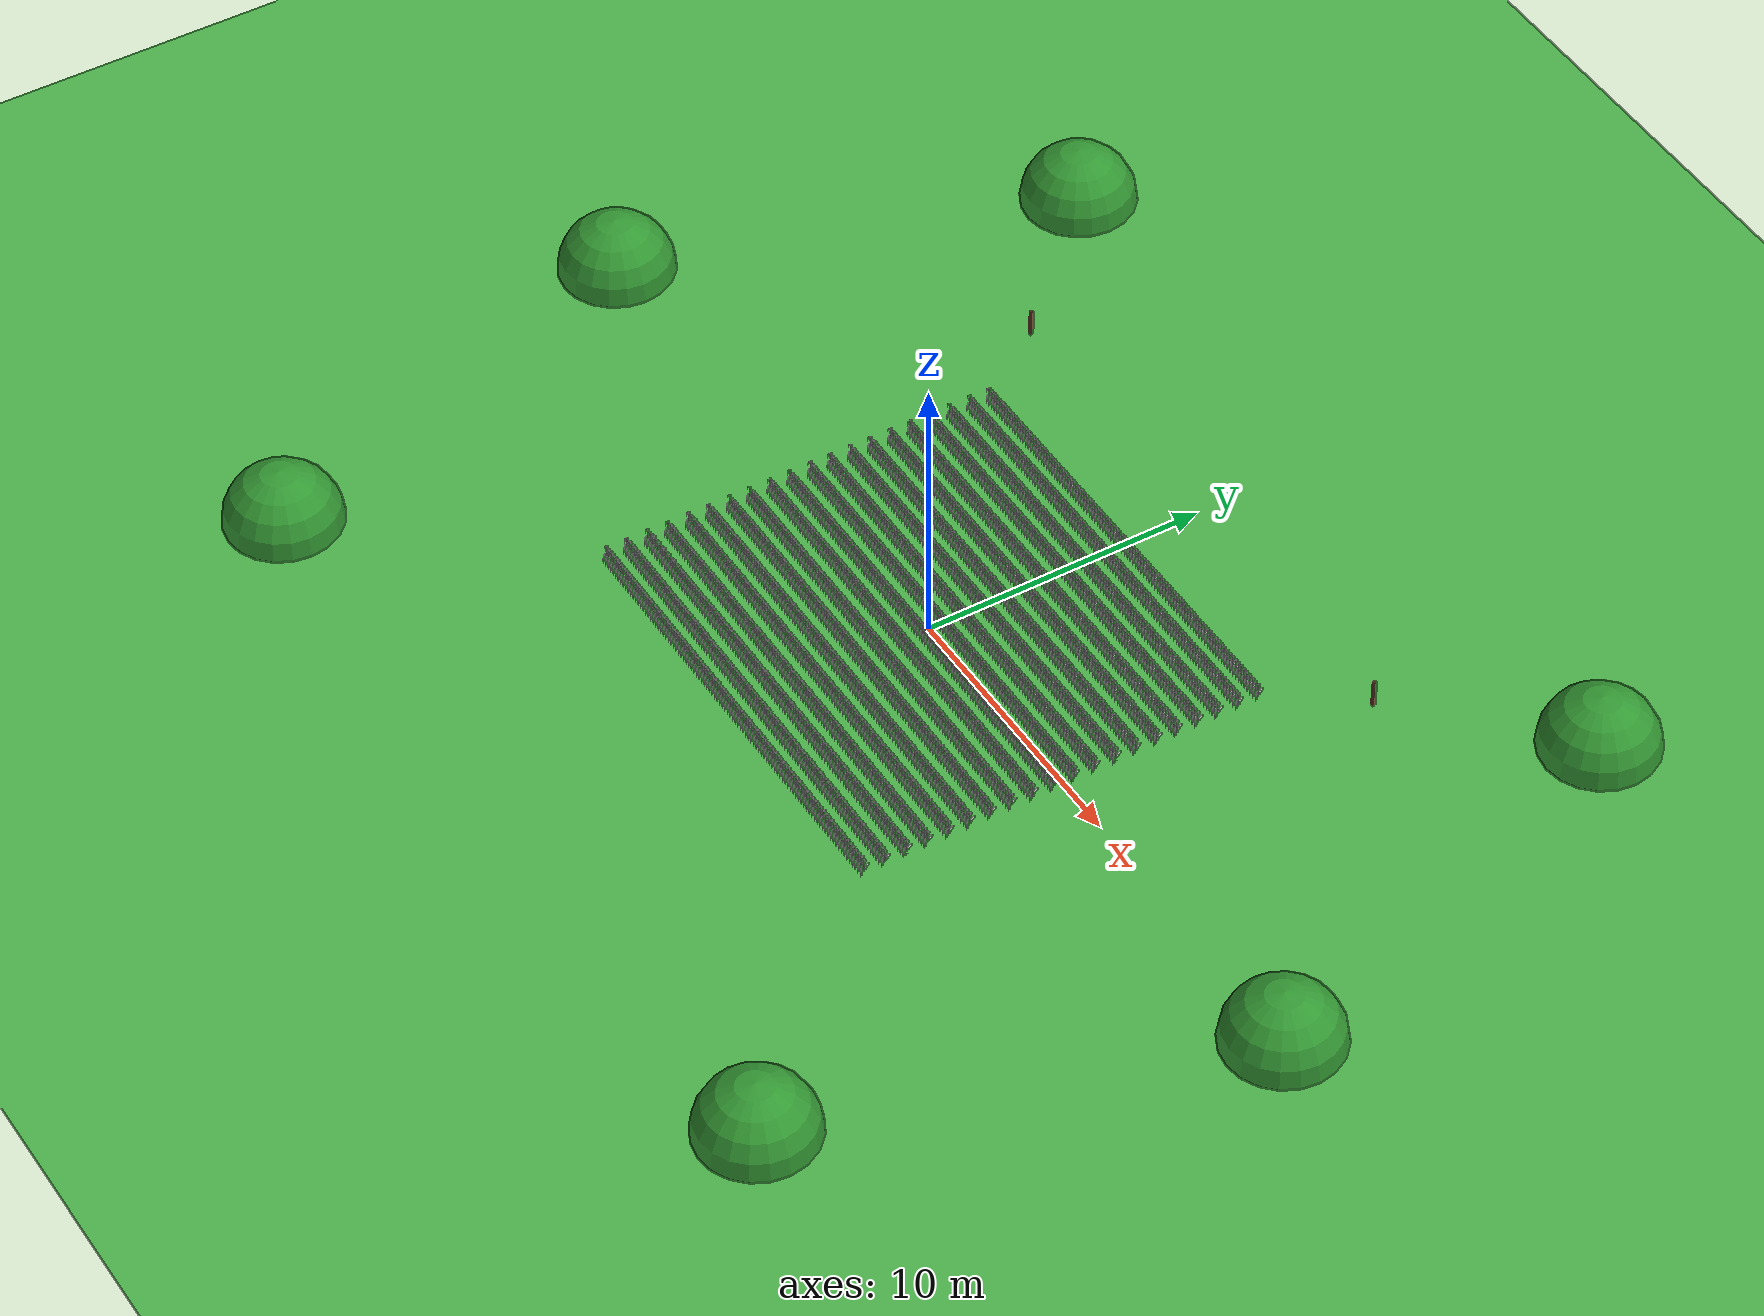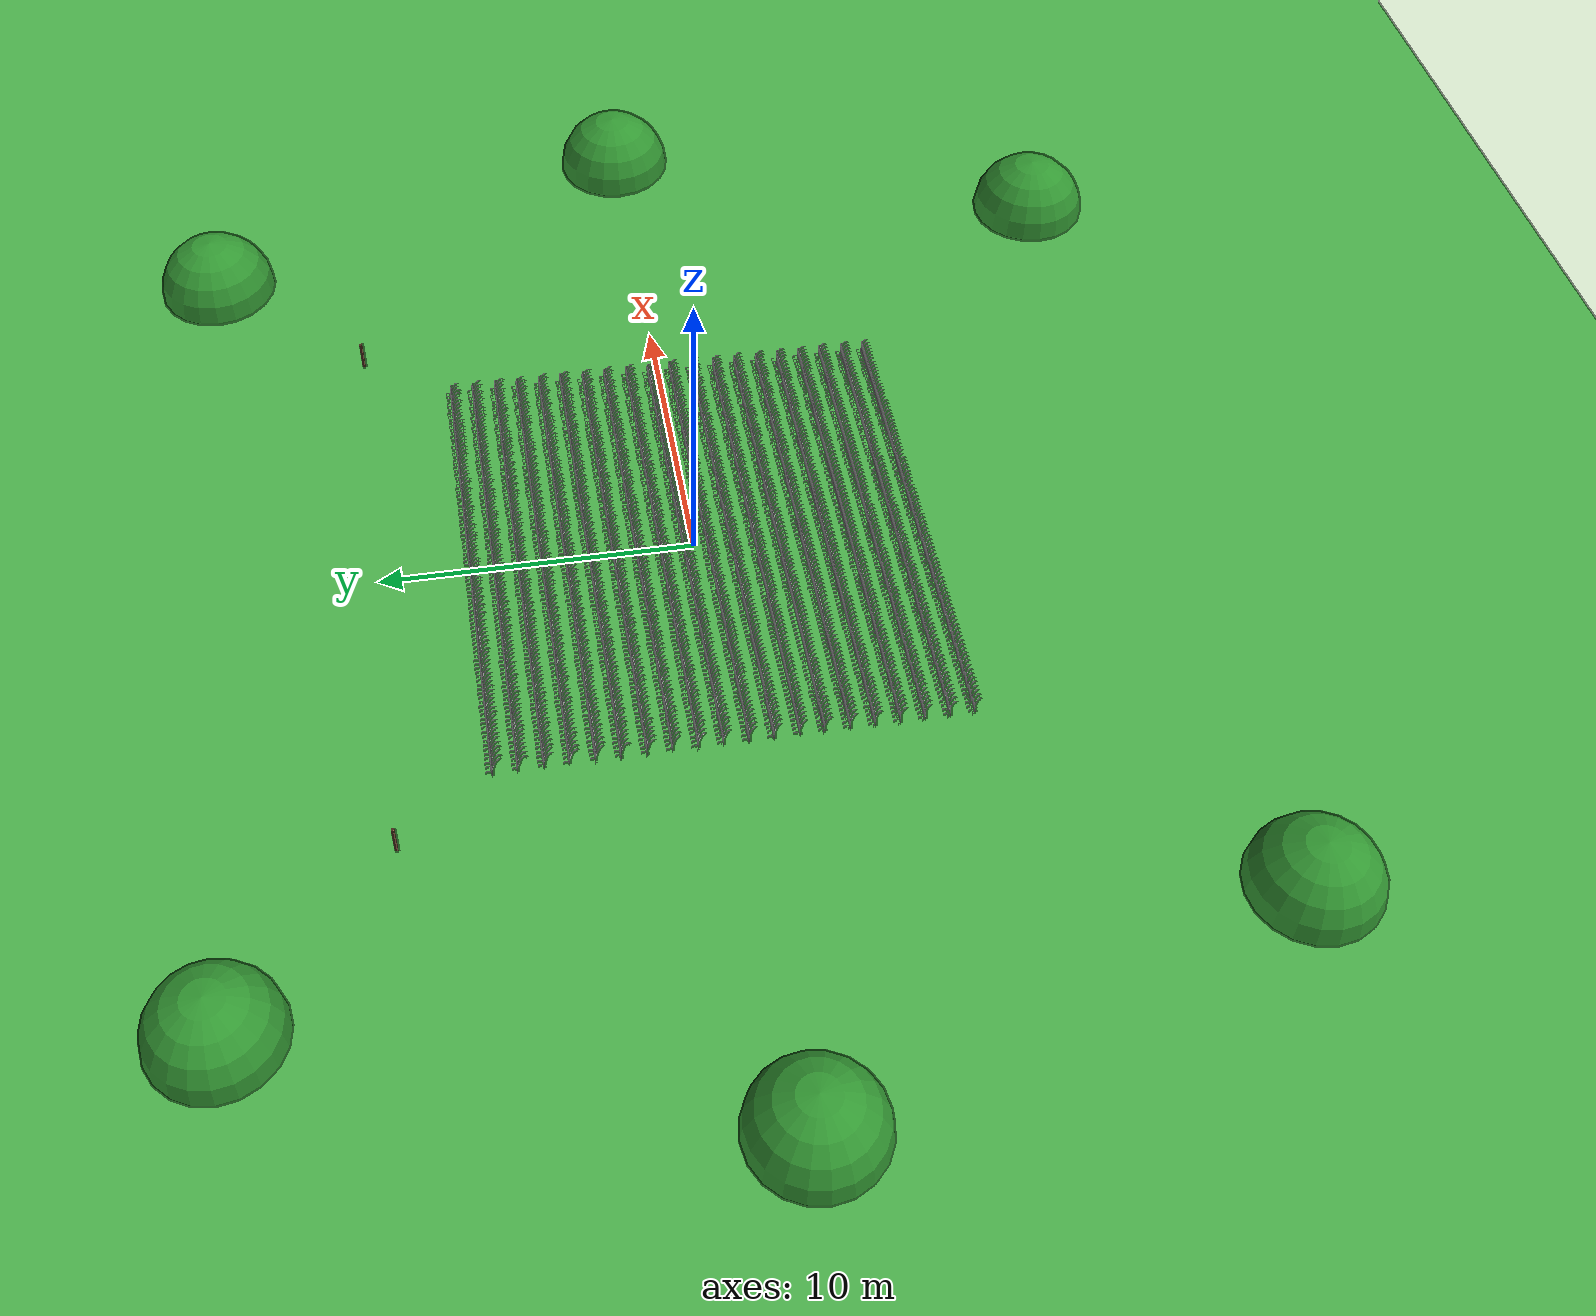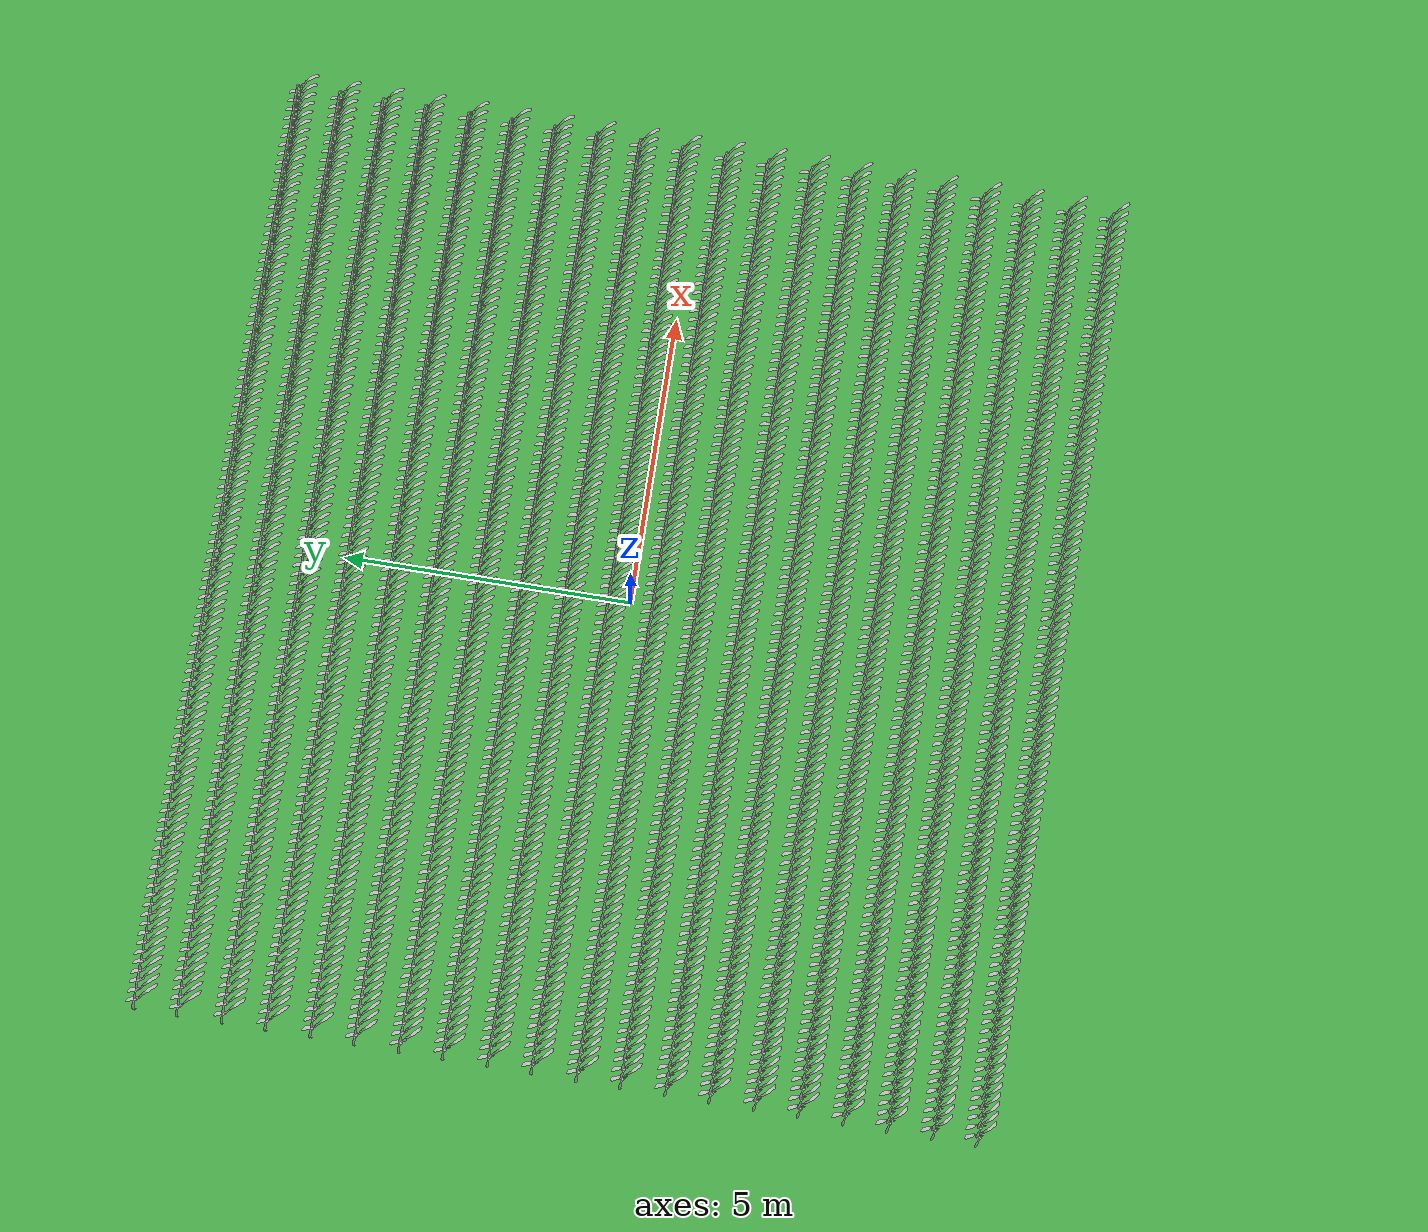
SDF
<?xml version="1.0" ?>
<sdf version="1.9">
  <world name="farm_world">
    <!-- Lights, ground, physics, scene from template -->
    <light type="directional" name="sun">
      <cast_shadows>true</cast_shadows>
      <pose>0 0 10 0 0 0</pose>
      <diffuse>1.0 1.0 0.95 1</diffuse>
      <specular>0.4 0.4 0.4 1</specular>
      <attenuation><range>1000</range><constant>0.9</constant><linear>0.01</linear><quadratic>0.001</quadratic></attenuation>
      <direction>-0.5 0.1 -0.9</direction>
    </light>
    <light type="directional" name="ambient">
      <cast_shadows>false</cast_shadows>
      <pose>0 0 5 0 0 0</pose>
      <diffuse>0.5 0.5 0.5 1</diffuse>
      <specular>0.1 0.1 0.1 1</specular>
      <direction>0 0 -1</direction>
    </light>
    <model name="ground_plane">
      <static>true</static>
      <link name="link">
        <collision name="collision"><geometry><plane><normal>0 0 1</normal><size>100 100</size></plane></geometry></collision>
        <visual name="visual"><geometry><plane><normal>0 0 1</normal><size>100 100</size></plane></geometry>
          <material><ambient>0.2 0.6 0.2 1</ambient><diffuse>0.3 0.7 0.3 1</diffuse><specular>0.1 0.1 0.1 1</specular></material>
        </visual>
      </link>
    </model>
    <gravity>0 0 -9.8066</gravity>
    <physics name="default_physics" default="0" type="ode">
      <ode><solver><type>quick</type><iters>10</iters><sor>1.3</sor></solver>
        <constraints><cfm>0.00001</cfm><erp>0.2</erp><contact_max_correcting_vel>100</contact_max_correcting_vel><contact_surface_layer>0.001</contact_surface_layer></constraints>
      </ode>
      <max_step_size>0.004</max_step_size>
      <real_time_factor>1</real_time_factor>
      <real_time_update_rate>250</real_time_update_rate>
    </physics>
    <scene><ambient>0.8 0.8 0.8 1</ambient><background>0.7 0.9 1.0 1</background><shadows>true</shadows></scene>

    <!-- Fence posts -->
    <model name="fence_post_1"><pose>10 10 0.5 0 0 0</pose><static>true</static>
      <link name="link"><collision name="collision"><geometry><box><size>0.1 0.1 1.0</size></box></geometry></collision>
        <visual name="visual"><geometry><box><size>0.1 0.1 1.0</size></box></geometry><material><ambient>0.4 0.3 0.2 1</ambient><diffuse>0.6 0.4 0.3 1</diffuse></material></visual></link>
    </model>
    <model name="fence_post_2"><pose>-10 10 0.5 0 0 0</pose><static>true</static>
      <link name="link"><collision name="collision"><geometry><box><size>0.1 0.1 1.0</size></box></geometry></collision>
        <visual name="visual"><geometry><box><size>0.1 0.1 1.0</size></box></geometry><material><ambient>0.4 0.3 0.2 1</ambient><diffuse>0.6 0.4 0.3 1</diffuse></material></visual></link>
    </model>

    <!-- 20x100 maize_01 plants (10 original + 5 rows each side) -->
    <include><uri>model://maize_01</uri><name>maize_0</name><pose>-7.92 -7.12 0 0 0 0</pose></include>
    <include><uri>model://maize_01</uri><name>maize_1</name><pose>-7.76 -7.12 0 0 0 0</pose></include>
    <include><uri>model://maize_01</uri><name>maize_2</name><pose>-7.60 -7.12 0 0 0 0</pose></include>
    <include><uri>model://maize_01</uri><name>maize_3</name><pose>-7.44 -7.12 0 0 0 0</pose></include>
    <include><uri>model://maize_01</uri><name>maize_4</name><pose>-7.28 -7.12 0 0 0 0</pose></include>
    <include><uri>model://maize_01</uri><name>maize_5</name><pose>-7.12 -7.12 0 0 0 0</pose></include>
    <include><uri>model://maize_01</uri><name>maize_6</name><pose>-6.96 -7.12 0 0 0 0</pose></include>
    <include><uri>model://maize_01</uri><name>maize_7</name><pose>-6.80 -7.12 0 0 0 0</pose></include>
    <include><uri>model://maize_01</uri><name>maize_8</name><pose>-6.64 -7.12 0 0 0 0</pose></include>
    <include><uri>model://maize_01</uri><name>maize_9</name><pose>-6.48 -7.12 0 0 0 0</pose></include>
    <include><uri>model://maize_01</uri><name>maize_10</name><pose>-6.32 -7.12 0 0 0 0</pose></include>
    <include><uri>model://maize_01</uri><name>maize_11</name><pose>-6.16 -7.12 0 0 0 0</pose></include>
    <include><uri>model://maize_01</uri><name>maize_12</name><pose>-6.00 -7.12 0 0 0 0</pose></include>
    <include><uri>model://maize_01</uri><name>maize_13</name><pose>-5.84 -7.12 0 0 0 0</pose></include>
    <include><uri>model://maize_01</uri><name>maize_14</name><pose>-5.68 -7.12 0 0 0 0</pose></include>
    <include><uri>model://maize_01</uri><name>maize_15</name><pose>-5.52 -7.12 0 0 0 0</pose></include>
    <include><uri>model://maize_01</uri><name>maize_16</name><pose>-5.36 -7.12 0 0 0 0</pose></include>
    <include><uri>model://maize_01</uri><name>maize_17</name><pose>-5.20 -7.12 0 0 0 0</pose></include>
    <include><uri>model://maize_01</uri><name>maize_18</name><pose>-5.04 -7.12 0 0 0 0</pose></include>
    <include><uri>model://maize_01</uri><name>maize_19</name><pose>-4.88 -7.12 0 0 0 0</pose></include>
    <include><uri>model://maize_01</uri><name>maize_20</name><pose>-4.72 -7.12 0 0 0 0</pose></include>
    <include><uri>model://maize_01</uri><name>maize_21</name><pose>-4.56 -7.12 0 0 0 0</pose></include>
    <include><uri>model://maize_01</uri><name>maize_22</name><pose>-4.40 -7.12 0 0 0 0</pose></include>
    <include><uri>model://maize_01</uri><name>maize_23</name><pose>-4.24 -7.12 0 0 0 0</pose></include>
    <include><uri>model://maize_01</uri><name>maize_24</name><pose>-4.08 -7.12 0 0 0 0</pose></include>
    <include><uri>model://maize_01</uri><name>maize_25</name><pose>-3.92 -7.12 0 0 0 0</pose></include>
    <include><uri>model://maize_01</uri><name>maize_26</name><pose>-3.76 -7.12 0 0 0 0</pose></include>
    <include><uri>model://maize_01</uri><name>maize_27</name><pose>-3.60 -7.12 0 0 0 0</pose></include>
    <include><uri>model://maize_01</uri><name>maize_28</name><pose>-3.44 -7.12 0 0 0 0</pose></include>
    <include><uri>model://maize_01</uri><name>maize_29</name><pose>-3.28 -7.12 0 0 0 0</pose></include>
    <include><uri>model://maize_01</uri><name>maize_30</name><pose>-3.12 -7.12 0 0 0 0</pose></include>
    <include><uri>model://maize_01</uri><name>maize_31</name><pose>-2.96 -7.12 0 0 0 0</pose></include>
    <include><uri>model://maize_01</uri><name>maize_32</name><pose>-2.80 -7.12 0 0 0 0</pose></include>
    <include><uri>model://maize_01</uri><name>maize_33</name><pose>-2.64 -7.12 0 0 0 0</pose></include>
    <include><uri>model://maize_01</uri><name>maize_34</name><pose>-2.48 -7.12 0 0 0 0</pose></include>
    <include><uri>model://maize_01</uri><name>maize_35</name><pose>-2.32 -7.12 0 0 0 0</pose></include>
    <include><uri>model://maize_01</uri><name>maize_36</name><pose>-2.16 -7.12 0 0 0 0</pose></include>
    <include><uri>model://maize_01</uri><name>maize_37</name><pose>-2.00 -7.12 0 0 0 0</pose></include>
    <include><uri>model://maize_01</uri><name>maize_38</name><pose>-1.84 -7.12 0 0 0 0</pose></include>
    <include><uri>model://maize_01</uri><name>maize_39</name><pose>-1.68 -7.12 0 0 0 0</pose></include>
    <include><uri>model://maize_01</uri><name>maize_40</name><pose>-1.52 -7.12 0 0 0 0</pose></include>
    <include><uri>model://maize_01</uri><name>maize_41</name><pose>-1.36 -7.12 0 0 0 0</pose></include>
    <include><uri>model://maize_01</uri><name>maize_42</name><pose>-1.20 -7.12 0 0 0 0</pose></include>
    <include><uri>model://maize_01</uri><name>maize_43</name><pose>-1.04 -7.12 0 0 0 0</pose></include>
    <include><uri>model://maize_01</uri><name>maize_44</name><pose>-0.88 -7.12 0 0 0 0</pose></include>
    <include><uri>model://maize_01</uri><name>maize_45</name><pose>-0.72 -7.12 0 0 0 0</pose></include>
    <include><uri>model://maize_01</uri><name>maize_46</name><pose>-0.56 -7.12 0 0 0 0</pose></include>
    <include><uri>model://maize_01</uri><name>maize_47</name><pose>-0.40 -7.12 0 0 0 0</pose></include>
    <include><uri>model://maize_01</uri><name>maize_48</name><pose>-0.24 -7.12 0 0 0 0</pose></include>
    <include><uri>model://maize_01</uri><name>maize_49</name><pose>-0.08 -7.12 0 0 0 0</pose></include>
    <include><uri>model://maize_01</uri><name>maize_50</name><pose>0.08 -7.12 0 0 0 0</pose></include>
    <include><uri>model://maize_01</uri><name>maize_51</name><pose>0.24 -7.12 0 0 0 0</pose></include>
    <include><uri>model://maize_01</uri><name>maize_52</name><pose>0.40 -7.12 0 0 0 0</pose></include>
    <include><uri>model://maize_01</uri><name>maize_53</name><pose>0.56 -7.12 0 0 0 0</pose></include>
    <include><uri>model://maize_01</uri><name>maize_54</name><pose>0.72 -7.12 0 0 0 0</pose></include>
    <include><uri>model://maize_01</uri><name>maize_55</name><pose>0.88 -7.12 0 0 0 0</pose></include>
    <include><uri>model://maize_01</uri><name>maize_56</name><pose>1.04 -7.12 0 0 0 0</pose></include>
    <include><uri>model://maize_01</uri><name>maize_57</name><pose>1.20 -7.12 0 0 0 0</pose></include>
    <include><uri>model://maize_01</uri><name>maize_58</name><pose>1.36 -7.12 0 0 0 0</pose></include>
    <include><uri>model://maize_01</uri><name>maize_59</name><pose>1.52 -7.12 0 0 0 0</pose></include>
    <include><uri>model://maize_01</uri><name>maize_60</name><pose>1.68 -7.12 0 0 0 0</pose></include>
    <include><uri>model://maize_01</uri><name>maize_61</name><pose>1.84 -7.12 0 0 0 0</pose></include>
    <include><uri>model://maize_01</uri><name>maize_62</name><pose>2.00 -7.12 0 0 0 0</pose></include>
    <include><uri>model://maize_01</uri><name>maize_63</name><pose>2.16 -7.12 0 0 0 0</pose></include>
    <include><uri>model://maize_01</uri><name>maize_64</name><pose>2.32 -7.12 0 0 0 0</pose></include>
    <include><uri>model://maize_01</uri><name>maize_65</name><pose>2.48 -7.12 0 0 0 0</pose></include>
    <include><uri>model://maize_01</uri><name>maize_66</name><pose>2.64 -7.12 0 0 0 0</pose></include>
    <include><uri>model://maize_01</uri><name>maize_67</name><pose>2.80 -7.12 0 0 0 0</pose></include>
    <include><uri>model://maize_01</uri><name>maize_68</name><pose>2.96 -7.12 0 0 0 0</pose></include>
    <include><uri>model://maize_01</uri><name>maize_69</name><pose>3.12 -7.12 0 0 0 0</pose></include>
    <include><uri>model://maize_01</uri><name>maize_70</name><pose>3.28 -7.12 0 0 0 0</pose></include>
    <include><uri>model://maize_01</uri><name>maize_71</name><pose>3.44 -7.12 0 0 0 0</pose></include>
    <include><uri>model://maize_01</uri><name>maize_72</name><pose>3.60 -7.12 0 0 0 0</pose></include>
    <include><uri>model://maize_01</uri><name>maize_73</name><pose>3.76 -7.12 0 0 0 0</pose></include>
    <include><uri>model://maize_01</uri><name>maize_74</name><pose>3.92 -7.12 0 0 0 0</pose></include>
    <include><uri>model://maize_01</uri><name>maize_75</name><pose>4.08 -7.12 0 0 0 0</pose></include>
    <include><uri>model://maize_01</uri><name>maize_76</name><pose>4.24 -7.12 0 0 0 0</pose></include>
    <include><uri>model://maize_01</uri><name>maize_77</name><pose>4.40 -7.12 0 0 0 0</pose></include>
    <include><uri>model://maize_01</uri><name>maize_78</name><pose>4.56 -7.12 0 0 0 0</pose></include>
    <include><uri>model://maize_01</uri><name>maize_79</name><pose>4.72 -7.12 0 0 0 0</pose></include>
    <include><uri>model://maize_01</uri><name>maize_80</name><pose>4.88 -7.12 0 0 0 0</pose></include>
    <include><uri>model://maize_01</uri><name>maize_81</name><pose>5.04 -7.12 0 0 0 0</pose></include>
    <include><uri>model://maize_01</uri><name>maize_82</name><pose>5.20 -7.12 0 0 0 0</pose></include>
    <include><uri>model://maize_01</uri><name>maize_83</name><pose>5.36 -7.12 0 0 0 0</pose></include>
    <include><uri>model://maize_01</uri><name>maize_84</name><pose>5.52 -7.12 0 0 0 0</pose></include>
    <include><uri>model://maize_01</uri><name>maize_85</name><pose>5.68 -7.12 0 0 0 0</pose></include>
    <include><uri>model://maize_01</uri><name>maize_86</name><pose>5.84 -7.12 0 0 0 0</pose></include>
    <include><uri>model://maize_01</uri><name>maize_87</name><pose>6.00 -7.12 0 0 0 0</pose></include>
    <include><uri>model://maize_01</uri><name>maize_88</name><pose>6.16 -7.12 0 0 0 0</pose></include>
    <include><uri>model://maize_01</uri><name>maize_89</name><pose>6.32 -7.12 0 0 0 0</pose></include>
    <include><uri>model://maize_01</uri><name>maize_90</name><pose>6.48 -7.12 0 0 0 0</pose></include>
    <include><uri>model://maize_01</uri><name>maize_91</name><pose>6.64 -7.12 0 0 0 0</pose></include>
    <include><uri>model://maize_01</uri><name>maize_92</name><pose>6.80 -7.12 0 0 0 0</pose></include>
    <include><uri>model://maize_01</uri><name>maize_93</name><pose>6.96 -7.12 0 0 0 0</pose></include>
    <include><uri>model://maize_01</uri><name>maize_94</name><pose>7.12 -7.12 0 0 0 0</pose></include>
    <include><uri>model://maize_01</uri><name>maize_95</name><pose>7.28 -7.12 0 0 0 0</pose></include>
    <include><uri>model://maize_01</uri><name>maize_96</name><pose>7.44 -7.12 0 0 0 0</pose></include>
    <include><uri>model://maize_01</uri><name>maize_97</name><pose>7.60 -7.12 0 0 0 0</pose></include>
    <include><uri>model://maize_01</uri><name>maize_98</name><pose>7.76 -7.12 0 0 0 0</pose></include>
    <include><uri>model://maize_01</uri><name>maize_99</name><pose>7.92 -7.12 0 0 0 0</pose></include>
    <include><uri>model://maize_01</uri><name>maize_100</name><pose>-7.92 -6.38 0 0 0 0</pose></include>
    <include><uri>model://maize_01</uri><name>maize_101</name><pose>-7.76 -6.38 0 0 0 0</pose></include>
    <include><uri>model://maize_01</uri><name>maize_102</name><pose>-7.60 -6.38 0 0 0 0</pose></include>
    <include><uri>model://maize_01</uri><name>maize_103</name><pose>-7.44 -6.38 0 0 0 0</pose></include>
    <include><uri>model://maize_01</uri><name>maize_104</name><pose>-7.28 -6.38 0 0 0 0</pose></include>
    <include><uri>model://maize_01</uri><name>maize_105</name><pose>-7.12 -6.38 0 0 0 0</pose></include>
    <include><uri>model://maize_01</uri><name>maize_106</name><pose>-6.96 -6.38 0 0 0 0</pose></include>
    <include><uri>model://maize_01</uri><name>maize_107</name><pose>-6.80 -6.38 0 0 0 0</pose></include>
    <include><uri>model://maize_01</uri><name>maize_108</name><pose>-6.64 -6.38 0 0 0 0</pose></include>
    <include><uri>model://maize_01</uri><name>maize_109</name><pose>-6.48 -6.38 0 0 0 0</pose></include>
    <include><uri>model://maize_01</uri><name>maize_110</name><pose>-6.32 -6.38 0 0 0 0</pose></include>
    <include><uri>model://maize_01</uri><name>maize_111</name><pose>-6.16 -6.38 0 0 0 0</pose></include>
    <include><uri>model://maize_01</uri><name>maize_112</name><pose>-6.00 -6.38 0 0 0 0</pose></include>
    <include><uri>model://maize_01</uri><name>maize_113</name><pose>-5.84 -6.38 0 0 0 0</pose></include>
    <include><uri>model://maize_01</uri><name>maize_114</name><pose>-5.68 -6.38 0 0 0 0</pose></include>
    <include><uri>model://maize_01</uri><name>maize_115</name><pose>-5.52 -6.38 0 0 0 0</pose></include>
    <include><uri>model://maize_01</uri><name>maize_116</name><pose>-5.36 -6.38 0 0 0 0</pose></include>
    <include><uri>model://maize_01</uri><name>maize_117</name><pose>-5.20 -6.38 0 0 0 0</pose></include>
    <include><uri>model://maize_01</uri><name>maize_118</name><pose>-5.04 -6.38 0 0 0 0</pose></include>
    <include><uri>model://maize_01</uri><name>maize_119</name><pose>-4.88 -6.38 0 0 0 0</pose></include>
    <include><uri>model://maize_01</uri><name>maize_120</name><pose>-4.72 -6.38 0 0 0 0</pose></include>
    <include><uri>model://maize_01</uri><name>maize_121</name><pose>-4.56 -6.38 0 0 0 0</pose></include>
    <include><uri>model://maize_01</uri><name>maize_122</name><pose>-4.40 -6.38 0 0 0 0</pose></include>
    <include><uri>model://maize_01</uri><name>maize_123</name><pose>-4.24 -6.38 0 0 0 0</pose></include>
    <include><uri>model://maize_01</uri><name>maize_124</name><pose>-4.08 -6.38 0 0 0 0</pose></include>
    <include><uri>model://maize_01</uri><name>maize_125</name><pose>-3.92 -6.38 0 0 0 0</pose></include>
    <include><uri>model://maize_01</uri><name>maize_126</name><pose>-3.76 -6.38 0 0 0 0</pose></include>
    <include><uri>model://maize_01</uri><name>maize_127</name><pose>-3.60 -6.38 0 0 0 0</pose></include>
    <include><uri>model://maize_01</uri><name>maize_128</name><pose>-3.44 -6.38 0 0 0 0</pose></include>
    <include><uri>model://maize_01</uri><name>maize_129</name><pose>-3.28 -6.38 0 0 0 0</pose></include>
    <include><uri>model://maize_01</uri><name>maize_130</name><pose>-3.12 -6.38 0 0 0 0</pose></include>
    <include><uri>model://maize_01</uri><name>maize_131</name><pose>-2.96 -6.38 0 0 0 0</pose></include>
    <include><uri>model://maize_01</uri><name>maize_132</name><pose>-2.80 -6.38 0 0 0 0</pose></include>
    <include><uri>model://maize_01</uri><name>maize_133</name><pose>-2.64 -6.38 0 0 0 0</pose></include>
    <include><uri>model://maize_01</uri><name>maize_134</name><pose>-2.48 -6.38 0 0 0 0</pose></include>
    <include><uri>model://maize_01</uri><name>maize_135</name><pose>-2.32 -6.38 0 0 0 0</pose></include>
    <include><uri>model://maize_01</uri><name>maize_136</name><pose>-2.16 -6.38 0 0 0 0</pose></include>
    <include><uri>model://maize_01</uri><name>maize_137</name><pose>-2.00 -6.38 0 0 0 0</pose></include>
    <include><uri>model://maize_01</uri><name>maize_138</name><pose>-1.84 -6.38 0 0 0 0</pose></include>
    <include><uri>model://maize_01</uri><name>maize_139</name><pose>-1.68 -6.38 0 0 0 0</pose></include>
    <include><uri>model://maize_01</uri><name>maize_140</name><pose>-1.52 -6.38 0 0 0 0</pose></include>
    <include><uri>model://maize_01</uri><name>maize_141</name><pose>-1.36 -6.38 0 0 0 0</pose></include>
    <include><uri>model://maize_01</uri><name>maize_142</name><pose>-1.20 -6.38 0 0 0 0</pose></include>
    <include><uri>model://maize_01</uri><name>maize_143</name><pose>-1.04 -6.38 0 0 0 0</pose></include>
    <include><uri>model://maize_01</uri><name>maize_144</name><pose>-0.88 -6.38 0 0 0 0</pose></include>
    <include><uri>model://maize_01</uri><name>maize_145</name><pose>-0.72 -6.38 0 0 0 0</pose></include>
    <include><uri>model://maize_01</uri><name>maize_146</name><pose>-0.56 -6.38 0 0 0 0</pose></include>
    <include><uri>model://maize_01</uri><name>maize_147</name><pose>-0.40 -6.38 0 0 0 0</pose></include>
    <include><uri>model://maize_01</uri><name>maize_148</name><pose>-0.24 -6.38 0 0 0 0</pose></include>
    <include><uri>model://maize_01</uri><name>maize_149</name><pose>-0.08 -6.38 0 0 0 0</pose></include>
    <include><uri>model://maize_01</uri><name>maize_150</name><pose>0.08 -6.38 0 0 0 0</pose></include>
    <include><uri>model://maize_01</uri><name>maize_151</name><pose>0.24 -6.38 0 0 0 0</pose></include>
    <include><uri>model://maize_01</uri><name>maize_152</name><pose>0.40 -6.38 0 0 0 0</pose></include>
    <include><uri>model://maize_01</uri><name>maize_153</name><pose>0.56 -6.38 0 0 0 0</pose></include>
    <include><uri>model://maize_01</uri><name>maize_154</name><pose>0.72 -6.38 0 0 0 0</pose></include>
    <include><uri>model://maize_01</uri><name>maize_155</name><pose>0.88 -6.38 0 0 0 0</pose></include>
    <include><uri>model://maize_01</uri><name>maize_156</name><pose>1.04 -6.38 0 0 0 0</pose></include>
    <include><uri>model://maize_01</uri><name>maize_157</name><pose>1.20 -6.38 0 0 0 0</pose></include>
    <include><uri>model://maize_01</uri><name>maize_158</name><pose>1.36 -6.38 0 0 0 0</pose></include>
    <include><uri>model://maize_01</uri><name>maize_159</name><pose>1.52 -6.38 0 0 0 0</pose></include>
    <include><uri>model://maize_01</uri><name>maize_160</name><pose>1.68 -6.38 0 0 0 0</pose></include>
    <include><uri>model://maize_01</uri><name>maize_161</name><pose>1.84 -6.38 0 0 0 0</pose></include>
    <include><uri>model://maize_01</uri><name>maize_162</name><pose>2.00 -6.38 0 0 0 0</pose></include>
    <include><uri>model://maize_01</uri><name>maize_163</name><pose>2.16 -6.38 0 0 0 0</pose></include>
    <include><uri>model://maize_01</uri><name>maize_164</name><pose>2.32 -6.38 0 0 0 0</pose></include>
    <include><uri>model://maize_01</uri><name>maize_165</name><pose>2.48 -6.38 0 0 0 0</pose></include>
    <include><uri>model://maize_01</uri><name>maize_166</name><pose>2.64 -6.38 0 0 0 0</pose></include>
    <include><uri>model://maize_01</uri><name>maize_167</name><pose>2.80 -6.38 0 0 0 0</pose></include>
    <include><uri>model://maize_01</uri><name>maize_168</name><pose>2.96 -6.38 0 0 0 0</pose></include>
    <include><uri>model://maize_01</uri><name>maize_169</name><pose>3.12 -6.38 0 0 0 0</pose></include>
    <include><uri>model://maize_01</uri><name>maize_170</name><pose>3.28 -6.38 0 0 0 0</pose></include>
    <include><uri>model://maize_01</uri><name>maize_171</name><pose>3.44 -6.38 0 0 0 0</pose></include>
    <include><uri>model://maize_01</uri><name>maize_172</name><pose>3.60 -6.38 0 0 0 0</pose></include>
    <include><uri>model://maize_01</uri><name>maize_173</name><pose>3.76 -6.38 0 0 0 0</pose></include>
    <include><uri>model://maize_01</uri><name>maize_174</name><pose>3.92 -6.38 0 0 0 0</pose></include>
    <include><uri>model://maize_01</uri><name>maize_175</name><pose>4.08 -6.38 0 0 0 0</pose></include>
    <include><uri>model://maize_01</uri><name>maize_176</name><pose>4.24 -6.38 0 0 0 0</pose></include>
    <include><uri>model://maize_01</uri><name>maize_177</name><pose>4.40 -6.38 0 0 0 0</pose></include>
    <include><uri>model://maize_01</uri><name>maize_178</name><pose>4.56 -6.38 0 0 0 0</pose></include>
    <include><uri>model://maize_01</uri><name>maize_179</name><pose>4.72 -6.38 0 0 0 0</pose></include>
    <include><uri>model://maize_01</uri><name>maize_180</name><pose>4.88 -6.38 0 0 0 0</pose></include>
    <include><uri>model://maize_01</uri><name>maize_181</name><pose>5.04 -6.38 0 0 0 0</pose></include>
    <include><uri>model://maize_01</uri><name>maize_182</name><pose>5.20 -6.38 0 0 0 0</pose></include>
    <include><uri>model://maize_01</uri><name>maize_183</name><pose>5.36 -6.38 0 0 0 0</pose></include>
    <include><uri>model://maize_01</uri><name>maize_184</name><pose>5.52 -6.38 0 0 0 0</pose></include>
    <include><uri>model://maize_01</uri><name>maize_185</name><pose>5.68 -6.38 0 0 0 0</pose></include>
    <include><uri>model://maize_01</uri><name>maize_186</name><pose>5.84 -6.38 0 0 0 0</pose></include>
    <include><uri>model://maize_01</uri><name>maize_187</name><pose>6.00 -6.38 0 0 0 0</pose></include>
    <include><uri>model://maize_01</uri><name>maize_188</name><pose>6.16 -6.38 0 0 0 0</pose></include>
    <include><uri>model://maize_01</uri><name>maize_189</name><pose>6.32 -6.38 0 0 0 0</pose></include>
    <include><uri>model://maize_01</uri><name>maize_190</name><pose>6.48 -6.38 0 0 0 0</pose></include>
    <include><uri>model://maize_01</uri><name>maize_191</name><pose>6.64 -6.38 0 0 0 0</pose></include>
    <include><uri>model://maize_01</uri><name>maize_192</name><pose>6.80 -6.38 0 0 0 0</pose></include>
    <include><uri>model://maize_01</uri><name>maize_193</name><pose>6.96 -6.38 0 0 0 0</pose></include>
    <include><uri>model://maize_01</uri><name>maize_194</name><pose>7.12 -6.38 0 0 0 0</pose></include>
    <include><uri>model://maize_01</uri><name>maize_195</name><pose>7.28 -6.38 0 0 0 0</pose></include>
    <include><uri>model://maize_01</uri><name>maize_196</name><pose>7.44 -6.38 0 0 0 0</pose></include>
    <include><uri>model://maize_01</uri><name>maize_197</name><pose>7.60 -6.38 0 0 0 0</pose></include>
    <include><uri>model://maize_01</uri><name>maize_198</name><pose>7.76 -6.38 0 0 0 0</pose></include>
    <include><uri>model://maize_01</uri><name>maize_199</name><pose>7.92 -6.38 0 0 0 0</pose></include>
    <include><uri>model://maize_01</uri><name>maize_200</name><pose>-7.92 -5.62 0 0 0 0</pose></include>
    <include><uri>model://maize_01</uri><name>maize_201</name><pose>-7.76 -5.62 0 0 0 0</pose></include>
    <include><uri>model://maize_01</uri><name>maize_202</name><pose>-7.60 -5.62 0 0 0 0</pose></include>
    <include><uri>model://maize_01</uri><name>maize_203</name><pose>-7.44 -5.62 0 0 0 0</pose></include>
    <include><uri>model://maize_01</uri><name>maize_204</name><pose>-7.28 -5.62 0 0 0 0</pose></include>
    <include><uri>model://maize_01</uri><name>maize_205</name><pose>-7.12 -5.62 0 0 0 0</pose></include>
    <include><uri>model://maize_01</uri><name>maize_206</name><pose>-6.96 -5.62 0 0 0 0</pose></include>
    <include><uri>model://maize_01</uri><name>maize_207</name><pose>-6.80 -5.62 0 0 0 0</pose></include>
    <include><uri>model://maize_01</uri><name>maize_208</name><pose>-6.64 -5.62 0 0 0 0</pose></include>
    <include><uri>model://maize_01</uri><name>maize_209</name><pose>-6.48 -5.62 0 0 0 0</pose></include>
    <include><uri>model://maize_01</uri><name>maize_210</name><pose>-6.32 -5.62 0 0 0 0</pose></include>
    <include><uri>model://maize_01</uri><name>maize_211</name><pose>-6.16 -5.62 0 0 0 0</pose></include>
    <include><uri>model://maize_01</uri><name>maize_212</name><pose>-6.00 -5.62 0 0 0 0</pose></include>
    <include><uri>model://maize_01</uri><name>maize_213</name><pose>-5.84 -5.62 0 0 0 0</pose></include>
    <include><uri>model://maize_01</uri><name>maize_214</name><pose>-5.68 -5.62 0 0 0 0</pose></include>
    <include><uri>model://maize_01</uri><name>maize_215</name><pose>-5.52 -5.62 0 0 0 0</pose></include>
    <include><uri>model://maize_01</uri><name>maize_216</name><pose>-5.36 -5.62 0 0 0 0</pose></include>
    <include><uri>model://maize_01</uri><name>maize_217</name><pose>-5.20 -5.62 0 0 0 0</pose></include>
    <include><uri>model://maize_01</uri><name>maize_218</name><pose>-5.04 -5.62 0 0 0 0</pose></include>
    <include><uri>model://maize_01</uri><name>maize_219</name><pose>-4.88 -5.62 0 0 0 0</pose></include>
    <include><uri>model://maize_01</uri><name>maize_220</name><pose>-4.72 -5.62 0 0 0 0</pose></include>
    <include><uri>model://maize_01</uri><name>maize_221</name><pose>-4.56 -5.62 0 0 0 0</pose></include>
    <include><uri>model://maize_01</uri><name>maize_222</name><pose>-4.40 -5.62 0 0 0 0</pose></include>
    <include><uri>model://maize_01</uri><name>maize_223</name><pose>-4.24 -5.62 0 0 0 0</pose></include>
    <include><uri>model://maize_01</uri><name>maize_224</name><pose>-4.08 -5.62 0 0 0 0</pose></include>
    <include><uri>model://maize_01</uri><name>maize_225</name><pose>-3.92 -5.62 0 0 0 0</pose></include>
    <include><uri>model://maize_01</uri><name>maize_226</name><pose>-3.76 -5.62 0 0 0 0</pose></include>
    <include><uri>model://maize_01</uri><name>maize_227</name><pose>-3.60 -5.62 0 0 0 0</pose></include>
    <include><uri>model://maize_01</uri><name>maize_228</name><pose>-3.44 -5.62 0 0 0 0</pose></include>
    <include><uri>model://maize_01</uri><name>maize_229</name><pose>-3.28 -5.62 0 0 0 0</pose></include>
    <include><uri>model://maize_01</uri><name>maize_230</name><pose>-3.12 -5.62 0 0 0 0</pose></include>
    <include><uri>model://maize_01</uri><name>maize_231</name><pose>-2.96 -5.62 0 0 0 0</pose></include>
    <include><uri>model://maize_01</uri><name>maize_232</name><pose>-2.80 -5.62 0 0 0 0</pose></include>
    <include><uri>model://maize_01</uri><name>maize_233</name><pose>-2.64 -5.62 0 0 0 0</pose></include>
    <include><uri>model://maize_01</uri><name>maize_234</name><pose>-2.48 -5.62 0 0 0 0</pose></include>
    <include><uri>model://maize_01</uri><name>maize_235</name><pose>-2.32 -5.62 0 0 0 0</pose></include>
    <include><uri>model://maize_01</uri><name>maize_236</name><pose>-2.16 -5.62 0 0 0 0</pose></include>
    <include><uri>model://maize_01</uri><name>maize_237</name><pose>-2.00 -5.62 0 0 0 0</pose></include>
    <include><uri>model://maize_01</uri><name>maize_238</name><pose>-1.84 -5.62 0 0 0 0</pose></include>
    <include><uri>model://maize_01</uri><name>maize_239</name><pose>-1.68 -5.62 0 0 0 0</pose></include>
    <include><uri>model://maize_01</uri><name>maize_240</name><pose>-1.52 -5.62 0 0 0 0</pose></include>
    <include><uri>model://maize_01</uri><name>maize_241</name><pose>-1.36 -5.62 0 0 0 0</pose></include>
    <include><uri>model://maize_01</uri><name>maize_242</name><pose>-1.20 -5.62 0 0 0 0</pose></include>
    <include><uri>model://maize_01</uri><name>maize_243</name><pose>-1.04 -5.62 0 0 0 0</pose></include>
    <include><uri>model://maize_01</uri><name>maize_244</name><pose>-0.88 -5.62 0 0 0 0</pose></include>
    <include><uri>model://maize_01</uri><name>maize_245</name><pose>-0.72 -5.62 0 0 0 0</pose></include>
    <include><uri>model://maize_01</uri><name>maize_246</name><pose>-0.56 -5.62 0 0 0 0</pose></include>
    <include><uri>model://maize_01</uri><name>maize_247</name><pose>-0.40 -5.62 0 0 0 0</pose></include>
    <include><uri>model://maize_01</uri><name>maize_248</name><pose>-0.24 -5.62 0 0 0 0</pose></include>
    <include><uri>model://maize_01</uri><name>maize_249</name><pose>-0.08 -5.62 0 0 0 0</pose></include>
    <include><uri>model://maize_01</uri><name>maize_250</name><pose>0.08 -5.62 0 0 0 0</pose></include>
    <include><uri>model://maize_01</uri><name>maize_251</name><pose>0.24 -5.62 0 0 0 0</pose></include>
    <include><uri>model://maize_01</uri><name>maize_252</name><pose>0.40 -5.62 0 0 0 0</pose></include>
    <include><uri>model://maize_01</uri><name>maize_253</name><pose>0.56 -5.62 0 0 0 0</pose></include>
    <include><uri>model://maize_01</uri><name>maize_254</name><pose>0.72 -5.62 0 0 0 0</pose></include>
    <include><uri>model://maize_01</uri><name>maize_255</name><pose>0.88 -5.62 0 0 0 0</pose></include>
    <include><uri>model://maize_01</uri><name>maize_256</name><pose>1.04 -5.62 0 0 0 0</pose></include>
    <include><uri>model://maize_01</uri><name>maize_257</name><pose>1.20 -5.62 0 0 0 0</pose></include>
    <include><uri>model://maize_01</uri><name>maize_258</name><pose>1.36 -5.62 0 0 0 0</pose></include>
    <include><uri>model://maize_01</uri><name>maize_259</name><pose>1.52 -5.62 0 0 0 0</pose></include>
    <include><uri>model://maize_01</uri><name>maize_260</name><pose>1.68 -5.62 0 0 0 0</pose></include>
    <include><uri>model://maize_01</uri><name>maize_261</name><pose>1.84 -5.62 0 0 0 0</pose></include>
    <include><uri>model://maize_01</uri><name>maize_262</name><pose>2.00 -5.62 0 0 0 0</pose></include>
    <include><uri>model://maize_01</uri><name>maize_263</name><pose>2.16 -5.62 0 0 0 0</pose></include>
    <include><uri>model://maize_01</uri><name>maize_264</name><pose>2.32 -5.62 0 0 0 0</pose></include>
    <include><uri>model://maize_01</uri><name>maize_265</name><pose>2.48 -5.62 0 0 0 0</pose></include>
    <include><uri>model://maize_01</uri><name>maize_266</name><pose>2.64 -5.62 0 0 0 0</pose></include>
    <include><uri>model://maize_01</uri><name>maize_267</name><pose>2.80 -5.62 0 0 0 0</pose></include>
    <include><uri>model://maize_01</uri><name>maize_268</name><pose>2.96 -5.62 0 0 0 0</pose></include>
    <include><uri>model://maize_01</uri><name>maize_269</name><pose>3.12 -5.62 0 0 0 0</pose></include>
    <include><uri>model://maize_01</uri><name>maize_270</name><pose>3.28 -5.62 0 0 0 0</pose></include>
    <include><uri>model://maize_01</uri><name>maize_271</name><pose>3.44 -5.62 0 0 0 0</pose></include>
    <include><uri>model://maize_01</uri><name>maize_272</name><pose>3.60 -5.62 0 0 0 0</pose></include>
    <include><uri>model://maize_01</uri><name>maize_273</name><pose>3.76 -5.62 0 0 0 0</pose></include>
    <include><uri>model://maize_01</uri><name>maize_274</name><pose>3.92 -5.62 0 0 0 0</pose></include>
    <include><uri>model://maize_01</uri><name>maize_275</name><pose>4.08 -5.62 0 0 0 0</pose></include>
    <include><uri>model://maize_01</uri><name>maize_276</name><pose>4.24 -5.62 0 0 0 0</pose></include>
    <include><uri>model://maize_01</uri><name>maize_277</name><pose>4.40 -5.62 0 0 0 0</pose></include>
    <include><uri>model://maize_01</uri><name>maize_278</name><pose>4.56 -5.62 0 0 0 0</pose></include>
    <include><uri>model://maize_01</uri><name>maize_279</name><pose>4.72 -5.62 0 0 0 0</pose></include>
    <include><uri>model://maize_01</uri><name>maize_280</name><pose>4.88 -5.62 0 0 0 0</pose></include>
    <include><uri>model://maize_01</uri><name>maize_281</name><pose>5.04 -5.62 0 0 0 0</pose></include>
    <include><uri>model://maize_01</uri><name>maize_282</name><pose>5.20 -5.62 0 0 0 0</pose></include>
    <include><uri>model://maize_01</uri><name>maize_283</name><pose>5.36 -5.62 0 0 0 0</pose></include>
    <include><uri>model://maize_01</uri><name>maize_284</name><pose>5.52 -5.62 0 0 0 0</pose></include>
    <include><uri>model://maize_01</uri><name>maize_285</name><pose>5.68 -5.62 0 0 0 0</pose></include>
    <include><uri>model://maize_01</uri><name>maize_286</name><pose>5.84 -5.62 0 0 0 0</pose></include>
    <include><uri>model://maize_01</uri><name>maize_287</name><pose>6.00 -5.62 0 0 0 0</pose></include>
    <include><uri>model://maize_01</uri><name>maize_288</name><pose>6.16 -5.62 0 0 0 0</pose></include>
    <include><uri>model://maize_01</uri><name>maize_289</name><pose>6.32 -5.62 0 0 0 0</pose></include>
    <include><uri>model://maize_01</uri><name>maize_290</name><pose>6.48 -5.62 0 0 0 0</pose></include>
    <include><uri>model://maize_01</uri><name>maize_291</name><pose>6.64 -5.62 0 0 0 0</pose></include>
    <include><uri>model://maize_01</uri><name>maize_292</name><pose>6.80 -5.62 0 0 0 0</pose></include>
    <include><uri>model://maize_01</uri><name>maize_293</name><pose>6.96 -5.62 0 0 0 0</pose></include>
    <include><uri>model://maize_01</uri><name>maize_294</name><pose>7.12 -5.62 0 0 0 0</pose></include>
    <include><uri>model://maize_01</uri><name>maize_295</name><pose>7.28 -5.62 0 0 0 0</pose></include>
    <include><uri>model://maize_01</uri><name>maize_296</name><pose>7.44 -5.62 0 0 0 0</pose></include>
    <include><uri>model://maize_01</uri><name>maize_297</name><pose>7.60 -5.62 0 0 0 0</pose></include>
    <include><uri>model://maize_01</uri><name>maize_298</name><pose>7.76 -5.62 0 0 0 0</pose></include>
    <include><uri>model://maize_01</uri><name>maize_299</name><pose>7.92 -5.62 0 0 0 0</pose></include>
    <include><uri>model://maize_01</uri><name>maize_300</name><pose>-7.92 -4.88 0 0 0 0</pose></include>
    <include><uri>model://maize_01</uri><name>maize_301</name><pose>-7.76 -4.88 0 0 0 0</pose></include>
    <include><uri>model://maize_01</uri><name>maize_302</name><pose>-7.60 -4.88 0 0 0 0</pose></include>
    <include><uri>model://maize_01</uri><name>maize_303</name><pose>-7.44 -4.88 0 0 0 0</pose></include>
    <include><uri>model://maize_01</uri><name>maize_304</name><pose>-7.28 -4.88 0 0 0 0</pose></include>
    <include><uri>model://maize_01</uri><name>maize_305</name><pose>-7.12 -4.88 0 0 0 0</pose></include>
    <include><uri>model://maize_01</uri><name>maize_306</name><pose>-6.96 -4.88 0 0 0 0</pose></include>
    <include><uri>model://maize_01</uri><name>maize_307</name><pose>-6.80 -4.88 0 0 0 0</pose></include>
    <include><uri>model://maize_01</uri><name>maize_308</name><pose>-6.64 -4.88 0 0 0 0</pose></include>
    <include><uri>model://maize_01</uri><name>maize_309</name><pose>-6.48 -4.88 0 0 0 0</pose></include>
    <include><uri>model://maize_01</uri><name>maize_310</name><pose>-6.32 -4.88 0 0 0 0</pose></include>
    <include><uri>model://maize_01</uri><name>maize_311</name><pose>-6.16 -4.88 0 0 0 0</pose></include>
    <include><uri>model://maize_01</uri><name>maize_312</name><pose>-6.00 -4.88 0 0 0 0</pose></include>
    <include><uri>model://maize_01</uri><name>maize_313</name><pose>-5.84 -4.88 0 0 0 0</pose></include>
    <include><uri>model://maize_01</uri><name>maize_314</name><pose>-5.68 -4.88 0 0 0 0</pose></include>
    <include><uri>model://maize_01</uri><name>maize_315</name><pose>-5.52 -4.88 0 0 0 0</pose></include>
    <include><uri>model://maize_01</uri><name>maize_316</name><pose>-5.36 -4.88 0 0 0 0</pose></include>
    <include><uri>model://maize_01</uri><name>maize_317</name><pose>-5.20 -4.88 0 0 0 0</pose></include>
    <include><uri>model://maize_01</uri><name>maize_318</name><pose>-5.04 -4.88 0 0 0 0</pose></include>
    <include><uri>model://maize_01</uri><name>maize_319</name><pose>-4.88 -4.88 0 0 0 0</pose></include>
    <include><uri>model://maize_01</uri><name>maize_320</name><pose>-4.72 -4.88 0 0 0 0</pose></include>
    <include><uri>model://maize_01</uri><name>maize_321</name><pose>-4.56 -4.88 0 0 0 0</pose></include>
    <include><uri>model://maize_01</uri><name>maize_322</name><pose>-4.40 -4.88 0 0 0 0</pose></include>
    <include><uri>model://maize_01</uri><name>maize_323</name><pose>-4.24 -4.88 0 0 0 0</pose></include>
    <include><uri>model://maize_01</uri><name>maize_324</name><pose>-4.08 -4.88 0 0 0 0</pose></include>
    <include><uri>model://maize_01</uri><name>maize_325</name><pose>-3.92 -4.88 0 0 0 0</pose></include>
    <include><uri>model://maize_01</uri><name>maize_326</name><pose>-3.76 -4.88 0 0 0 0</pose></include>
    <include><uri>model://maize_01</uri><name>maize_327</name><pose>-3.60 -4.88 0 0 0 0</pose></include>
    <include><uri>model://maize_01</uri><name>maize_328</name><pose>-3.44 -4.88 0 0 0 0</pose></include>
    <include><uri>model://maize_01</uri><name>maize_329</name><pose>-3.28 -4.88 0 0 0 0</pose></include>
    <include><uri>model://maize_01</uri><name>maize_330</name><pose>-3.12 -4.88 0 0 0 0</pose></include>
    <include><uri>model://maize_01</uri><name>maize_331</name><pose>-2.96 -4.88 0 0 0 0</pose></include>
    <include><uri>model://maize_01</uri><name>maize_332</name><pose>-2.80 -4.88 0 0 0 0</pose></include>
    <include><uri>model://maize_01</uri><name>maize_333</name><pose>-2.64 -4.88 0 0 0 0</pose></include>
    <include><uri>model://maize_01</uri><name>maize_334</name><pose>-2.48 -4.88 0 0 0 0</pose></include>
    <include><uri>model://maize_01</uri><name>maize_335</name><pose>-2.32 -4.88 0 0 0 0</pose></include>
    <include><uri>model://maize_01</uri><name>maize_336</name><pose>-2.16 -4.88 0 0 0 0</pose></include>
    <include><uri>model://maize_01</uri><name>maize_337</name><pose>-2.00 -4.88 0 0 0 0</pose></include>
    <include><uri>model://maize_01</uri><name>maize_338</name><pose>-1.84 -4.88 0 0 0 0</pose></include>
    <include><uri>model://maize_01</uri><name>maize_339</name><pose>-1.68 -4.88 0 0 0 0</pose></include>
    <include><uri>model://maize_01</uri><name>maize_340</name><pose>-1.52 -4.88 0 0 0 0</pose></include>
    <include><uri>model://maize_01</uri><name>maize_341</name><pose>-1.36 -4.88 0 0 0 0</pose></include>
    <include><uri>model://maize_01</uri><name>maize_342</name><pose>-1.20 -4.88 0 0 0 0</pose></include>
    <include><uri>model://maize_01</uri><name>maize_343</name><pose>-1.04 -4.88 0 0 0 0</pose></include>
    <include><uri>model://maize_01</uri><name>maize_344</name><pose>-0.88 -4.88 0 0 0 0</pose></include>
    <include><uri>model://maize_01</uri><name>maize_345</name><pose>-0.72 -4.88 0 0 0 0</pose></include>
    <include><uri>model://maize_01</uri><name>maize_346</name><pose>-0.56 -4.88 0 0 0 0</pose></include>
    <include><uri>model://maize_01</uri><name>maize_347</name><pose>-0.40 -4.88 0 0 0 0</pose></include>
    <include><uri>model://maize_01</uri><name>maize_348</name><pose>-0.24 -4.88 0 0 0 0</pose></include>
    <include><uri>model://maize_01</uri><name>maize_349</name><pose>-0.08 -4.88 0 0 0 0</pose></include>
    <include><uri>model://maize_01</uri><name>maize_350</name><pose>0.08 -4.88 0 0 0 0</pose></include>
    <include><uri>model://maize_01</uri><name>maize_351</name><pose>0.24 -4.88 0 0 0 0</pose></include>
    <include><uri>model://maize_01</uri><name>maize_352</name><pose>0.40 -4.88 0 0 0 0</pose></include>
    <include><uri>model://maize_01</uri><name>maize_353</name><pose>0.56 -4.88 0 0 0 0</pose></include>
    <include><uri>model://maize_01</uri><name>maize_354</name><pose>0.72 -4.88 0 0 0 0</pose></include>
    <include><uri>model://maize_01</uri><name>maize_355</name><pose>0.88 -4.88 0 0 0 0</pose></include>
    <include><uri>model://maize_01</uri><name>maize_356</name><pose>1.04 -4.88 0 0 0 0</pose></include>
    <include><uri>model://maize_01</uri><name>maize_357</name><pose>1.20 -4.88 0 0 0 0</pose></include>
    <include><uri>model://maize_01</uri><name>maize_358</name><pose>1.36 -4.88 0 0 0 0</pose></include>
    <include><uri>model://maize_01</uri><name>maize_359</name><pose>1.52 -4.88 0 0 0 0</pose></include>
    <include><uri>model://maize_01</uri><name>maize_360</name><pose>1.68 -4.88 0 0 0 0</pose></include>
    <include><uri>model://maize_01</uri><name>maize_361</name><pose>1.84 -4.88 0 0 0 0</pose></include>
    <include><uri>model://maize_01</uri><name>maize_362</name><pose>2.00 -4.88 0 0 0 0</pose></include>
    <include><uri>model://maize_01</uri><name>maize_363</name><pose>2.16 -4.88 0 0 0 0</pose></include>
    <include><uri>model://maize_01</uri><name>maize_364</name><pose>2.32 -4.88 0 0 0 0</pose></include>
    <include><uri>model://maize_01</uri><name>maize_365</name><pose>2.48 -4.88 0 0 0 0</pose></include>
    <include><uri>model://maize_01</uri><name>maize_366</name><pose>2.64 -4.88 0 0 0 0</pose></include>
    <include><uri>model://maize_01</uri><name>maize_367</name><pose>2.80 -4.88 0 0 0 0</pose></include>
    <include><uri>model://maize_01</uri><name>maize_368</name><pose>2.96 -4.88 0 0 0 0</pose></include>
    <include><uri>model://maize_01</uri><name>maize_369</name><pose>3.12 -4.88 0 0 0 0</pose></include>
    <include><uri>model://maize_01</uri><name>maize_370</name><pose>3.28 -4.88 0 0 0 0</pose></include>
    <include><uri>model://maize_01</uri><name>maize_371</name><pose>3.44 -4.88 0 0 0 0</pose></include>
    <include><uri>model://maize_01</uri><name>maize_372</name><pose>3.60 -4.88 0 0 0 0</pose></include>
    <include><uri>model://maize_01</uri><name>maize_373</name><pose>3.76 -4.88 0 0 0 0</pose></include>
    <include><uri>model://maize_01</uri><name>maize_374</name><pose>3.92 -4.88 0 0 0 0</pose></include>
    <include><uri>model://maize_01</uri><name>maize_375</name><pose>4.08 -4.88 0 0 0 0</pose></include>
    <include><uri>model://maize_01</uri><name>maize_376</name><pose>4.24 -4.88 0 0 0 0</pose></include>
    <include><uri>model://maize_01</uri><name>maize_377</name><pose>4.40 -4.88 0 0 0 0</pose></include>
    <include><uri>model://maize_01</uri><name>maize_378</name><pose>4.56 -4.88 0 0 0 0</pose></include>
    <include><uri>model://maize_01</uri><name>maize_379</name><pose>4.72 -4.88 0 0 0 0</pose></include>
    <include><uri>model://maize_01</uri><name>maize_380</name><pose>4.88 -4.88 0 0 0 0</pose></include>
    <include><uri>model://maize_01</uri><name>maize_381</name><pose>5.04 -4.88 0 0 0 0</pose></include>
    <include><uri>model://maize_01</uri><name>maize_382</name><pose>5.20 -4.88 0 0 0 0</pose></include>
    <include><uri>model://maize_01</uri><name>maize_383</name><pose>5.36 -4.88 0 0 0 0</pose></include>
    <include><uri>model://maize_01</uri><name>maize_384</name><pose>5.52 -4.88 0 0 0 0</pose></include>
    <include><uri>model://maize_01</uri><name>maize_385</name><pose>5.68 -4.88 0 0 0 0</pose></include>
    <include><uri>model://maize_01</uri><name>maize_386</name><pose>5.84 -4.88 0 0 0 0</pose></include>
    <include><uri>model://maize_01</uri><name>maize_387</name><pose>6.00 -4.88 0 0 0 0</pose></include>
    <include><uri>model://maize_01</uri><name>maize_388</name><pose>6.16 -4.88 0 0 0 0</pose></include>
    <include><uri>model://maize_01</uri><name>maize_389</name><pose>6.32 -4.88 0 0 0 0</pose></include>
    <include><uri>model://maize_01</uri><name>maize_390</name><pose>6.48 -4.88 0 0 0 0</pose></include>
    <include><uri>model://maize_01</uri><name>maize_391</name><pose>6.64 -4.88 0 0 0 0</pose></include>
    <include><uri>model://maize_01</uri><name>maize_392</name><pose>6.80 -4.88 0 0 0 0</pose></include>
    <include><uri>model://maize_01</uri><name>maize_393</name><pose>6.96 -4.88 0 0 0 0</pose></include>
    <include><uri>model://maize_01</uri><name>maize_394</name><pose>7.12 -4.88 0 0 0 0</pose></include>
    <include><uri>model://maize_01</uri><name>maize_395</name><pose>7.28 -4.88 0 0 0 0</pose></include>
    <include><uri>model://maize_01</uri><name>maize_396</name><pose>7.44 -4.88 0 0 0 0</pose></include>
    <include><uri>model://maize_01</uri><name>maize_397</name><pose>7.60 -4.88 0 0 0 0</pose></include>
    <include><uri>model://maize_01</uri><name>maize_398</name><pose>7.76 -4.88 0 0 0 0</pose></include>
    <include><uri>model://maize_01</uri><name>maize_399</name><pose>7.92 -4.88 0 0 0 0</pose></include>
    <include><uri>model://maize_01</uri><name>maize_400</name><pose>-7.92 -4.12 0 0 0 0</pose></include>
    <include><uri>model://maize_01</uri><name>maize_401</name><pose>-7.76 -4.12 0 0 0 0</pose></include>
    <include><uri>model://maize_01</uri><name>maize_402</name><pose>-7.60 -4.12 0 0 0 0</pose></include>
    <include><uri>model://maize_01</uri><name>maize_403</name><pose>-7.44 -4.12 0 0 0 0</pose></include>
    <include><uri>model://maize_01</uri><name>maize_404</name><pose>-7.28 -4.12 0 0 0 0</pose></include>
    <include><uri>model://maize_01</uri><name>maize_405</name><pose>-7.12 -4.12 0 0 0 0</pose></include>
    <include><uri>model://maize_01</uri><name>maize_406</name><pose>-6.96 -4.12 0 0 0 0</pose></include>
    <include><uri>model://maize_01</uri><name>maize_407</name><pose>-6.80 -4.12 0 0 0 0</pose></include>
    <include><uri>model://maize_01</uri><name>maize_408</name><pose>-6.64 -4.12 0 0 0 0</pose></include>
    <include><uri>model://maize_01</uri><name>maize_409</name><pose>-6.48 -4.12 0 0 0 0</pose></include>
    <include><uri>model://maize_01</uri><name>maize_410</name><pose>-6.32 -4.12 0 0 0 0</pose></include>
    <include><uri>model://maize_01</uri><name>maize_411</name><pose>-6.16 -4.12 0 0 0 0</pose></include>
    <include><uri>model://maize_01</uri><name>maize_412</name><pose>-6.00 -4.12 0 0 0 0</pose></include>
    <include><uri>model://maize_01</uri><name>maize_413</name><pose>-5.84 -4.12 0 0 0 0</pose></include>
    <include><uri>model://maize_01</uri><name>maize_414</name><pose>-5.68 -4.12 0 0 0 0</pose></include>
    <include><uri>model://maize_01</uri><name>maize_415</name><pose>-5.52 -4.12 0 0 0 0</pose></include>
    <include><uri>model://maize_01</uri><name>maize_416</name><pose>-5.36 -4.12 0 0 0 0</pose></include>
    <include><uri>model://maize_01</uri><name>maize_417</name><pose>-5.20 -4.12 0 0 0 0</pose></include>
    <include><uri>model://maize_01</uri><name>maize_418</name><pose>-5.04 -4.12 0 0 0 0</pose></include>
    <include><uri>model://maize_01</uri><name>maize_419</name><pose>-4.88 -4.12 0 0 0 0</pose></include>
    <include><uri>model://maize_01</uri><name>maize_420</name><pose>-4.72 -4.12 0 0 0 0</pose></include>
    <include><uri>model://maize_01</uri><name>maize_421</name><pose>-4.56 -4.12 0 0 0 0</pose></include>
    <include><uri>model://maize_01</uri><name>maize_422</name><pose>-4.40 -4.12 0 0 0 0</pose></include>
    <include><uri>model://maize_01</uri><name>maize_423</name><pose>-4.24 -4.12 0 0 0 0</pose></include>
    <include><uri>model://maize_01</uri><name>maize_424</name><pose>-4.08 -4.12 0 0 0 0</pose></include>
    <include><uri>model://maize_01</uri><name>maize_425</name><pose>-3.92 -4.12 0 0 0 0</pose></include>
    <include><uri>model://maize_01</uri><name>maize_426</name><pose>-3.76 -4.12 0 0 0 0</pose></include>
    <include><uri>model://maize_01</uri><name>maize_427</name><pose>-3.60 -4.12 0 0 0 0</pose></include>
    <include><uri>model://maize_01</uri><name>maize_428</name><pose>-3.44 -4.12 0 0 0 0</pose></include>
    <include><uri>model://maize_01</uri><name>maize_429</name><pose>-3.28 -4.12 0 0 0 0</pose></include>
    <include><uri>model://maize_01</uri><name>maize_430</name><pose>-3.12 -4.12 0 0 0 0</pose></include>
    <include><uri>model://maize_01</uri><name>maize_431</name><pose>-2.96 -4.12 0 0 0 0</pose></include>
    <include><uri>model://maize_01</uri><name>maize_432</name><pose>-2.80 -4.12 0 0 0 0</pose></include>
    <include><uri>model://maize_01</uri><name>maize_433</name><pose>-2.64 -4.12 0 0 0 0</pose></include>
    <include><uri>model://maize_01</uri><name>maize_434</name><pose>-2.48 -4.12 0 0 0 0</pose></include>
    <include><uri>model://maize_01</uri><name>maize_435</name><pose>-2.32 -4.12 0 0 0 0</pose></include>
    <include><uri>model://maize_01</uri><name>maize_436</name><pose>-2.16 -4.12 0 0 0 0</pose></include>
    <include><uri>model://maize_01</uri><name>maize_437</name><pose>-2.00 -4.12 0 0 0 0</pose></include>
    <include><uri>model://maize_01</uri><name>maize_438</name><pose>-1.84 -4.12 0 0 0 0</pose></include>
    <include><uri>model://maize_01</uri><name>maize_439</name><pose>-1.68 -4.12 0 0 0 0</pose></include>
    <include><uri>model://maize_01</uri><name>maize_440</name><pose>-1.52 -4.12 0 0 0 0</pose></include>
    <include><uri>model://maize_01</uri><name>maize_441</name><pose>-1.36 -4.12 0 0 0 0</pose></include>
    <include><uri>model://maize_01</uri><name>maize_442</name><pose>-1.20 -4.12 0 0 0 0</pose></include>
    <include><uri>model://maize_01</uri><name>maize_443</name><pose>-1.04 -4.12 0 0 0 0</pose></include>
    <include><uri>model://maize_01</uri><name>maize_444</name><pose>-0.88 -4.12 0 0 0 0</pose></include>
    <include><uri>model://maize_01</uri><name>maize_445</name><pose>-0.72 -4.12 0 0 0 0</pose></include>
    <include><uri>model://maize_01</uri><name>maize_446</name><pose>-0.56 -4.12 0 0 0 0</pose></include>
    <include><uri>model://maize_01</uri><name>maize_447</name><pose>-0.40 -4.12 0 0 0 0</pose></include>
    <include><uri>model://maize_01</uri><name>maize_448</name><pose>-0.24 -4.12 0 0 0 0</pose></include>
    <include><uri>model://maize_01</uri><name>maize_449</name><pose>-0.08 -4.12 0 0 0 0</pose></include>
    <include><uri>model://maize_01</uri><name>maize_450</name><pose>0.08 -4.12 0 0 0 0</pose></include>
    <include><uri>model://maize_01</uri><name>maize_451</name><pose>0.24 -4.12 0 0 0 0</pose></include>
    <include><uri>model://maize_01</uri><name>maize_452</name><pose>0.40 -4.12 0 0 0 0</pose></include>
    <include><uri>model://maize_01</uri><name>maize_453</name><pose>0.56 -4.12 0 0 0 0</pose></include>
    <include><uri>model://maize_01</uri><name>maize_454</name><pose>0.72 -4.12 0 0 0 0</pose></include>
    <include><uri>model://maize_01</uri><name>maize_455</name><pose>0.88 -4.12 0 0 0 0</pose></include>
    <include><uri>model://maize_01</uri><name>maize_456</name><pose>1.04 -4.12 0 0 0 0</pose></include>
    <include><uri>model://maize_01</uri><name>maize_457</name><pose>1.20 -4.12 0 0 0 0</pose></include>
    <include><uri>model://maize_01</uri><name>maize_458</name><pose>1.36 -4.12 0 0 0 0</pose></include>
    <include><uri>model://maize_01</uri><name>maize_459</name><pose>1.52 -4.12 0 0 0 0</pose></include>
    <include><uri>model://maize_01</uri><name>maize_460</name><pose>1.68 -4.12 0 0 0 0</pose></include>
    <include><uri>model://maize_01</uri><name>maize_461</name><pose>1.84 -4.12 0 0 0 0</pose></include>
    <include><uri>model://maize_01</uri><name>maize_462</name><pose>2.00 -4.12 0 0 0 0</pose></include>
    <include><uri>model://maize_01</uri><name>maize_463</name><pose>2.16 -4.12 0 0 0 0</pose></include>
    <include><uri>model://maize_01</uri><name>maize_464</name><pose>2.32 -4.12 0 0 0 0</pose></include>
    <include><uri>model://maize_01</uri><name>maize_465</name><pose>2.48 -4.12 0 0 0 0</pose></include>
    <include><uri>model://maize_01</uri><name>maize_466</name><pose>2.64 -4.12 0 0 0 0</pose></include>
    <include><uri>model://maize_01</uri><name>maize_467</name><pose>2.80 -4.12 0 0 0 0</pose></include>
    <include><uri>model://maize_01</uri><name>maize_468</name><pose>2.96 -4.12 0 0 0 0</pose></include>
    <include><uri>model://maize_01</uri><name>maize_469</name><pose>3.12 -4.12 0 0 0 0</pose></include>
    <include><uri>model://maize_01</uri><name>maize_470</name><pose>3.28 -4.12 0 0 0 0</pose></include>
    <include><uri>model://maize_01</uri><name>maize_471</name><pose>3.44 -4.12 0 0 0 0</pose></include>
    <include><uri>model://maize_01</uri><name>maize_472</name><pose>3.60 -4.12 0 0 0 0</pose></include>
    <include><uri>model://maize_01</uri><name>maize_473</name><pose>3.76 -4.12 0 0 0 0</pose></include>
    <include><uri>model://maize_01</uri><name>maize_474</name><pose>3.92 -4.12 0 0 0 0</pose></include>
    <include><uri>model://maize_01</uri><name>maize_475</name><pose>4.08 -4.12 0 0 0 0</pose></include>
    <include><uri>model://maize_01</uri><name>maize_476</name><pose>4.24 -4.12 0 0 0 0</pose></include>
    <include><uri>model://maize_01</uri><name>maize_477</name><pose>4.40 -4.12 0 0 0 0</pose></include>
    <include><uri>model://maize_01</uri><name>maize_478</name><pose>4.56 -4.12 0 0 0 0</pose></include>
    <include><uri>model://maize_01</uri><name>maize_479</name><pose>4.72 -4.12 0 0 0 0</pose></include>
    <include><uri>model://maize_01</uri><name>maize_480</name><pose>4.88 -4.12 0 0 0 0</pose></include>
    <include><uri>model://maize_01</uri><name>maize_481</name><pose>5.04 -4.12 0 0 0 0</pose></include>
    <include><uri>model://maize_01</uri><name>maize_482</name><pose>5.20 -4.12 0 0 0 0</pose></include>
    <include><uri>model://maize_01</uri><name>maize_483</name><pose>5.36 -4.12 0 0 0 0</pose></include>
    <include><uri>model://maize_01</uri><name>maize_484</name><pose>5.52 -4.12 0 0 0 0</pose></include>
    <include><uri>model://maize_01</uri><name>maize_485</name><pose>5.68 -4.12 0 0 0 0</pose></include>
    <include><uri>model://maize_01</uri><name>maize_486</name><pose>5.84 -4.12 0 0 0 0</pose></include>
    <include><uri>model://maize_01</uri><name>maize_487</name><pose>6.00 -4.12 0 0 0 0</pose></include>
    <include><uri>model://maize_01</uri><name>maize_488</name><pose>6.16 -4.12 0 0 0 0</pose></include>
    <include><uri>model://maize_01</uri><name>maize_489</name><pose>6.32 -4.12 0 0 0 0</pose></include>
    <include><uri>model://maize_01</uri><name>maize_490</name><pose>6.48 -4.12 0 0 0 0</pose></include>
    <include><uri>model://maize_01</uri><name>maize_491</name><pose>6.64 -4.12 0 0 0 0</pose></include>
    <include><uri>model://maize_01</uri><name>maize_492</name><pose>6.80 -4.12 0 0 0 0</pose></include>
    <include><uri>model://maize_01</uri><name>maize_493</name><pose>6.96 -4.12 0 0 0 0</pose></include>
    <include><uri>model://maize_01</uri><name>maize_494</name><pose>7.12 -4.12 0 0 0 0</pose></include>
    <include><uri>model://maize_01</uri><name>maize_495</name><pose>7.28 -4.12 0 0 0 0</pose></include>
    <include><uri>model://maize_01</uri><name>maize_496</name><pose>7.44 -4.12 0 0 0 0</pose></include>
    <include><uri>model://maize_01</uri><name>maize_497</name><pose>7.60 -4.12 0 0 0 0</pose></include>
    <include><uri>model://maize_01</uri><name>maize_498</name><pose>7.76 -4.12 0 0 0 0</pose></include>
    <include><uri>model://maize_01</uri><name>maize_499</name><pose>7.92 -4.12 0 0 0 0</pose></include>
    <include><uri>model://maize_01</uri><name>maize_500</name><pose>-7.92 -3.38 0 0 0 0</pose></include>
    <include><uri>model://maize_01</uri><name>maize_501</name><pose>-7.76 -3.38 0 0 0 0</pose></include>
    <include><uri>model://maize_01</uri><name>maize_502</name><pose>-7.60 -3.38 0 0 0 0</pose></include>
    <include><uri>model://maize_01</uri><name>maize_503</name><pose>-7.44 -3.38 0 0 0 0</pose></include>
    <include><uri>model://maize_01</uri><name>maize_504</name><pose>-7.28 -3.38 0 0 0 0</pose></include>
    <include><uri>model://maize_01</uri><name>maize_505</name><pose>-7.12 -3.38 0 0 0 0</pose></include>
    <include><uri>model://maize_01</uri><name>maize_506</name><pose>-6.96 -3.38 0 0 0 0</pose></include>
    <include><uri>model://maize_01</uri><name>maize_507</name><pose>-6.80 -3.38 0 0 0 0</pose></include>
    <include><uri>model://maize_01</uri><name>maize_508</name><pose>-6.64 -3.38 0 0 0 0</pose></include>
    <include><uri>model://maize_01</uri><name>maize_509</name><pose>-6.48 -3.38 0 0 0 0</pose></include>
    <include><uri>model://maize_01</uri><name>maize_510</name><pose>-6.32 -3.38 0 0 0 0</pose></include>
    <include><uri>model://maize_01</uri><name>maize_511</name><pose>-6.16 -3.38 0 0 0 0</pose></include>
    <include><uri>model://maize_01</uri><name>maize_512</name><pose>-6.00 -3.38 0 0 0 0</pose></include>
    <include><uri>model://maize_01</uri><name>maize_513</name><pose>-5.84 -3.38 0 0 0 0</pose></include>
    <include><uri>model://maize_01</uri><name>maize_514</name><pose>-5.68 -3.38 0 0 0 0</pose></include>
    <include><uri>model://maize_01</uri><name>maize_515</name><pose>-5.52 -3.38 0 0 0 0</pose></include>
    <include><uri>model://maize_01</uri><name>maize_516</name><pose>-5.36 -3.38 0 0 0 0</pose></include>
    <include><uri>model://maize_01</uri><name>maize_517</name><pose>-5.20 -3.38 0 0 0 0</pose></include>
    <include><uri>model://maize_01</uri><name>maize_518</name><pose>-5.04 -3.38 0 0 0 0</pose></include>
    <include><uri>model://maize_01</uri><name>maize_519</name><pose>-4.88 -3.38 0 0 0 0</pose></include>
    <include><uri>model://maize_01</uri><name>maize_520</name><pose>-4.72 -3.38 0 0 0 0</pose></include>
    <include><uri>model://maize_01</uri><name>maize_521</name><pose>-4.56 -3.38 0 0 0 0</pose></include>
    <include><uri>model://maize_01</uri><name>maize_522</name><pose>-4.40 -3.38 0 0 0 0</pose></include>
    <include><uri>model://maize_01</uri><name>maize_523</name><pose>-4.24 -3.38 0 0 0 0</pose></include>
    <include><uri>model://maize_01</uri><name>maize_524</name><pose>-4.08 -3.38 0 0 0 0</pose></include>
    <include><uri>model://maize_01</uri><name>maize_525</name><pose>-3.92 -3.38 0 0 0 0</pose></include>
    <include><uri>model://maize_01</uri><name>maize_526</name><pose>-3.76 -3.38 0 0 0 0</pose></include>
    <include><uri>model://maize_01</uri><name>maize_527</name><pose>-3.60 -3.38 0 0 0 0</pose></include>
    <include><uri>model://maize_01</uri><name>maize_528</name><pose>-3.44 -3.38 0 0 0 0</pose></include>
    <include><uri>model://maize_01</uri><name>maize_529</name><pose>-3.28 -3.38 0 0 0 0</pose></include>
    <include><uri>model://maize_01</uri><name>maize_530</name><pose>-3.12 -3.38 0 0 0 0</pose></include>
    <include><uri>model://maize_01</uri><name>maize_531</name><pose>-2.96 -3.38 0 0 0 0</pose></include>
    <include><uri>model://maize_01</uri><name>maize_532</name><pose>-2.80 -3.38 0 0 0 0</pose></include>
    <include><uri>model://maize_01</uri><name>maize_533</name><pose>-2.64 -3.38 0 0 0 0</pose></include>
    <include><uri>model://maize_01</uri><name>maize_534</name><pose>-2.48 -3.38 0 0 0 0</pose></include>
    <include><uri>model://maize_01</uri><name>maize_535</name><pose>-2.32 -3.38 0 0 0 0</pose></include>
    <include><uri>model://maize_01</uri><name>maize_536</name><pose>-2.16 -3.38 0 0 0 0</pose></include>
    <include><uri>model://maize_01</uri><name>maize_537</name><pose>-2.00 -3.38 0 0 0 0</pose></include>
    <include><uri>model://maize_01</uri><name>maize_538</name><pose>-1.84 -3.38 0 0 0 0</pose></include>
    <include><uri>model://maize_01</uri><name>maize_539</name><pose>-1.68 -3.38 0 0 0 0</pose></include>
    <include><uri>model://maize_01</uri><name>maize_540</name><pose>-1.52 -3.38 0 0 0 0</pose></include>
    <include><uri>model://maize_01</uri><name>maize_541</name><pose>-1.36 -3.38 0 0 0 0</pose></include>
    <include><uri>model://maize_01</uri><name>maize_542</name><pose>-1.20 -3.38 0 0 0 0</pose></include>
    <include><uri>model://maize_01</uri><name>maize_543</name><pose>-1.04 -3.38 0 0 0 0</pose></include>
    <include><uri>model://maize_01</uri><name>maize_544</name><pose>-0.88 -3.38 0 0 0 0</pose></include>
    <include><uri>model://maize_01</uri><name>maize_545</name><pose>-0.72 -3.38 0 0 0 0</pose></include>
    <include><uri>model://maize_01</uri><name>maize_546</name><pose>-0.56 -3.38 0 0 0 0</pose></include>
    <include><uri>model://maize_01</uri><name>maize_547</name><pose>-0.40 -3.38 0 0 0 0</pose></include>
    <include><uri>model://maize_01</uri><name>maize_548</name><pose>-0.24 -3.38 0 0 0 0</pose></include>
    <include><uri>model://maize_01</uri><name>maize_549</name><pose>-0.08 -3.38 0 0 0 0</pose></include>
    <include><uri>model://maize_01</uri><name>maize_550</name><pose>0.08 -3.38 0 0 0 0</pose></include>
    <include><uri>model://maize_01</uri><name>maize_551</name><pose>0.24 -3.38 0 0 0 0</pose></include>
    <include><uri>model://maize_01</uri><name>maize_552</name><pose>0.40 -3.38 0 0 0 0</pose></include>
    <include><uri>model://maize_01</uri><name>maize_553</name><pose>0.56 -3.38 0 0 0 0</pose></include>
    <include><uri>model://maize_01</uri><name>maize_554</name><pose>0.72 -3.38 0 0 0 0</pose></include>
    <include><uri>model://maize_01</uri><name>maize_555</name><pose>0.88 -3.38 0 0 0 0</pose></include>
    <include><uri>model://maize_01</uri><name>maize_556</name><pose>1.04 -3.38 0 0 0 0</pose></include>
    <include><uri>model://maize_01</uri><name>maize_557</name><pose>1.20 -3.38 0 0 0 0</pose></include>
    <include><uri>model://maize_01</uri><name>maize_558</name><pose>1.36 -3.38 0 0 0 0</pose></include>
    <include><uri>model://maize_01</uri><name>maize_559</name><pose>1.52 -3.38 0 0 0 0</pose></include>
    <include><uri>model://maize_01</uri><name>maize_560</name><pose>1.68 -3.38 0 0 0 0</pose></include>
    <include><uri>model://maize_01</uri><name>maize_561</name><pose>1.84 -3.38 0 0 0 0</pose></include>
    <include><uri>model://maize_01</uri><name>maize_562</name><pose>2.00 -3.38 0 0 0 0</pose></include>
    <include><uri>model://maize_01</uri><name>maize_563</name><pose>2.16 -3.38 0 0 0 0</pose></include>
    <include><uri>model://maize_01</uri><name>maize_564</name><pose>2.32 -3.38 0 0 0 0</pose></include>
    <include><uri>model://maize_01</uri><name>maize_565</name><pose>2.48 -3.38 0 0 0 0</pose></include>
    <include><uri>model://maize_01</uri><name>maize_566</name><pose>2.64 -3.38 0 0 0 0</pose></include>
    <include><uri>model://maize_01</uri><name>maize_567</name><pose>2.80 -3.38 0 0 0 0</pose></include>
    <include><uri>model://maize_01</uri><name>maize_568</name><pose>2.96 -3.38 0 0 0 0</pose></include>
    <include><uri>model://maize_01</uri><name>maize_569</name><pose>3.12 -3.38 0 0 0 0</pose></include>
    <include><uri>model://maize_01</uri><name>maize_570</name><pose>3.28 -3.38 0 0 0 0</pose></include>
    <include><uri>model://maize_01</uri><name>maize_571</name><pose>3.44 -3.38 0 0 0 0</pose></include>
    <include><uri>model://maize_01</uri><name>maize_572</name><pose>3.60 -3.38 0 0 0 0</pose></include>
    <include><uri>model://maize_01</uri><name>maize_573</name><pose>3.76 -3.38 0 0 0 0</pose></include>
    <include><uri>model://maize_01</uri><name>maize_574</name><pose>3.92 -3.38 0 0 0 0</pose></include>
    <include><uri>model://maize_01</uri><name>maize_575</name><pose>4.08 -3.38 0 0 0 0</pose></include>
    <include><uri>model://maize_01</uri><name>maize_576</name><pose>4.24 -3.38 0 0 0 0</pose></include>
    <include><uri>model://maize_01</uri><name>maize_577</name><pose>4.40 -3.38 0 0 0 0</pose></include>
    <include><uri>model://maize_01</uri><name>maize_578</name><pose>4.56 -3.38 0 0 0 0</pose></include>
    <include><uri>model://maize_01</uri><name>maize_579</name><pose>4.72 -3.38 0 0 0 0</pose></include>
    <include><uri>model://maize_01</uri><name>maize_580</name><pose>4.88 -3.38 0 0 0 0</pose></include>
    <include><uri>model://maize_01</uri><name>maize_581</name><pose>5.04 -3.38 0 0 0 0</pose></include>
    <include><uri>model://maize_01</uri><name>maize_582</name><pose>5.20 -3.38 0 0 0 0</pose></include>
    <include><uri>model://maize_01</uri><name>maize_583</name><pose>5.36 -3.38 0 0 0 0</pose></include>
    <include><uri>model://maize_01</uri><name>maize_584</name><pose>5.52 -3.38 0 0 0 0</pose></include>
    <include><uri>model://maize_01</uri><name>maize_585</name><pose>5.68 -3.38 0 0 0 0</pose></include>
    <include><uri>model://maize_01</uri><name>maize_586</name><pose>5.84 -3.38 0 0 0 0</pose></include>
    <include><uri>model://maize_01</uri><name>maize_587</name><pose>6.00 -3.38 0 0 0 0</pose></include>
    <include><uri>model://maize_01</uri><name>maize_588</name><pose>6.16 -3.38 0 0 0 0</pose></include>
    <include><uri>model://maize_01</uri><name>maize_589</name><pose>6.32 -3.38 0 0 0 0</pose></include>
    <include><uri>model://maize_01</uri><name>maize_590</name><pose>6.48 -3.38 0 0 0 0</pose></include>
    <include><uri>model://maize_01</uri><name>maize_591</name><pose>6.64 -3.38 0 0 0 0</pose></include>
    <include><uri>model://maize_01</uri><name>maize_592</name><pose>6.80 -3.38 0 0 0 0</pose></include>
    <include><uri>model://maize_01</uri><name>maize_593</name><pose>6.96 -3.38 0 0 0 0</pose></include>
    <include><uri>model://maize_01</uri><name>maize_594</name><pose>7.12 -3.38 0 0 0 0</pose></include>
    <include><uri>model://maize_01</uri><name>maize_595</name><pose>7.28 -3.38 0 0 0 0</pose></include>
    <include><uri>model://maize_01</uri><name>maize_596</name><pose>7.44 -3.38 0 0 0 0</pose></include>
    <include><uri>model://maize_01</uri><name>maize_597</name><pose>7.60 -3.38 0 0 0 0</pose></include>
    <include><uri>model://maize_01</uri><name>maize_598</name><pose>7.76 -3.38 0 0 0 0</pose></include>
    <include><uri>model://maize_01</uri><name>maize_599</name><pose>7.92 -3.38 0 0 0 0</pose></include>
    <include><uri>model://maize_01</uri><name>maize_600</name><pose>-7.92 -2.62 0 0 0 0</pose></include>
    <include><uri>model://maize_01</uri><name>maize_601</name><pose>-7.76 -2.62 0 0 0 0</pose></include>
    <include><uri>model://maize_01</uri><name>maize_602</name><pose>-7.60 -2.62 0 0 0 0</pose></include>
    <include><uri>model://maize_01</uri><name>maize_603</name><pose>-7.44 -2.62 0 0 0 0</pose></include>
    <include><uri>model://maize_01</uri><name>maize_604</name><pose>-7.28 -2.62 0 0 0 0</pose></include>
    <include><uri>model://maize_01</uri><name>maize_605</name><pose>-7.12 -2.62 0 0 0 0</pose></include>
    <include><uri>model://maize_01</uri><name>maize_606</name><pose>-6.96 -2.62 0 0 0 0</pose></include>
    <include><uri>model://maize_01</uri><name>maize_607</name><pose>-6.80 -2.62 0 0 0 0</pose></include>
    <include><uri>model://maize_01</uri><name>maize_608</name><pose>-6.64 -2.62 0 0 0 0</pose></include>
    <include><uri>model://maize_01</uri><name>maize_609</name><pose>-6.48 -2.62 0 0 0 0</pose></include>
    <include><uri>model://maize_01</uri><name>maize_610</name><pose>-6.32 -2.62 0 0 0 0</pose></include>
    <include><uri>model://maize_01</uri><name>maize_611</name><pose>-6.16 -2.62 0 0 0 0</pose></include>
    <include><uri>model://maize_01</uri><name>maize_612</name><pose>-6.00 -2.62 0 0 0 0</pose></include>
    <include><uri>model://maize_01</uri><name>maize_613</name><pose>-5.84 -2.62 0 0 0 0</pose></include>
    <include><uri>model://maize_01</uri><name>maize_614</name><pose>-5.68 -2.62 0 0 0 0</pose></include>
    <include><uri>model://maize_01</uri><name>maize_615</name><pose>-5.52 -2.62 0 0 0 0</pose></include>
    <include><uri>model://maize_01</uri><name>maize_616</name><pose>-5.36 -2.62 0 0 0 0</pose></include>
    <include><uri>model://maize_01</uri><name>maize_617</name><pose>-5.20 -2.62 0 0 0 0</pose></include>
    <include><uri>model://maize_01</uri><name>maize_618</name><pose>-5.04 -2.62 0 0 0 0</pose></include>
    <include><uri>model://maize_01</uri><name>maize_619</name><pose>-4.88 -2.62 0 0 0 0</pose></include>
    <include><uri>model://maize_01</uri><name>maize_620</name><pose>-4.72 -2.62 0 0 0 0</pose></include>
    <include><uri>model://maize_01</uri><name>maize_621</name><pose>-4.56 -2.62 0 0 0 0</pose></include>
    <include><uri>model://maize_01</uri><name>maize_622</name><pose>-4.40 -2.62 0 0 0 0</pose></include>
    <include><uri>model://maize_01</uri><name>maize_623</name><pose>-4.24 -2.62 0 0 0 0</pose></include>
    <include><uri>model://maize_01</uri><name>maize_624</name><pose>-4.08 -2.62 0 0 0 0</pose></include>
    <include><uri>model://maize_01</uri><name>maize_625</name><pose>-3.92 -2.62 0 0 0 0</pose></include>
    <include><uri>model://maize_01</uri><name>maize_626</name><pose>-3.76 -2.62 0 0 0 0</pose></include>
    <include><uri>model://maize_01</uri><name>maize_627</name><pose>-3.60 -2.62 0 0 0 0</pose></include>
    <include><uri>model://maize_01</uri><name>maize_628</name><pose>-3.44 -2.62 0 0 0 0</pose></include>
    <include><uri>model://maize_01</uri><name>maize_629</name><pose>-3.28 -2.62 0 0 0 0</pose></include>
    <include><uri>model://maize_01</uri><name>maize_630</name><pose>-3.12 -2.62 0 0 0 0</pose></include>
    <include><uri>model://maize_01</uri><name>maize_631</name><pose>-2.96 -2.62 0 0 0 0</pose></include>
    <include><uri>model://maize_01</uri><name>maize_632</name><pose>-2.80 -2.62 0 0 0 0</pose></include>
    <include><uri>model://maize_01</uri><name>maize_633</name><pose>-2.64 -2.62 0 0 0 0</pose></include>
    <include><uri>model://maize_01</uri><name>maize_634</name><pose>-2.48 -2.62 0 0 0 0</pose></include>
    <include><uri>model://maize_01</uri><name>maize_635</name><pose>-2.32 -2.62 0 0 0 0</pose></include>
    <include><uri>model://maize_01</uri><name>maize_636</name><pose>-2.16 -2.62 0 0 0 0</pose></include>
    <include><uri>model://maize_01</uri><name>maize_637</name><pose>-2.00 -2.62 0 0 0 0</pose></include>
    <include><uri>model://maize_01</uri><name>maize_638</name><pose>-1.84 -2.62 0 0 0 0</pose></include>
    <include><uri>model://maize_01</uri><name>maize_639</name><pose>-1.68 -2.62 0 0 0 0</pose></include>
    <include><uri>model://maize_01</uri><name>maize_640</name><pose>-1.52 -2.62 0 0 0 0</pose></include>
    <include><uri>model://maize_01</uri><name>maize_641</name><pose>-1.36 -2.62 0 0 0 0</pose></include>
    <include><uri>model://maize_01</uri><name>maize_642</name><pose>-1.20 -2.62 0 0 0 0</pose></include>
    <include><uri>model://maize_01</uri><name>maize_643</name><pose>-1.04 -2.62 0 0 0 0</pose></include>
    <include><uri>model://maize_01</uri><name>maize_644</name><pose>-0.88 -2.62 0 0 0 0</pose></include>
    <include><uri>model://maize_01</uri><name>maize_645</name><pose>-0.72 -2.62 0 0 0 0</pose></include>
    <include><uri>model://maize_01</uri><name>maize_646</name><pose>-0.56 -2.62 0 0 0 0</pose></include>
    <include><uri>model://maize_01</uri><name>maize_647</name><pose>-0.40 -2.62 0 0 0 0</pose></include>
    <include><uri>model://maize_01</uri><name>maize_648</name><pose>-0.24 -2.62 0 0 0 0</pose></include>
    <include><uri>model://maize_01</uri><name>maize_649</name><pose>-0.08 -2.62 0 0 0 0</pose></include>
    <include><uri>model://maize_01</uri><name>maize_650</name><pose>0.08 -2.62 0 0 0 0</pose></include>
    <include><uri>model://maize_01</uri><name>maize_651</name><pose>0.24 -2.62 0 0 0 0</pose></include>
    <include><uri>model://maize_01</uri><name>maize_652</name><pose>0.40 -2.62 0 0 0 0</pose></include>
    <include><uri>model://maize_01</uri><name>maize_653</name><pose>0.56 -2.62 0 0 0 0</pose></include>
    <include><uri>model://maize_01</uri><name>maize_654</name><pose>0.72 -2.62 0 0 0 0</pose></include>
    <include><uri>model://maize_01</uri><name>maize_655</name><pose>0.88 -2.62 0 0 0 0</pose></include>
    <include><uri>model://maize_01</uri><name>maize_656</name><pose>1.04 -2.62 0 0 0 0</pose></include>
    <include><uri>model://maize_01</uri><name>maize_657</name><pose>1.20 -2.62 0 0 0 0</pose></include>
    <include><uri>model://maize_01</uri><name>maize_658</name><pose>1.36 -2.62 0 0 0 0</pose></include>
    <include><uri>model://maize_01</uri><name>maize_659</name><pose>1.52 -2.62 0 0 0 0</pose></include>
    <include><uri>model://maize_01</uri><name>maize_660</name><pose>1.68 -2.62 0 0 0 0</pose></include>
    <include><uri>model://maize_01</uri><name>maize_661</name><pose>1.84 -2.62 0 0 0 0</pose></include>
    <include><uri>model://maize_01</uri><name>maize_662</name><pose>2.00 -2.62 0 0 0 0</pose></include>
    <include><uri>model://maize_01</uri><name>maize_663</name><pose>2.16 -2.62 0 0 0 0</pose></include>
    <include><uri>model://maize_01</uri><name>maize_664</name><pose>2.32 -2.62 0 0 0 0</pose></include>
    <include><uri>model://maize_01</uri><name>maize_665</name><pose>2.48 -2.62 0 0 0 0</pose></include>
    <include><uri>model://maize_01</uri><name>maize_666</name><pose>2.64 -2.62 0 0 0 0</pose></include>
    <include><uri>model://maize_01</uri><name>maize_667</name><pose>2.80 -2.62 0 0 0 0</pose></include>
    <include><uri>model://maize_01</uri><name>maize_668</name><pose>2.96 -2.62 0 0 0 0</pose></include>
    <include><uri>model://maize_01</uri><name>maize_669</name><pose>3.12 -2.62 0 0 0 0</pose></include>
    <include><uri>model://maize_01</uri><name>maize_670</name><pose>3.28 -2.62 0 0 0 0</pose></include>
    <include><uri>model://maize_01</uri><name>maize_671</name><pose>3.44 -2.62 0 0 0 0</pose></include>
    <include><uri>model://maize_01</uri><name>maize_672</name><pose>3.60 -2.62 0 0 0 0</pose></include>
    <include><uri>model://maize_01</uri><name>maize_673</name><pose>3.76 -2.62 0 0 0 0</pose></include>
    <include><uri>model://maize_01</uri><name>maize_674</name><pose>3.92 -2.62 0 0 0 0</pose></include>
    <include><uri>model://maize_01</uri><name>maize_675</name><pose>4.08 -2.62 0 0 0 0</pose></include>
    <include><uri>model://maize_01</uri><name>maize_676</name><pose>4.24 -2.62 0 0 0 0</pose></include>
    <include><uri>model://maize_01</uri><name>maize_677</name><pose>4.40 -2.62 0 0 0 0</pose></include>
    <include><uri>model://maize_01</uri><name>maize_678</name><pose>4.56 -2.62 0 0 0 0</pose></include>
    <include><uri>model://maize_01</uri><name>maize_679</name><pose>4.72 -2.62 0 0 0 0</pose></include>
    <include><uri>model://maize_01</uri><name>maize_680</name><pose>4.88 -2.62 0 0 0 0</pose></include>
    <include><uri>model://maize_01</uri><name>maize_681</name><pose>5.04 -2.62 0 0 0 0</pose></include>
    <include><uri>model://maize_01</uri><name>maize_682</name><pose>5.20 -2.62 0 0 0 0</pose></include>
    <include><uri>model://maize_01</uri><name>maize_683</name><pose>5.36 -2.62 0 0 0 0</pose></include>
    <include><uri>model://maize_01</uri><name>maize_684</name><pose>5.52 -2.62 0 0 0 0</pose></include>
    <include><uri>model://maize_01</uri><name>maize_685</name><pose>5.68 -2.62 0 0 0 0</pose></include>
    <include><uri>model://maize_01</uri><name>maize_686</name><pose>5.84 -2.62 0 0 0 0</pose></include>
    <include><uri>model://maize_01</uri><name>maize_687</name><pose>6.00 -2.62 0 0 0 0</pose></include>
    <include><uri>model://maize_01</uri><name>maize_688</name><pose>6.16 -2.62 0 0 0 0</pose></include>
    <include><uri>model://maize_01</uri><name>maize_689</name><pose>6.32 -2.62 0 0 0 0</pose></include>
    <include><uri>model://maize_01</uri><name>maize_690</name><pose>6.48 -2.62 0 0 0 0</pose></include>
    <include><uri>model://maize_01</uri><name>maize_691</name><pose>6.64 -2.62 0 0 0 0</pose></include>
    <include><uri>model://maize_01</uri><name>maize_692</name><pose>6.80 -2.62 0 0 0 0</pose></include>
    <include><uri>model://maize_01</uri><name>maize_693</name><pose>6.96 -2.62 0 0 0 0</pose></include>
    <include><uri>model://maize_01</uri><name>maize_694</name><pose>7.12 -2.62 0 0 0 0</pose></include>
    <include><uri>model://maize_01</uri><name>maize_695</name><pose>7.28 -2.62 0 0 0 0</pose></include>
    <include><uri>model://maize_01</uri><name>maize_696</name><pose>7.44 -2.62 0 0 0 0</pose></include>
    <include><uri>model://maize_01</uri><name>maize_697</name><pose>7.60 -2.62 0 0 0 0</pose></include>
    <include><uri>model://maize_01</uri><name>maize_698</name><pose>7.76 -2.62 0 0 0 0</pose></include>
    <include><uri>model://maize_01</uri><name>maize_699</name><pose>7.92 -2.62 0 0 0 0</pose></include>
    <include><uri>model://maize_01</uri><name>maize_700</name><pose>-7.92 -1.88 0 0 0 0</pose></include>
    <include><uri>model://maize_01</uri><name>maize_701</name><pose>-7.76 -1.88 0 0 0 0</pose></include>
    <include><uri>model://maize_01</uri><name>maize_702</name><pose>-7.60 -1.88 0 0 0 0</pose></include>
    <include><uri>model://maize_01</uri><name>maize_703</name><pose>-7.44 -1.88 0 0 0 0</pose></include>
    <include><uri>model://maize_01</uri><name>maize_704</name><pose>-7.28 -1.88 0 0 0 0</pose></include>
    <include><uri>model://maize_01</uri><name>maize_705</name><pose>-7.12 -1.88 0 0 0 0</pose></include>
    <include><uri>model://maize_01</uri><name>maize_706</name><pose>-6.96 -1.88 0 0 0 0</pose></include>
    <include><uri>model://maize_01</uri><name>maize_707</name><pose>-6.80 -1.88 0 0 0 0</pose></include>
    <include><uri>model://maize_01</uri><name>maize_708</name><pose>-6.64 -1.88 0 0 0 0</pose></include>
    <include><uri>model://maize_01</uri><name>maize_709</name><pose>-6.48 -1.88 0 0 0 0</pose></include>
    <include><uri>model://maize_01</uri><name>maize_710</name><pose>-6.32 -1.88 0 0 0 0</pose></include>
    <include><uri>model://maize_01</uri><name>maize_711</name><pose>-6.16 -1.88 0 0 0 0</pose></include>
    <include><uri>model://maize_01</uri><name>maize_712</name><pose>-6.00 -1.88 0 0 0 0</pose></include>
    <include><uri>model://maize_01</uri><name>maize_713</name><pose>-5.84 -1.88 0 0 0 0</pose></include>
    <include><uri>model://maize_01</uri><name>maize_714</name><pose>-5.68 -1.88 0 0 0 0</pose></include>
    <include><uri>model://maize_01</uri><name>maize_715</name><pose>-5.52 -1.88 0 0 0 0</pose></include>
    <include><uri>model://maize_01</uri><name>maize_716</name><pose>-5.36 -1.88 0 0 0 0</pose></include>
    <include><uri>model://maize_01</uri><name>maize_717</name><pose>-5.20 -1.88 0 0 0 0</pose></include>
    <include><uri>model://maize_01</uri><name>maize_718</name><pose>-5.04 -1.88 0 0 0 0</pose></include>
    <include><uri>model://maize_01</uri><name>maize_719</name><pose>-4.88 -1.88 0 0 0 0</pose></include>
    <include><uri>model://maize_01</uri><name>maize_720</name><pose>-4.72 -1.88 0 0 0 0</pose></include>
    <include><uri>model://maize_01</uri><name>maize_721</name><pose>-4.56 -1.88 0 0 0 0</pose></include>
    <include><uri>model://maize_01</uri><name>maize_722</name><pose>-4.40 -1.88 0 0 0 0</pose></include>
    <include><uri>model://maize_01</uri><name>maize_723</name><pose>-4.24 -1.88 0 0 0 0</pose></include>
    <include><uri>model://maize_01</uri><name>maize_724</name><pose>-4.08 -1.88 0 0 0 0</pose></include>
    <include><uri>model://maize_01</uri><name>maize_725</name><pose>-3.92 -1.88 0 0 0 0</pose></include>
    <include><uri>model://maize_01</uri><name>maize_726</name><pose>-3.76 -1.88 0 0 0 0</pose></include>
    <include><uri>model://maize_01</uri><name>maize_727</name><pose>-3.60 -1.88 0 0 0 0</pose></include>
    <include><uri>model://maize_01</uri><name>maize_728</name><pose>-3.44 -1.88 0 0 0 0</pose></include>
    <include><uri>model://maize_01</uri><name>maize_729</name><pose>-3.28 -1.88 0 0 0 0</pose></include>
    <include><uri>model://maize_01</uri><name>maize_730</name><pose>-3.12 -1.88 0 0 0 0</pose></include>
    <include><uri>model://maize_01</uri><name>maize_731</name><pose>-2.96 -1.88 0 0 0 0</pose></include>
    <include><uri>model://maize_01</uri><name>maize_732</name><pose>-2.80 -1.88 0 0 0 0</pose></include>
    <include><uri>model://maize_01</uri><name>maize_733</name><pose>-2.64 -1.88 0 0 0 0</pose></include>
    <include><uri>model://maize_01</uri><name>maize_734</name><pose>-2.48 -1.88 0 0 0 0</pose></include>
    <include><uri>model://maize_01</uri><name>maize_735</name><pose>-2.32 -1.88 0 0 0 0</pose></include>
    <include><uri>model://maize_01</uri><name>maize_736</name><pose>-2.16 -1.88 0 0 0 0</pose></include>
    <include><uri>model://maize_01</uri><name>maize_737</name><pose>-2.00 -1.88 0 0 0 0</pose></include>
    <include><uri>model://maize_01</uri><name>maize_738</name><pose>-1.84 -1.88 0 0 0 0</pose></include>
    <include><uri>model://maize_01</uri><name>maize_739</name><pose>-1.68 -1.88 0 0 0 0</pose></include>
    <include><uri>model://maize_01</uri><name>maize_740</name><pose>-1.52 -1.88 0 0 0 0</pose></include>
    <include><uri>model://maize_01</uri><name>maize_741</name><pose>-1.36 -1.88 0 0 0 0</pose></include>
    <include><uri>model://maize_01</uri><name>maize_742</name><pose>-1.20 -1.88 0 0 0 0</pose></include>
    <include><uri>model://maize_01</uri><name>maize_743</name><pose>-1.04 -1.88 0 0 0 0</pose></include>
    <include><uri>model://maize_01</uri><name>maize_744</name><pose>-0.88 -1.88 0 0 0 0</pose></include>
    <include><uri>model://maize_01</uri><name>maize_745</name><pose>-0.72 -1.88 0 0 0 0</pose></include>
    <include><uri>model://maize_01</uri><name>maize_746</name><pose>-0.56 -1.88 0 0 0 0</pose></include>
    <include><uri>model://maize_01</uri><name>maize_747</name><pose>-0.40 -1.88 0 0 0 0</pose></include>
    <include><uri>model://maize_01</uri><name>maize_748</name><pose>-0.24 -1.88 0 0 0 0</pose></include>
    <include><uri>model://maize_01</uri><name>maize_749</name><pose>-0.08 -1.88 0 0 0 0</pose></include>
    <include><uri>model://maize_01</uri><name>maize_750</name><pose>0.08 -1.88 0 0 0 0</pose></include>
    <include><uri>model://maize_01</uri><name>maize_751</name><pose>0.24 -1.88 0 0 0 0</pose></include>
    <include><uri>model://maize_01</uri><name>maize_752</name><pose>0.40 -1.88 0 0 0 0</pose></include>
    <include><uri>model://maize_01</uri><name>maize_753</name><pose>0.56 -1.88 0 0 0 0</pose></include>
    <include><uri>model://maize_01</uri><name>maize_754</name><pose>0.72 -1.88 0 0 0 0</pose></include>
    <include><uri>model://maize_01</uri><name>maize_755</name><pose>0.88 -1.88 0 0 0 0</pose></include>
    <include><uri>model://maize_01</uri><name>maize_756</name><pose>1.04 -1.88 0 0 0 0</pose></include>
    <include><uri>model://maize_01</uri><name>maize_757</name><pose>1.20 -1.88 0 0 0 0</pose></include>
    <include><uri>model://maize_01</uri><name>maize_758</name><pose>1.36 -1.88 0 0 0 0</pose></include>
    <include><uri>model://maize_01</uri><name>maize_759</name><pose>1.52 -1.88 0 0 0 0</pose></include>
    <include><uri>model://maize_01</uri><name>maize_760</name><pose>1.68 -1.88 0 0 0 0</pose></include>
    <include><uri>model://maize_01</uri><name>maize_761</name><pose>1.84 -1.88 0 0 0 0</pose></include>
    <include><uri>model://maize_01</uri><name>maize_762</name><pose>2.00 -1.88 0 0 0 0</pose></include>
    <include><uri>model://maize_01</uri><name>maize_763</name><pose>2.16 -1.88 0 0 0 0</pose></include>
    <include><uri>model://maize_01</uri><name>maize_764</name><pose>2.32 -1.88 0 0 0 0</pose></include>
    <include><uri>model://maize_01</uri><name>maize_765</name><pose>2.48 -1.88 0 0 0 0</pose></include>
    <include><uri>model://maize_01</uri><name>maize_766</name><pose>2.64 -1.88 0 0 0 0</pose></include>
    <include><uri>model://maize_01</uri><name>maize_767</name><pose>2.80 -1.88 0 0 0 0</pose></include>
    <include><uri>model://maize_01</uri><name>maize_768</name><pose>2.96 -1.88 0 0 0 0</pose></include>
    <include><uri>model://maize_01</uri><name>maize_769</name><pose>3.12 -1.88 0 0 0 0</pose></include>
    <include><uri>model://maize_01</uri><name>maize_770</name><pose>3.28 -1.88 0 0 0 0</pose></include>
    <include><uri>model://maize_01</uri><name>maize_771</name><pose>3.44 -1.88 0 0 0 0</pose></include>
    <include><uri>model://maize_01</uri><name>maize_772</name><pose>3.60 -1.88 0 0 0 0</pose></include>
    <include><uri>model://maize_01</uri><name>maize_773</name><pose>3.76 -1.88 0 0 0 0</pose></include>
    <include><uri>model://maize_01</uri><name>maize_774</name><pose>3.92 -1.88 0 0 0 0</pose></include>
    <include><uri>model://maize_01</uri><name>maize_775</name><pose>4.08 -1.88 0 0 0 0</pose></include>
    <include><uri>model://maize_01</uri><name>maize_776</name><pose>4.24 -1.88 0 0 0 0</pose></include>
    <include><uri>model://maize_01</uri><name>maize_777</name><pose>4.40 -1.88 0 0 0 0</pose></include>
    <include><uri>model://maize_01</uri><name>maize_778</name><pose>4.56 -1.88 0 0 0 0</pose></include>
    <include><uri>model://maize_01</uri><name>maize_779</name><pose>4.72 -1.88 0 0 0 0</pose></include>
    <include><uri>model://maize_01</uri><name>maize_780</name><pose>4.88 -1.88 0 0 0 0</pose></include>
    <include><uri>model://maize_01</uri><name>maize_781</name><pose>5.04 -1.88 0 0 0 0</pose></include>
    <include><uri>model://maize_01</uri><name>maize_782</name><pose>5.20 -1.88 0 0 0 0</pose></include>
    <include><uri>model://maize_01</uri><name>maize_783</name><pose>5.36 -1.88 0 0 0 0</pose></include>
    <include><uri>model://maize_01</uri><name>maize_784</name><pose>5.52 -1.88 0 0 0 0</pose></include>
    <include><uri>model://maize_01</uri><name>maize_785</name><pose>5.68 -1.88 0 0 0 0</pose></include>
    <include><uri>model://maize_01</uri><name>maize_786</name><pose>5.84 -1.88 0 0 0 0</pose></include>
    <include><uri>model://maize_01</uri><name>maize_787</name><pose>6.00 -1.88 0 0 0 0</pose></include>
    <include><uri>model://maize_01</uri><name>maize_788</name><pose>6.16 -1.88 0 0 0 0</pose></include>
    <include><uri>model://maize_01</uri><name>maize_789</name><pose>6.32 -1.88 0 0 0 0</pose></include>
    <include><uri>model://maize_01</uri><name>maize_790</name><pose>6.48 -1.88 0 0 0 0</pose></include>
    <include><uri>model://maize_01</uri><name>maize_791</name><pose>6.64 -1.88 0 0 0 0</pose></include>
    <include><uri>model://maize_01</uri><name>maize_792</name><pose>6.80 -1.88 0 0 0 0</pose></include>
    <include><uri>model://maize_01</uri><name>maize_793</name><pose>6.96 -1.88 0 0 0 0</pose></include>
    <include><uri>model://maize_01</uri><name>maize_794</name><pose>7.12 -1.88 0 0 0 0</pose></include>
    <include><uri>model://maize_01</uri><name>maize_795</name><pose>7.28 -1.88 0 0 0 0</pose></include>
    <include><uri>model://maize_01</uri><name>maize_796</name><pose>7.44 -1.88 0 0 0 0</pose></include>
    <include><uri>model://maize_01</uri><name>maize_797</name><pose>7.60 -1.88 0 0 0 0</pose></include>
    <include><uri>model://maize_01</uri><name>maize_798</name><pose>7.76 -1.88 0 0 0 0</pose></include>
    <include><uri>model://maize_01</uri><name>maize_799</name><pose>7.92 -1.88 0 0 0 0</pose></include>
    <include><uri>model://maize_01</uri><name>maize_800</name><pose>-7.92 -1.12 0 0 0 0</pose></include>
    <include><uri>model://maize_01</uri><name>maize_801</name><pose>-7.76 -1.12 0 0 0 0</pose></include>
    <include><uri>model://maize_01</uri><name>maize_802</name><pose>-7.60 -1.12 0 0 0 0</pose></include>
    <include><uri>model://maize_01</uri><name>maize_803</name><pose>-7.44 -1.12 0 0 0 0</pose></include>
    <include><uri>model://maize_01</uri><name>maize_804</name><pose>-7.28 -1.12 0 0 0 0</pose></include>
    <include><uri>model://maize_01</uri><name>maize_805</name><pose>-7.12 -1.12 0 0 0 0</pose></include>
    <include><uri>model://maize_01</uri><name>maize_806</name><pose>-6.96 -1.12 0 0 0 0</pose></include>
    <include><uri>model://maize_01</uri><name>maize_807</name><pose>-6.80 -1.12 0 0 0 0</pose></include>
    <include><uri>model://maize_01</uri><name>maize_808</name><pose>-6.64 -1.12 0 0 0 0</pose></include>
    <include><uri>model://maize_01</uri><name>maize_809</name><pose>-6.48 -1.12 0 0 0 0</pose></include>
    <include><uri>model://maize_01</uri><name>maize_810</name><pose>-6.32 -1.12 0 0 0 0</pose></include>
    <include><uri>model://maize_01</uri><name>maize_811</name><pose>-6.16 -1.12 0 0 0 0</pose></include>
    <include><uri>model://maize_01</uri><name>maize_812</name><pose>-6.00 -1.12 0 0 0 0</pose></include>
    <include><uri>model://maize_01</uri><name>maize_813</name><pose>-5.84 -1.12 0 0 0 0</pose></include>
    <include><uri>model://maize_01</uri><name>maize_814</name><pose>-5.68 -1.12 0 0 0 0</pose></include>
    <include><uri>model://maize_01</uri><name>maize_815</name><pose>-5.52 -1.12 0 0 0 0</pose></include>
    <include><uri>model://maize_01</uri><name>maize_816</name><pose>-5.36 -1.12 0 0 0 0</pose></include>
    <include><uri>model://maize_01</uri><name>maize_817</name><pose>-5.20 -1.12 0 0 0 0</pose></include>
    <include><uri>model://maize_01</uri><name>maize_818</name><pose>-5.04 -1.12 0 0 0 0</pose></include>
    <include><uri>model://maize_01</uri><name>maize_819</name><pose>-4.88 -1.12 0 0 0 0</pose></include>
    <include><uri>model://maize_01</uri><name>maize_820</name><pose>-4.72 -1.12 0 0 0 0</pose></include>
    <include><uri>model://maize_01</uri><name>maize_821</name><pose>-4.56 -1.12 0 0 0 0</pose></include>
    <include><uri>model://maize_01</uri><name>maize_822</name><pose>-4.40 -1.12 0 0 0 0</pose></include>
    <include><uri>model://maize_01</uri><name>maize_823</name><pose>-4.24 -1.12 0 0 0 0</pose></include>
    <include><uri>model://maize_01</uri><name>maize_824</name><pose>-4.08 -1.12 0 0 0 0</pose></include>
    <include><uri>model://maize_01</uri><name>maize_825</name><pose>-3.92 -1.12 0 0 0 0</pose></include>
    <include><uri>model://maize_01</uri><name>maize_826</name><pose>-3.76 -1.12 0 0 0 0</pose></include>
    <include><uri>model://maize_01</uri><name>maize_827</name><pose>-3.60 -1.12 0 0 0 0</pose></include>
    <include><uri>model://maize_01</uri><name>maize_828</name><pose>-3.44 -1.12 0 0 0 0</pose></include>
    <include><uri>model://maize_01</uri><name>maize_829</name><pose>-3.28 -1.12 0 0 0 0</pose></include>
    <include><uri>model://maize_01</uri><name>maize_830</name><pose>-3.12 -1.12 0 0 0 0</pose></include>
    <include><uri>model://maize_01</uri><name>maize_831</name><pose>-2.96 -1.12 0 0 0 0</pose></include>
    <include><uri>model://maize_01</uri><name>maize_832</name><pose>-2.80 -1.12 0 0 0 0</pose></include>
    <include><uri>model://maize_01</uri><name>maize_833</name><pose>-2.64 -1.12 0 0 0 0</pose></include>
    <include><uri>model://maize_01</uri><name>maize_834</name><pose>-2.48 -1.12 0 0 0 0</pose></include>
    <include><uri>model://maize_01</uri><name>maize_835</name><pose>-2.32 -1.12 0 0 0 0</pose></include>
    <include><uri>model://maize_01</uri><name>maize_836</name><pose>-2.16 -1.12 0 0 0 0</pose></include>
    <include><uri>model://maize_01</uri><name>maize_837</name><pose>-2.00 -1.12 0 0 0 0</pose></include>
    <include><uri>model://maize_01</uri><name>maize_838</name><pose>-1.84 -1.12 0 0 0 0</pose></include>
    <include><uri>model://maize_01</uri><name>maize_839</name><pose>-1.68 -1.12 0 0 0 0</pose></include>
    <include><uri>model://maize_01</uri><name>maize_840</name><pose>-1.52 -1.12 0 0 0 0</pose></include>
    <include><uri>model://maize_01</uri><name>maize_841</name><pose>-1.36 -1.12 0 0 0 0</pose></include>
    <include><uri>model://maize_01</uri><name>maize_842</name><pose>-1.20 -1.12 0 0 0 0</pose></include>
    <include><uri>model://maize_01</uri><name>maize_843</name><pose>-1.04 -1.12 0 0 0 0</pose></include>
    <include><uri>model://maize_01</uri><name>maize_844</name><pose>-0.88 -1.12 0 0 0 0</pose></include>
    <include><uri>model://maize_01</uri><name>maize_845</name><pose>-0.72 -1.12 0 0 0 0</pose></include>
    <include><uri>model://maize_01</uri><name>maize_846</name><pose>-0.56 -1.12 0 0 0 0</pose></include>
    <include><uri>model://maize_01</uri><name>maize_847</name><pose>-0.40 -1.12 0 0 0 0</pose></include>
    <include><uri>model://maize_01</uri><name>maize_848</name><pose>-0.24 -1.12 0 0 0 0</pose></include>
    <include><uri>model://maize_01</uri><name>maize_849</name><pose>-0.08 -1.12 0 0 0 0</pose></include>
    <include><uri>model://maize_01</uri><name>maize_850</name><pose>0.08 -1.12 0 0 0 0</pose></include>
    <include><uri>model://maize_01</uri><name>maize_851</name><pose>0.24 -1.12 0 0 0 0</pose></include>
    <include><uri>model://maize_01</uri><name>maize_852</name><pose>0.40 -1.12 0 0 0 0</pose></include>
    <include><uri>model://maize_01</uri><name>maize_853</name><pose>0.56 -1.12 0 0 0 0</pose></include>
    <include><uri>model://maize_01</uri><name>maize_854</name><pose>0.72 -1.12 0 0 0 0</pose></include>
    <include><uri>model://maize_01</uri><name>maize_855</name><pose>0.88 -1.12 0 0 0 0</pose></include>
    <include><uri>model://maize_01</uri><name>maize_856</name><pose>1.04 -1.12 0 0 0 0</pose></include>
    <include><uri>model://maize_01</uri><name>maize_857</name><pose>1.20 -1.12 0 0 0 0</pose></include>
    <include><uri>model://maize_01</uri><name>maize_858</name><pose>1.36 -1.12 0 0 0 0</pose></include>
    <include><uri>model://maize_01</uri><name>maize_859</name><pose>1.52 -1.12 0 0 0 0</pose></include>
    <include><uri>model://maize_01</uri><name>maize_860</name><pose>1.68 -1.12 0 0 0 0</pose></include>
    <include><uri>model://maize_01</uri><name>maize_861</name><pose>1.84 -1.12 0 0 0 0</pose></include>
    <include><uri>model://maize_01</uri><name>maize_862</name><pose>2.00 -1.12 0 0 0 0</pose></include>
    <include><uri>model://maize_01</uri><name>maize_863</name><pose>2.16 -1.12 0 0 0 0</pose></include>
    <include><uri>model://maize_01</uri><name>maize_864</name><pose>2.32 -1.12 0 0 0 0</pose></include>
    <include><uri>model://maize_01</uri><name>maize_865</name><pose>2.48 -1.12 0 0 0 0</pose></include>
    <include><uri>model://maize_01</uri><name>maize_866</name><pose>2.64 -1.12 0 0 0 0</pose></include>
    <include><uri>model://maize_01</uri><name>maize_867</name><pose>2.80 -1.12 0 0 0 0</pose></include>
    <include><uri>model://maize_01</uri><name>maize_868</name><pose>2.96 -1.12 0 0 0 0</pose></include>
    <include><uri>model://maize_01</uri><name>maize_869</name><pose>3.12 -1.12 0 0 0 0</pose></include>
    <include><uri>model://maize_01</uri><name>maize_870</name><pose>3.28 -1.12 0 0 0 0</pose></include>
    <include><uri>model://maize_01</uri><name>maize_871</name><pose>3.44 -1.12 0 0 0 0</pose></include>
    <include><uri>model://maize_01</uri><name>maize_872</name><pose>3.60 -1.12 0 0 0 0</pose></include>
    <include><uri>model://maize_01</uri><name>maize_873</name><pose>3.76 -1.12 0 0 0 0</pose></include>
    <include><uri>model://maize_01</uri><name>maize_874</name><pose>3.92 -1.12 0 0 0 0</pose></include>
    <include><uri>model://maize_01</uri><name>maize_875</name><pose>4.08 -1.12 0 0 0 0</pose></include>
    <include><uri>model://maize_01</uri><name>maize_876</name><pose>4.24 -1.12 0 0 0 0</pose></include>
    <include><uri>model://maize_01</uri><name>maize_877</name><pose>4.40 -1.12 0 0 0 0</pose></include>
    <include><uri>model://maize_01</uri><name>maize_878</name><pose>4.56 -1.12 0 0 0 0</pose></include>
    <include><uri>model://maize_01</uri><name>maize_879</name><pose>4.72 -1.12 0 0 0 0</pose></include>
    <include><uri>model://maize_01</uri><name>maize_880</name><pose>4.88 -1.12 0 0 0 0</pose></include>
    <include><uri>model://maize_01</uri><name>maize_881</name><pose>5.04 -1.12 0 0 0 0</pose></include>
    <include><uri>model://maize_01</uri><name>maize_882</name><pose>5.20 -1.12 0 0 0 0</pose></include>
    <include><uri>model://maize_01</uri><name>maize_883</name><pose>5.36 -1.12 0 0 0 0</pose></include>
    <include><uri>model://maize_01</uri><name>maize_884</name><pose>5.52 -1.12 0 0 0 0</pose></include>
    <include><uri>model://maize_01</uri><name>maize_885</name><pose>5.68 -1.12 0 0 0 0</pose></include>
    <include><uri>model://maize_01</uri><name>maize_886</name><pose>5.84 -1.12 0 0 0 0</pose></include>
    <include><uri>model://maize_01</uri><name>maize_887</name><pose>6.00 -1.12 0 0 0 0</pose></include>
    <include><uri>model://maize_01</uri><name>maize_888</name><pose>6.16 -1.12 0 0 0 0</pose></include>
    <include><uri>model://maize_01</uri><name>maize_889</name><pose>6.32 -1.12 0 0 0 0</pose></include>
    <include><uri>model://maize_01</uri><name>maize_890</name><pose>6.48 -1.12 0 0 0 0</pose></include>
    <include><uri>model://maize_01</uri><name>maize_891</name><pose>6.64 -1.12 0 0 0 0</pose></include>
    <include><uri>model://maize_01</uri><name>maize_892</name><pose>6.80 -1.12 0 0 0 0</pose></include>
    <include><uri>model://maize_01</uri><name>maize_893</name><pose>6.96 -1.12 0 0 0 0</pose></include>
    <include><uri>model://maize_01</uri><name>maize_894</name><pose>7.12 -1.12 0 0 0 0</pose></include>
    <include><uri>model://maize_01</uri><name>maize_895</name><pose>7.28 -1.12 0 0 0 0</pose></include>
    <include><uri>model://maize_01</uri><name>maize_896</name><pose>7.44 -1.12 0 0 0 0</pose></include>
    <include><uri>model://maize_01</uri><name>maize_897</name><pose>7.60 -1.12 0 0 0 0</pose></include>
    <include><uri>model://maize_01</uri><name>maize_898</name><pose>7.76 -1.12 0 0 0 0</pose></include>
    <include><uri>model://maize_01</uri><name>maize_899</name><pose>7.92 -1.12 0 0 0 0</pose></include>
    <include><uri>model://maize_01</uri><name>maize_900</name><pose>-7.92 -0.38 0 0 0 0</pose></include>
    <include><uri>model://maize_01</uri><name>maize_901</name><pose>-7.76 -0.38 0 0 0 0</pose></include>
    <include><uri>model://maize_01</uri><name>maize_902</name><pose>-7.60 -0.38 0 0 0 0</pose></include>
    <include><uri>model://maize_01</uri><name>maize_903</name><pose>-7.44 -0.38 0 0 0 0</pose></include>
    <include><uri>model://maize_01</uri><name>maize_904</name><pose>-7.28 -0.38 0 0 0 0</pose></include>
    <include><uri>model://maize_01</uri><name>maize_905</name><pose>-7.12 -0.38 0 0 0 0</pose></include>
    <include><uri>model://maize_01</uri><name>maize_906</name><pose>-6.96 -0.38 0 0 0 0</pose></include>
    <include><uri>model://maize_01</uri><name>maize_907</name><pose>-6.80 -0.38 0 0 0 0</pose></include>
    <include><uri>model://maize_01</uri><name>maize_908</name><pose>-6.64 -0.38 0 0 0 0</pose></include>
    <include><uri>model://maize_01</uri><name>maize_909</name><pose>-6.48 -0.38 0 0 0 0</pose></include>
    <include><uri>model://maize_01</uri><name>maize_910</name><pose>-6.32 -0.38 0 0 0 0</pose></include>
    <include><uri>model://maize_01</uri><name>maize_911</name><pose>-6.16 -0.38 0 0 0 0</pose></include>
    <include><uri>model://maize_01</uri><name>maize_912</name><pose>-6.00 -0.38 0 0 0 0</pose></include>
    <include><uri>model://maize_01</uri><name>maize_913</name><pose>-5.84 -0.38 0 0 0 0</pose></include>
    <include><uri>model://maize_01</uri><name>maize_914</name><pose>-5.68 -0.38 0 0 0 0</pose></include>
    <include><uri>model://maize_01</uri><name>maize_915</name><pose>-5.52 -0.38 0 0 0 0</pose></include>
    <include><uri>model://maize_01</uri><name>maize_916</name><pose>-5.36 -0.38 0 0 0 0</pose></include>
    <include><uri>model://maize_01</uri><name>maize_917</name><pose>-5.20 -0.38 0 0 0 0</pose></include>
    <include><uri>model://maize_01</uri><name>maize_918</name><pose>-5.04 -0.38 0 0 0 0</pose></include>
    <include><uri>model://maize_01</uri><name>maize_919</name><pose>-4.88 -0.38 0 0 0 0</pose></include>
    <include><uri>model://maize_01</uri><name>maize_920</name><pose>-4.72 -0.38 0 0 0 0</pose></include>
    <include><uri>model://maize_01</uri><name>maize_921</name><pose>-4.56 -0.38 0 0 0 0</pose></include>
    <include><uri>model://maize_01</uri><name>maize_922</name><pose>-4.40 -0.38 0 0 0 0</pose></include>
    <include><uri>model://maize_01</uri><name>maize_923</name><pose>-4.24 -0.38 0 0 0 0</pose></include>
    <include><uri>model://maize_01</uri><name>maize_924</name><pose>-4.08 -0.38 0 0 0 0</pose></include>
    <include><uri>model://maize_01</uri><name>maize_925</name><pose>-3.92 -0.38 0 0 0 0</pose></include>
    <include><uri>model://maize_01</uri><name>maize_926</name><pose>-3.76 -0.38 0 0 0 0</pose></include>
    <include><uri>model://maize_01</uri><name>maize_927</name><pose>-3.60 -0.38 0 0 0 0</pose></include>
    <include><uri>model://maize_01</uri><name>maize_928</name><pose>-3.44 -0.38 0 0 0 0</pose></include>
    <include><uri>model://maize_01</uri><name>maize_929</name><pose>-3.28 -0.38 0 0 0 0</pose></include>
    <include><uri>model://maize_01</uri><name>maize_930</name><pose>-3.12 -0.38 0 0 0 0</pose></include>
    <include><uri>model://maize_01</uri><name>maize_931</name><pose>-2.96 -0.38 0 0 0 0</pose></include>
    <include><uri>model://maize_01</uri><name>maize_932</name><pose>-2.80 -0.38 0 0 0 0</pose></include>
    <include><uri>model://maize_01</uri><name>maize_933</name><pose>-2.64 -0.38 0 0 0 0</pose></include>
    <include><uri>model://maize_01</uri><name>maize_934</name><pose>-2.48 -0.38 0 0 0 0</pose></include>
    <include><uri>model://maize_01</uri><name>maize_935</name><pose>-2.32 -0.38 0 0 0 0</pose></include>
    <include><uri>model://maize_01</uri><name>maize_936</name><pose>-2.16 -0.38 0 0 0 0</pose></include>
    <include><uri>model://maize_01</uri><name>maize_937</name><pose>-2.00 -0.38 0 0 0 0</pose></include>
    <include><uri>model://maize_01</uri><name>maize_938</name><pose>-1.84 -0.38 0 0 0 0</pose></include>
    <include><uri>model://maize_01</uri><name>maize_939</name><pose>-1.68 -0.38 0 0 0 0</pose></include>
    <include><uri>model://maize_01</uri><name>maize_940</name><pose>-1.52 -0.38 0 0 0 0</pose></include>
    <include><uri>model://maize_01</uri><name>maize_941</name><pose>-1.36 -0.38 0 0 0 0</pose></include>
    <include><uri>model://maize_01</uri><name>maize_942</name><pose>-1.20 -0.38 0 0 0 0</pose></include>
    <include><uri>model://maize_01</uri><name>maize_943</name><pose>-1.04 -0.38 0 0 0 0</pose></include>
    <include><uri>model://maize_01</uri><name>maize_944</name><pose>-0.88 -0.38 0 0 0 0</pose></include>
    <include><uri>model://maize_01</uri><name>maize_945</name><pose>-0.72 -0.38 0 0 0 0</pose></include>
    <include><uri>model://maize_01</uri><name>maize_946</name><pose>-0.56 -0.38 0 0 0 0</pose></include>
    <include><uri>model://maize_01</uri><name>maize_947</name><pose>-0.40 -0.38 0 0 0 0</pose></include>
    <include><uri>model://maize_01</uri><name>maize_948</name><pose>-0.24 -0.38 0 0 0 0</pose></include>
    <include><uri>model://maize_01</uri><name>maize_949</name><pose>-0.08 -0.38 0 0 0 0</pose></include>
    <include><uri>model://maize_01</uri><name>maize_950</name><pose>0.08 -0.38 0 0 0 0</pose></include>
    <include><uri>model://maize_01</uri><name>maize_951</name><pose>0.24 -0.38 0 0 0 0</pose></include>
    <include><uri>model://maize_01</uri><name>maize_952</name><pose>0.40 -0.38 0 0 0 0</pose></include>
    <include><uri>model://maize_01</uri><name>maize_953</name><pose>0.56 -0.38 0 0 0 0</pose></include>
    <include><uri>model://maize_01</uri><name>maize_954</name><pose>0.72 -0.38 0 0 0 0</pose></include>
    <include><uri>model://maize_01</uri><name>maize_955</name><pose>0.88 -0.38 0 0 0 0</pose></include>
    <include><uri>model://maize_01</uri><name>maize_956</name><pose>1.04 -0.38 0 0 0 0</pose></include>
    <include><uri>model://maize_01</uri><name>maize_957</name><pose>1.20 -0.38 0 0 0 0</pose></include>
    <include><uri>model://maize_01</uri><name>maize_958</name><pose>1.36 -0.38 0 0 0 0</pose></include>
    <include><uri>model://maize_01</uri><name>maize_959</name><pose>1.52 -0.38 0 0 0 0</pose></include>
    <include><uri>model://maize_01</uri><name>maize_960</name><pose>1.68 -0.38 0 0 0 0</pose></include>
    <include><uri>model://maize_01</uri><name>maize_961</name><pose>1.84 -0.38 0 0 0 0</pose></include>
    <include><uri>model://maize_01</uri><name>maize_962</name><pose>2.00 -0.38 0 0 0 0</pose></include>
    <include><uri>model://maize_01</uri><name>maize_963</name><pose>2.16 -0.38 0 0 0 0</pose></include>
    <include><uri>model://maize_01</uri><name>maize_964</name><pose>2.32 -0.38 0 0 0 0</pose></include>
    <include><uri>model://maize_01</uri><name>maize_965</name><pose>2.48 -0.38 0 0 0 0</pose></include>
    <include><uri>model://maize_01</uri><name>maize_966</name><pose>2.64 -0.38 0 0 0 0</pose></include>
    <include><uri>model://maize_01</uri><name>maize_967</name><pose>2.80 -0.38 0 0 0 0</pose></include>
    <include><uri>model://maize_01</uri><name>maize_968</name><pose>2.96 -0.38 0 0 0 0</pose></include>
    <include><uri>model://maize_01</uri><name>maize_969</name><pose>3.12 -0.38 0 0 0 0</pose></include>
    <include><uri>model://maize_01</uri><name>maize_970</name><pose>3.28 -0.38 0 0 0 0</pose></include>
    <include><uri>model://maize_01</uri><name>maize_971</name><pose>3.44 -0.38 0 0 0 0</pose></include>
    <include><uri>model://maize_01</uri><name>maize_972</name><pose>3.60 -0.38 0 0 0 0</pose></include>
    <include><uri>model://maize_01</uri><name>maize_973</name><pose>3.76 -0.38 0 0 0 0</pose></include>
    <include><uri>model://maize_01</uri><name>maize_974</name><pose>3.92 -0.38 0 0 0 0</pose></include>
    <include><uri>model://maize_01</uri><name>maize_975</name><pose>4.08 -0.38 0 0 0 0</pose></include>
    <include><uri>model://maize_01</uri><name>maize_976</name><pose>4.24 -0.38 0 0 0 0</pose></include>
    <include><uri>model://maize_01</uri><name>maize_977</name><pose>4.40 -0.38 0 0 0 0</pose></include>
    <include><uri>model://maize_01</uri><name>maize_978</name><pose>4.56 -0.38 0 0 0 0</pose></include>
    <include><uri>model://maize_01</uri><name>maize_979</name><pose>4.72 -0.38 0 0 0 0</pose></include>
    <include><uri>model://maize_01</uri><name>maize_980</name><pose>4.88 -0.38 0 0 0 0</pose></include>
    <include><uri>model://maize_01</uri><name>maize_981</name><pose>5.04 -0.38 0 0 0 0</pose></include>
    <include><uri>model://maize_01</uri><name>maize_982</name><pose>5.20 -0.38 0 0 0 0</pose></include>
    <include><uri>model://maize_01</uri><name>maize_983</name><pose>5.36 -0.38 0 0 0 0</pose></include>
    <include><uri>model://maize_01</uri><name>maize_984</name><pose>5.52 -0.38 0 0 0 0</pose></include>
    <include><uri>model://maize_01</uri><name>maize_985</name><pose>5.68 -0.38 0 0 0 0</pose></include>
    <include><uri>model://maize_01</uri><name>maize_986</name><pose>5.84 -0.38 0 0 0 0</pose></include>
    <include><uri>model://maize_01</uri><name>maize_987</name><pose>6.00 -0.38 0 0 0 0</pose></include>
    <include><uri>model://maize_01</uri><name>maize_988</name><pose>6.16 -0.38 0 0 0 0</pose></include>
    <include><uri>model://maize_01</uri><name>maize_989</name><pose>6.32 -0.38 0 0 0 0</pose></include>
    <include><uri>model://maize_01</uri><name>maize_990</name><pose>6.48 -0.38 0 0 0 0</pose></include>
    <include><uri>model://maize_01</uri><name>maize_991</name><pose>6.64 -0.38 0 0 0 0</pose></include>
    <include><uri>model://maize_01</uri><name>maize_992</name><pose>6.80 -0.38 0 0 0 0</pose></include>
    <include><uri>model://maize_01</uri><name>maize_993</name><pose>6.96 -0.38 0 0 0 0</pose></include>
    <include><uri>model://maize_01</uri><name>maize_994</name><pose>7.12 -0.38 0 0 0 0</pose></include>
    <include><uri>model://maize_01</uri><name>maize_995</name><pose>7.28 -0.38 0 0 0 0</pose></include>
    <include><uri>model://maize_01</uri><name>maize_996</name><pose>7.44 -0.38 0 0 0 0</pose></include>
    <include><uri>model://maize_01</uri><name>maize_997</name><pose>7.60 -0.38 0 0 0 0</pose></include>
    <include><uri>model://maize_01</uri><name>maize_998</name><pose>7.76 -0.38 0 0 0 0</pose></include>
    <include><uri>model://maize_01</uri><name>maize_999</name><pose>7.92 -0.38 0 0 0 0</pose></include>
    <include><uri>model://maize_01</uri><name>maize_1000</name><pose>-7.92 0.38 0 0 0 0</pose></include>
    <include><uri>model://maize_01</uri><name>maize_1001</name><pose>-7.76 0.38 0 0 0 0</pose></include>
    <include><uri>model://maize_01</uri><name>maize_1002</name><pose>-7.60 0.38 0 0 0 0</pose></include>
    <include><uri>model://maize_01</uri><name>maize_1003</name><pose>-7.44 0.38 0 0 0 0</pose></include>
    <include><uri>model://maize_01</uri><name>maize_1004</name><pose>-7.28 0.38 0 0 0 0</pose></include>
    <include><uri>model://maize_01</uri><name>maize_1005</name><pose>-7.12 0.38 0 0 0 0</pose></include>
    <include><uri>model://maize_01</uri><name>maize_1006</name><pose>-6.96 0.38 0 0 0 0</pose></include>
    <include><uri>model://maize_01</uri><name>maize_1007</name><pose>-6.80 0.38 0 0 0 0</pose></include>
    <include><uri>model://maize_01</uri><name>maize_1008</name><pose>-6.64 0.38 0 0 0 0</pose></include>
    <include><uri>model://maize_01</uri><name>maize_1009</name><pose>-6.48 0.38 0 0 0 0</pose></include>
    <include><uri>model://maize_01</uri><name>maize_1010</name><pose>-6.32 0.38 0 0 0 0</pose></include>
    <include><uri>model://maize_01</uri><name>maize_1011</name><pose>-6.16 0.38 0 0 0 0</pose></include>
    <include><uri>model://maize_01</uri><name>maize_1012</name><pose>-6.00 0.38 0 0 0 0</pose></include>
    <include><uri>model://maize_01</uri><name>maize_1013</name><pose>-5.84 0.38 0 0 0 0</pose></include>
    <include><uri>model://maize_01</uri><name>maize_1014</name><pose>-5.68 0.38 0 0 0 0</pose></include>
    <include><uri>model://maize_01</uri><name>maize_1015</name><pose>-5.52 0.38 0 0 0 0</pose></include>
    <include><uri>model://maize_01</uri><name>maize_1016</name><pose>-5.36 0.38 0 0 0 0</pose></include>
    <include><uri>model://maize_01</uri><name>maize_1017</name><pose>-5.20 0.38 0 0 0 0</pose></include>
    <include><uri>model://maize_01</uri><name>maize_1018</name><pose>-5.04 0.38 0 0 0 0</pose></include>
    <include><uri>model://maize_01</uri><name>maize_1019</name><pose>-4.88 0.38 0 0 0 0</pose></include>
    <include><uri>model://maize_01</uri><name>maize_1020</name><pose>-4.72 0.38 0 0 0 0</pose></include>
    <include><uri>model://maize_01</uri><name>maize_1021</name><pose>-4.56 0.38 0 0 0 0</pose></include>
    <include><uri>model://maize_01</uri><name>maize_1022</name><pose>-4.40 0.38 0 0 0 0</pose></include>
    <include><uri>model://maize_01</uri><name>maize_1023</name><pose>-4.24 0.38 0 0 0 0</pose></include>
    <include><uri>model://maize_01</uri><name>maize_1024</name><pose>-4.08 0.38 0 0 0 0</pose></include>
    <include><uri>model://maize_01</uri><name>maize_1025</name><pose>-3.92 0.38 0 0 0 0</pose></include>
    <include><uri>model://maize_01</uri><name>maize_1026</name><pose>-3.76 0.38 0 0 0 0</pose></include>
    <include><uri>model://maize_01</uri><name>maize_1027</name><pose>-3.60 0.38 0 0 0 0</pose></include>
    <include><uri>model://maize_01</uri><name>maize_1028</name><pose>-3.44 0.38 0 0 0 0</pose></include>
    <include><uri>model://maize_01</uri><name>maize_1029</name><pose>-3.28 0.38 0 0 0 0</pose></include>
    <include><uri>model://maize_01</uri><name>maize_1030</name><pose>-3.12 0.38 0 0 0 0</pose></include>
    <include><uri>model://maize_01</uri><name>maize_1031</name><pose>-2.96 0.38 0 0 0 0</pose></include>
    <include><uri>model://maize_01</uri><name>maize_1032</name><pose>-2.80 0.38 0 0 0 0</pose></include>
    <include><uri>model://maize_01</uri><name>maize_1033</name><pose>-2.64 0.38 0 0 0 0</pose></include>
    <include><uri>model://maize_01</uri><name>maize_1034</name><pose>-2.48 0.38 0 0 0 0</pose></include>
    <include><uri>model://maize_01</uri><name>maize_1035</name><pose>-2.32 0.38 0 0 0 0</pose></include>
    <include><uri>model://maize_01</uri><name>maize_1036</name><pose>-2.16 0.38 0 0 0 0</pose></include>
    <include><uri>model://maize_01</uri><name>maize_1037</name><pose>-2.00 0.38 0 0 0 0</pose></include>
    <include><uri>model://maize_01</uri><name>maize_1038</name><pose>-1.84 0.38 0 0 0 0</pose></include>
    <include><uri>model://maize_01</uri><name>maize_1039</name><pose>-1.68 0.38 0 0 0 0</pose></include>
    <include><uri>model://maize_01</uri><name>maize_1040</name><pose>-1.52 0.38 0 0 0 0</pose></include>
    <include><uri>model://maize_01</uri><name>maize_1041</name><pose>-1.36 0.38 0 0 0 0</pose></include>
    <include><uri>model://maize_01</uri><name>maize_1042</name><pose>-1.20 0.38 0 0 0 0</pose></include>
    <include><uri>model://maize_01</uri><name>maize_1043</name><pose>-1.04 0.38 0 0 0 0</pose></include>
    <include><uri>model://maize_01</uri><name>maize_1044</name><pose>-0.88 0.38 0 0 0 0</pose></include>
    <include><uri>model://maize_01</uri><name>maize_1045</name><pose>-0.72 0.38 0 0 0 0</pose></include>
    <include><uri>model://maize_01</uri><name>maize_1046</name><pose>-0.56 0.38 0 0 0 0</pose></include>
    <include><uri>model://maize_01</uri><name>maize_1047</name><pose>-0.40 0.38 0 0 0 0</pose></include>
    <include><uri>model://maize_01</uri><name>maize_1048</name><pose>-0.24 0.38 0 0 0 0</pose></include>
    <include><uri>model://maize_01</uri><name>maize_1049</name><pose>-0.08 0.38 0 0 0 0</pose></include>
    <include><uri>model://maize_01</uri><name>maize_1050</name><pose>0.08 0.38 0 0 0 0</pose></include>
    <include><uri>model://maize_01</uri><name>maize_1051</name><pose>0.24 0.38 0 0 0 0</pose></include>
    <include><uri>model://maize_01</uri><name>maize_1052</name><pose>0.40 0.38 0 0 0 0</pose></include>
    <include><uri>model://maize_01</uri><name>maize_1053</name><pose>0.56 0.38 0 0 0 0</pose></include>
    <include><uri>model://maize_01</uri><name>maize_1054</name><pose>0.72 0.38 0 0 0 0</pose></include>
    <include><uri>model://maize_01</uri><name>maize_1055</name><pose>0.88 0.38 0 0 0 0</pose></include>
    <include><uri>model://maize_01</uri><name>maize_1056</name><pose>1.04 0.38 0 0 0 0</pose></include>
    <include><uri>model://maize_01</uri><name>maize_1057</name><pose>1.20 0.38 0 0 0 0</pose></include>
    <include><uri>model://maize_01</uri><name>maize_1058</name><pose>1.36 0.38 0 0 0 0</pose></include>
    <include><uri>model://maize_01</uri><name>maize_1059</name><pose>1.52 0.38 0 0 0 0</pose></include>
    <include><uri>model://maize_01</uri><name>maize_1060</name><pose>1.68 0.38 0 0 0 0</pose></include>
    <include><uri>model://maize_01</uri><name>maize_1061</name><pose>1.84 0.38 0 0 0 0</pose></include>
    <include><uri>model://maize_01</uri><name>maize_1062</name><pose>2.00 0.38 0 0 0 0</pose></include>
    <include><uri>model://maize_01</uri><name>maize_1063</name><pose>2.16 0.38 0 0 0 0</pose></include>
    <include><uri>model://maize_01</uri><name>maize_1064</name><pose>2.32 0.38 0 0 0 0</pose></include>
    <include><uri>model://maize_01</uri><name>maize_1065</name><pose>2.48 0.38 0 0 0 0</pose></include>
    <include><uri>model://maize_01</uri><name>maize_1066</name><pose>2.64 0.38 0 0 0 0</pose></include>
    <include><uri>model://maize_01</uri><name>maize_1067</name><pose>2.80 0.38 0 0 0 0</pose></include>
    <include><uri>model://maize_01</uri><name>maize_1068</name><pose>2.96 0.38 0 0 0 0</pose></include>
    <include><uri>model://maize_01</uri><name>maize_1069</name><pose>3.12 0.38 0 0 0 0</pose></include>
    <include><uri>model://maize_01</uri><name>maize_1070</name><pose>3.28 0.38 0 0 0 0</pose></include>
    <include><uri>model://maize_01</uri><name>maize_1071</name><pose>3.44 0.38 0 0 0 0</pose></include>
    <include><uri>model://maize_01</uri><name>maize_1072</name><pose>3.60 0.38 0 0 0 0</pose></include>
    <include><uri>model://maize_01</uri><name>maize_1073</name><pose>3.76 0.38 0 0 0 0</pose></include>
    <include><uri>model://maize_01</uri><name>maize_1074</name><pose>3.92 0.38 0 0 0 0</pose></include>
    <include><uri>model://maize_01</uri><name>maize_1075</name><pose>4.08 0.38 0 0 0 0</pose></include>
    <include><uri>model://maize_01</uri><name>maize_1076</name><pose>4.24 0.38 0 0 0 0</pose></include>
    <include><uri>model://maize_01</uri><name>maize_1077</name><pose>4.40 0.38 0 0 0 0</pose></include>
    <include><uri>model://maize_01</uri><name>maize_1078</name><pose>4.56 0.38 0 0 0 0</pose></include>
    <include><uri>model://maize_01</uri><name>maize_1079</name><pose>4.72 0.38 0 0 0 0</pose></include>
    <include><uri>model://maize_01</uri><name>maize_1080</name><pose>4.88 0.38 0 0 0 0</pose></include>
    <include><uri>model://maize_01</uri><name>maize_1081</name><pose>5.04 0.38 0 0 0 0</pose></include>
    <include><uri>model://maize_01</uri><name>maize_1082</name><pose>5.20 0.38 0 0 0 0</pose></include>
    <include><uri>model://maize_01</uri><name>maize_1083</name><pose>5.36 0.38 0 0 0 0</pose></include>
    <include><uri>model://maize_01</uri><name>maize_1084</name><pose>5.52 0.38 0 0 0 0</pose></include>
    <include><uri>model://maize_01</uri><name>maize_1085</name><pose>5.68 0.38 0 0 0 0</pose></include>
    <include><uri>model://maize_01</uri><name>maize_1086</name><pose>5.84 0.38 0 0 0 0</pose></include>
    <include><uri>model://maize_01</uri><name>maize_1087</name><pose>6.00 0.38 0 0 0 0</pose></include>
    <include><uri>model://maize_01</uri><name>maize_1088</name><pose>6.16 0.38 0 0 0 0</pose></include>
    <include><uri>model://maize_01</uri><name>maize_1089</name><pose>6.32 0.38 0 0 0 0</pose></include>
    <include><uri>model://maize_01</uri><name>maize_1090</name><pose>6.48 0.38 0 0 0 0</pose></include>
    <include><uri>model://maize_01</uri><name>maize_1091</name><pose>6.64 0.38 0 0 0 0</pose></include>
    <include><uri>model://maize_01</uri><name>maize_1092</name><pose>6.80 0.38 0 0 0 0</pose></include>
    <include><uri>model://maize_01</uri><name>maize_1093</name><pose>6.96 0.38 0 0 0 0</pose></include>
    <include><uri>model://maize_01</uri><name>maize_1094</name><pose>7.12 0.38 0 0 0 0</pose></include>
    <include><uri>model://maize_01</uri><name>maize_1095</name><pose>7.28 0.38 0 0 0 0</pose></include>
    <include><uri>model://maize_01</uri><name>maize_1096</name><pose>7.44 0.38 0 0 0 0</pose></include>
    <include><uri>model://maize_01</uri><name>maize_1097</name><pose>7.60 0.38 0 0 0 0</pose></include>
    <include><uri>model://maize_01</uri><name>maize_1098</name><pose>7.76 0.38 0 0 0 0</pose></include>
    <include><uri>model://maize_01</uri><name>maize_1099</name><pose>7.92 0.38 0 0 0 0</pose></include>
    <include><uri>model://maize_01</uri><name>maize_1100</name><pose>-7.92 1.12 0 0 0 0</pose></include>
    <include><uri>model://maize_01</uri><name>maize_1101</name><pose>-7.76 1.12 0 0 0 0</pose></include>
    <include><uri>model://maize_01</uri><name>maize_1102</name><pose>-7.60 1.12 0 0 0 0</pose></include>
    <include><uri>model://maize_01</uri><name>maize_1103</name><pose>-7.44 1.12 0 0 0 0</pose></include>
    <include><uri>model://maize_01</uri><name>maize_1104</name><pose>-7.28 1.12 0 0 0 0</pose></include>
    <include><uri>model://maize_01</uri><name>maize_1105</name><pose>-7.12 1.12 0 0 0 0</pose></include>
    <include><uri>model://maize_01</uri><name>maize_1106</name><pose>-6.96 1.12 0 0 0 0</pose></include>
    <include><uri>model://maize_01</uri><name>maize_1107</name><pose>-6.80 1.12 0 0 0 0</pose></include>
    <include><uri>model://maize_01</uri><name>maize_1108</name><pose>-6.64 1.12 0 0 0 0</pose></include>
    <include><uri>model://maize_01</uri><name>maize_1109</name><pose>-6.48 1.12 0 0 0 0</pose></include>
    <include><uri>model://maize_01</uri><name>maize_1110</name><pose>-6.32 1.12 0 0 0 0</pose></include>
    <include><uri>model://maize_01</uri><name>maize_1111</name><pose>-6.16 1.12 0 0 0 0</pose></include>
    <include><uri>model://maize_01</uri><name>maize_1112</name><pose>-6.00 1.12 0 0 0 0</pose></include>
    <include><uri>model://maize_01</uri><name>maize_1113</name><pose>-5.84 1.12 0 0 0 0</pose></include>
    <include><uri>model://maize_01</uri><name>maize_1114</name><pose>-5.68 1.12 0 0 0 0</pose></include>
    <include><uri>model://maize_01</uri><name>maize_1115</name><pose>-5.52 1.12 0 0 0 0</pose></include>
    <include><uri>model://maize_01</uri><name>maize_1116</name><pose>-5.36 1.12 0 0 0 0</pose></include>
    <include><uri>model://maize_01</uri><name>maize_1117</name><pose>-5.20 1.12 0 0 0 0</pose></include>
    <include><uri>model://maize_01</uri><name>maize_1118</name><pose>-5.04 1.12 0 0 0 0</pose></include>
    <include><uri>model://maize_01</uri><name>maize_1119</name><pose>-4.88 1.12 0 0 0 0</pose></include>
    <include><uri>model://maize_01</uri><name>maize_1120</name><pose>-4.72 1.12 0 0 0 0</pose></include>
    <include><uri>model://maize_01</uri><name>maize_1121</name><pose>-4.56 1.12 0 0 0 0</pose></include>
    <include><uri>model://maize_01</uri><name>maize_1122</name><pose>-4.40 1.12 0 0 0 0</pose></include>
    <include><uri>model://maize_01</uri><name>maize_1123</name><pose>-4.24 1.12 0 0 0 0</pose></include>
    <include><uri>model://maize_01</uri><name>maize_1124</name><pose>-4.08 1.12 0 0 0 0</pose></include>
    <include><uri>model://maize_01</uri><name>maize_1125</name><pose>-3.92 1.12 0 0 0 0</pose></include>
    <include><uri>model://maize_01</uri><name>maize_1126</name><pose>-3.76 1.12 0 0 0 0</pose></include>
    <include><uri>model://maize_01</uri><name>maize_1127</name><pose>-3.60 1.12 0 0 0 0</pose></include>
    <include><uri>model://maize_01</uri><name>maize_1128</name><pose>-3.44 1.12 0 0 0 0</pose></include>
    <include><uri>model://maize_01</uri><name>maize_1129</name><pose>-3.28 1.12 0 0 0 0</pose></include>
    <include><uri>model://maize_01</uri><name>maize_1130</name><pose>-3.12 1.12 0 0 0 0</pose></include>
    <include><uri>model://maize_01</uri><name>maize_1131</name><pose>-2.96 1.12 0 0 0 0</pose></include>
    <include><uri>model://maize_01</uri><name>maize_1132</name><pose>-2.80 1.12 0 0 0 0</pose></include>
    <include><uri>model://maize_01</uri><name>maize_1133</name><pose>-2.64 1.12 0 0 0 0</pose></include>
    <include><uri>model://maize_01</uri><name>maize_1134</name><pose>-2.48 1.12 0 0 0 0</pose></include>
    <include><uri>model://maize_01</uri><name>maize_1135</name><pose>-2.32 1.12 0 0 0 0</pose></include>
    <include><uri>model://maize_01</uri><name>maize_1136</name><pose>-2.16 1.12 0 0 0 0</pose></include>
    <include><uri>model://maize_01</uri><name>maize_1137</name><pose>-2.00 1.12 0 0 0 0</pose></include>
    <include><uri>model://maize_01</uri><name>maize_1138</name><pose>-1.84 1.12 0 0 0 0</pose></include>
    <include><uri>model://maize_01</uri><name>maize_1139</name><pose>-1.68 1.12 0 0 0 0</pose></include>
    <include><uri>model://maize_01</uri><name>maize_1140</name><pose>-1.52 1.12 0 0 0 0</pose></include>
    <include><uri>model://maize_01</uri><name>maize_1141</name><pose>-1.36 1.12 0 0 0 0</pose></include>
    <include><uri>model://maize_01</uri><name>maize_1142</name><pose>-1.20 1.12 0 0 0 0</pose></include>
    <include><uri>model://maize_01</uri><name>maize_1143</name><pose>-1.04 1.12 0 0 0 0</pose></include>
    <include><uri>model://maize_01</uri><name>maize_1144</name><pose>-0.88 1.12 0 0 0 0</pose></include>
    <include><uri>model://maize_01</uri><name>maize_1145</name><pose>-0.72 1.12 0 0 0 0</pose></include>
    <include><uri>model://maize_01</uri><name>maize_1146</name><pose>-0.56 1.12 0 0 0 0</pose></include>
    <include><uri>model://maize_01</uri><name>maize_1147</name><pose>-0.40 1.12 0 0 0 0</pose></include>
    <include><uri>model://maize_01</uri><name>maize_1148</name><pose>-0.24 1.12 0 0 0 0</pose></include>
    <include><uri>model://maize_01</uri><name>maize_1149</name><pose>-0.08 1.12 0 0 0 0</pose></include>
    <include><uri>model://maize_01</uri><name>maize_1150</name><pose>0.08 1.12 0 0 0 0</pose></include>
    <include><uri>model://maize_01</uri><name>maize_1151</name><pose>0.24 1.12 0 0 0 0</pose></include>
    <include><uri>model://maize_01</uri><name>maize_1152</name><pose>0.40 1.12 0 0 0 0</pose></include>
    <include><uri>model://maize_01</uri><name>maize_1153</name><pose>0.56 1.12 0 0 0 0</pose></include>
    <include><uri>model://maize_01</uri><name>maize_1154</name><pose>0.72 1.12 0 0 0 0</pose></include>
    <include><uri>model://maize_01</uri><name>maize_1155</name><pose>0.88 1.12 0 0 0 0</pose></include>
    <include><uri>model://maize_01</uri><name>maize_1156</name><pose>1.04 1.12 0 0 0 0</pose></include>
    <include><uri>model://maize_01</uri><name>maize_1157</name><pose>1.20 1.12 0 0 0 0</pose></include>
    <include><uri>model://maize_01</uri><name>maize_1158</name><pose>1.36 1.12 0 0 0 0</pose></include>
    <include><uri>model://maize_01</uri><name>maize_1159</name><pose>1.52 1.12 0 0 0 0</pose></include>
    <include><uri>model://maize_01</uri><name>maize_1160</name><pose>1.68 1.12 0 0 0 0</pose></include>
    <include><uri>model://maize_01</uri><name>maize_1161</name><pose>1.84 1.12 0 0 0 0</pose></include>
    <include><uri>model://maize_01</uri><name>maize_1162</name><pose>2.00 1.12 0 0 0 0</pose></include>
    <include><uri>model://maize_01</uri><name>maize_1163</name><pose>2.16 1.12 0 0 0 0</pose></include>
    <include><uri>model://maize_01</uri><name>maize_1164</name><pose>2.32 1.12 0 0 0 0</pose></include>
    <include><uri>model://maize_01</uri><name>maize_1165</name><pose>2.48 1.12 0 0 0 0</pose></include>
    <include><uri>model://maize_01</uri><name>maize_1166</name><pose>2.64 1.12 0 0 0 0</pose></include>
    <include><uri>model://maize_01</uri><name>maize_1167</name><pose>2.80 1.12 0 0 0 0</pose></include>
    <include><uri>model://maize_01</uri><name>maize_1168</name><pose>2.96 1.12 0 0 0 0</pose></include>
    <include><uri>model://maize_01</uri><name>maize_1169</name><pose>3.12 1.12 0 0 0 0</pose></include>
    <include><uri>model://maize_01</uri><name>maize_1170</name><pose>3.28 1.12 0 0 0 0</pose></include>
    <include><uri>model://maize_01</uri><name>maize_1171</name><pose>3.44 1.12 0 0 0 0</pose></include>
    <include><uri>model://maize_01</uri><name>maize_1172</name><pose>3.60 1.12 0 0 0 0</pose></include>
    <include><uri>model://maize_01</uri><name>maize_1173</name><pose>3.76 1.12 0 0 0 0</pose></include>
    <include><uri>model://maize_01</uri><name>maize_1174</name><pose>3.92 1.12 0 0 0 0</pose></include>
    <include><uri>model://maize_01</uri><name>maize_1175</name><pose>4.08 1.12 0 0 0 0</pose></include>
    <include><uri>model://maize_01</uri><name>maize_1176</name><pose>4.24 1.12 0 0 0 0</pose></include>
    <include><uri>model://maize_01</uri><name>maize_1177</name><pose>4.40 1.12 0 0 0 0</pose></include>
    <include><uri>model://maize_01</uri><name>maize_1178</name><pose>4.56 1.12 0 0 0 0</pose></include>
    <include><uri>model://maize_01</uri><name>maize_1179</name><pose>4.72 1.12 0 0 0 0</pose></include>
    <include><uri>model://maize_01</uri><name>maize_1180</name><pose>4.88 1.12 0 0 0 0</pose></include>
    <include><uri>model://maize_01</uri><name>maize_1181</name><pose>5.04 1.12 0 0 0 0</pose></include>
    <include><uri>model://maize_01</uri><name>maize_1182</name><pose>5.20 1.12 0 0 0 0</pose></include>
    <include><uri>model://maize_01</uri><name>maize_1183</name><pose>5.36 1.12 0 0 0 0</pose></include>
    <include><uri>model://maize_01</uri><name>maize_1184</name><pose>5.52 1.12 0 0 0 0</pose></include>
    <include><uri>model://maize_01</uri><name>maize_1185</name><pose>5.68 1.12 0 0 0 0</pose></include>
    <include><uri>model://maize_01</uri><name>maize_1186</name><pose>5.84 1.12 0 0 0 0</pose></include>
    <include><uri>model://maize_01</uri><name>maize_1187</name><pose>6.00 1.12 0 0 0 0</pose></include>
    <include><uri>model://maize_01</uri><name>maize_1188</name><pose>6.16 1.12 0 0 0 0</pose></include>
    <include><uri>model://maize_01</uri><name>maize_1189</name><pose>6.32 1.12 0 0 0 0</pose></include>
    <include><uri>model://maize_01</uri><name>maize_1190</name><pose>6.48 1.12 0 0 0 0</pose></include>
    <include><uri>model://maize_01</uri><name>maize_1191</name><pose>6.64 1.12 0 0 0 0</pose></include>
    <include><uri>model://maize_01</uri><name>maize_1192</name><pose>6.80 1.12 0 0 0 0</pose></include>
    <include><uri>model://maize_01</uri><name>maize_1193</name><pose>6.96 1.12 0 0 0 0</pose></include>
    <include><uri>model://maize_01</uri><name>maize_1194</name><pose>7.12 1.12 0 0 0 0</pose></include>
    <include><uri>model://maize_01</uri><name>maize_1195</name><pose>7.28 1.12 0 0 0 0</pose></include>
    <include><uri>model://maize_01</uri><name>maize_1196</name><pose>7.44 1.12 0 0 0 0</pose></include>
    <include><uri>model://maize_01</uri><name>maize_1197</name><pose>7.60 1.12 0 0 0 0</pose></include>
    <include><uri>model://maize_01</uri><name>maize_1198</name><pose>7.76 1.12 0 0 0 0</pose></include>
    <include><uri>model://maize_01</uri><name>maize_1199</name><pose>7.92 1.12 0 0 0 0</pose></include>
    <include><uri>model://maize_01</uri><name>maize_1200</name><pose>-7.92 1.88 0 0 0 0</pose></include>
    <include><uri>model://maize_01</uri><name>maize_1201</name><pose>-7.76 1.88 0 0 0 0</pose></include>
    <include><uri>model://maize_01</uri><name>maize_1202</name><pose>-7.60 1.88 0 0 0 0</pose></include>
    <include><uri>model://maize_01</uri><name>maize_1203</name><pose>-7.44 1.88 0 0 0 0</pose></include>
    <include><uri>model://maize_01</uri><name>maize_1204</name><pose>-7.28 1.88 0 0 0 0</pose></include>
    <include><uri>model://maize_01</uri><name>maize_1205</name><pose>-7.12 1.88 0 0 0 0</pose></include>
    <include><uri>model://maize_01</uri><name>maize_1206</name><pose>-6.96 1.88 0 0 0 0</pose></include>
    <include><uri>model://maize_01</uri><name>maize_1207</name><pose>-6.80 1.88 0 0 0 0</pose></include>
    <include><uri>model://maize_01</uri><name>maize_1208</name><pose>-6.64 1.88 0 0 0 0</pose></include>
    <include><uri>model://maize_01</uri><name>maize_1209</name><pose>-6.48 1.88 0 0 0 0</pose></include>
    <include><uri>model://maize_01</uri><name>maize_1210</name><pose>-6.32 1.88 0 0 0 0</pose></include>
    <include><uri>model://maize_01</uri><name>maize_1211</name><pose>-6.16 1.88 0 0 0 0</pose></include>
    <include><uri>model://maize_01</uri><name>maize_1212</name><pose>-6.00 1.88 0 0 0 0</pose></include>
    <include><uri>model://maize_01</uri><name>maize_1213</name><pose>-5.84 1.88 0 0 0 0</pose></include>
    <include><uri>model://maize_01</uri><name>maize_1214</name><pose>-5.68 1.88 0 0 0 0</pose></include>
    <include><uri>model://maize_01</uri><name>maize_1215</name><pose>-5.52 1.88 0 0 0 0</pose></include>
    <include><uri>model://maize_01</uri><name>maize_1216</name><pose>-5.36 1.88 0 0 0 0</pose></include>
    <include><uri>model://maize_01</uri><name>maize_1217</name><pose>-5.20 1.88 0 0 0 0</pose></include>
    <include><uri>model://maize_01</uri><name>maize_1218</name><pose>-5.04 1.88 0 0 0 0</pose></include>
    <include><uri>model://maize_01</uri><name>maize_1219</name><pose>-4.88 1.88 0 0 0 0</pose></include>
    <include><uri>model://maize_01</uri><name>maize_1220</name><pose>-4.72 1.88 0 0 0 0</pose></include>
    <include><uri>model://maize_01</uri><name>maize_1221</name><pose>-4.56 1.88 0 0 0 0</pose></include>
    <include><uri>model://maize_01</uri><name>maize_1222</name><pose>-4.40 1.88 0 0 0 0</pose></include>
    <include><uri>model://maize_01</uri><name>maize_1223</name><pose>-4.24 1.88 0 0 0 0</pose></include>
    <include><uri>model://maize_01</uri><name>maize_1224</name><pose>-4.08 1.88 0 0 0 0</pose></include>
    <include><uri>model://maize_01</uri><name>maize_1225</name><pose>-3.92 1.88 0 0 0 0</pose></include>
    <include><uri>model://maize_01</uri><name>maize_1226</name><pose>-3.76 1.88 0 0 0 0</pose></include>
    <include><uri>model://maize_01</uri><name>maize_1227</name><pose>-3.60 1.88 0 0 0 0</pose></include>
    <include><uri>model://maize_01</uri><name>maize_1228</name><pose>-3.44 1.88 0 0 0 0</pose></include>
    <include><uri>model://maize_01</uri><name>maize_1229</name><pose>-3.28 1.88 0 0 0 0</pose></include>
    <include><uri>model://maize_01</uri><name>maize_1230</name><pose>-3.12 1.88 0 0 0 0</pose></include>
    <include><uri>model://maize_01</uri><name>maize_1231</name><pose>-2.96 1.88 0 0 0 0</pose></include>
    <include><uri>model://maize_01</uri><name>maize_1232</name><pose>-2.80 1.88 0 0 0 0</pose></include>
    <include><uri>model://maize_01</uri><name>maize_1233</name><pose>-2.64 1.88 0 0 0 0</pose></include>
    <include><uri>model://maize_01</uri><name>maize_1234</name><pose>-2.48 1.88 0 0 0 0</pose></include>
    <include><uri>model://maize_01</uri><name>maize_1235</name><pose>-2.32 1.88 0 0 0 0</pose></include>
    <include><uri>model://maize_01</uri><name>maize_1236</name><pose>-2.16 1.88 0 0 0 0</pose></include>
    <include><uri>model://maize_01</uri><name>maize_1237</name><pose>-2.00 1.88 0 0 0 0</pose></include>
    <include><uri>model://maize_01</uri><name>maize_1238</name><pose>-1.84 1.88 0 0 0 0</pose></include>
    <include><uri>model://maize_01</uri><name>maize_1239</name><pose>-1.68 1.88 0 0 0 0</pose></include>
    <include><uri>model://maize_01</uri><name>maize_1240</name><pose>-1.52 1.88 0 0 0 0</pose></include>
    <include><uri>model://maize_01</uri><name>maize_1241</name><pose>-1.36 1.88 0 0 0 0</pose></include>
    <include><uri>model://maize_01</uri><name>maize_1242</name><pose>-1.20 1.88 0 0 0 0</pose></include>
    <include><uri>model://maize_01</uri><name>maize_1243</name><pose>-1.04 1.88 0 0 0 0</pose></include>
    <include><uri>model://maize_01</uri><name>maize_1244</name><pose>-0.88 1.88 0 0 0 0</pose></include>
    <include><uri>model://maize_01</uri><name>maize_1245</name><pose>-0.72 1.88 0 0 0 0</pose></include>
    <include><uri>model://maize_01</uri><name>maize_1246</name><pose>-0.56 1.88 0 0 0 0</pose></include>
    <include><uri>model://maize_01</uri><name>maize_1247</name><pose>-0.40 1.88 0 0 0 0</pose></include>
    <include><uri>model://maize_01</uri><name>maize_1248</name><pose>-0.24 1.88 0 0 0 0</pose></include>
    <include><uri>model://maize_01</uri><name>maize_1249</name><pose>-0.08 1.88 0 0 0 0</pose></include>
    <include><uri>model://maize_01</uri><name>maize_1250</name><pose>0.08 1.88 0 0 0 0</pose></include>
    <include><uri>model://maize_01</uri><name>maize_1251</name><pose>0.24 1.88 0 0 0 0</pose></include>
    <include><uri>model://maize_01</uri><name>maize_1252</name><pose>0.40 1.88 0 0 0 0</pose></include>
    <include><uri>model://maize_01</uri><name>maize_1253</name><pose>0.56 1.88 0 0 0 0</pose></include>
    <include><uri>model://maize_01</uri><name>maize_1254</name><pose>0.72 1.88 0 0 0 0</pose></include>
    <include><uri>model://maize_01</uri><name>maize_1255</name><pose>0.88 1.88 0 0 0 0</pose></include>
    <include><uri>model://maize_01</uri><name>maize_1256</name><pose>1.04 1.88 0 0 0 0</pose></include>
    <include><uri>model://maize_01</uri><name>maize_1257</name><pose>1.20 1.88 0 0 0 0</pose></include>
    <include><uri>model://maize_01</uri><name>maize_1258</name><pose>1.36 1.88 0 0 0 0</pose></include>
    <include><uri>model://maize_01</uri><name>maize_1259</name><pose>1.52 1.88 0 0 0 0</pose></include>
    <include><uri>model://maize_01</uri><name>maize_1260</name><pose>1.68 1.88 0 0 0 0</pose></include>
    <include><uri>model://maize_01</uri><name>maize_1261</name><pose>1.84 1.88 0 0 0 0</pose></include>
    <include><uri>model://maize_01</uri><name>maize_1262</name><pose>2.00 1.88 0 0 0 0</pose></include>
    <include><uri>model://maize_01</uri><name>maize_1263</name><pose>2.16 1.88 0 0 0 0</pose></include>
    <include><uri>model://maize_01</uri><name>maize_1264</name><pose>2.32 1.88 0 0 0 0</pose></include>
    <include><uri>model://maize_01</uri><name>maize_1265</name><pose>2.48 1.88 0 0 0 0</pose></include>
    <include><uri>model://maize_01</uri><name>maize_1266</name><pose>2.64 1.88 0 0 0 0</pose></include>
    <include><uri>model://maize_01</uri><name>maize_1267</name><pose>2.80 1.88 0 0 0 0</pose></include>
    <include><uri>model://maize_01</uri><name>maize_1268</name><pose>2.96 1.88 0 0 0 0</pose></include>
    <include><uri>model://maize_01</uri><name>maize_1269</name><pose>3.12 1.88 0 0 0 0</pose></include>
    <include><uri>model://maize_01</uri><name>maize_1270</name><pose>3.28 1.88 0 0 0 0</pose></include>
    <include><uri>model://maize_01</uri><name>maize_1271</name><pose>3.44 1.88 0 0 0 0</pose></include>
    <include><uri>model://maize_01</uri><name>maize_1272</name><pose>3.60 1.88 0 0 0 0</pose></include>
    <include><uri>model://maize_01</uri><name>maize_1273</name><pose>3.76 1.88 0 0 0 0</pose></include>
    <include><uri>model://maize_01</uri><name>maize_1274</name><pose>3.92 1.88 0 0 0 0</pose></include>
    <include><uri>model://maize_01</uri><name>maize_1275</name><pose>4.08 1.88 0 0 0 0</pose></include>
    <include><uri>model://maize_01</uri><name>maize_1276</name><pose>4.24 1.88 0 0 0 0</pose></include>
    <include><uri>model://maize_01</uri><name>maize_1277</name><pose>4.40 1.88 0 0 0 0</pose></include>
    <include><uri>model://maize_01</uri><name>maize_1278</name><pose>4.56 1.88 0 0 0 0</pose></include>
    <include><uri>model://maize_01</uri><name>maize_1279</name><pose>4.72 1.88 0 0 0 0</pose></include>
    <include><uri>model://maize_01</uri><name>maize_1280</name><pose>4.88 1.88 0 0 0 0</pose></include>
    <include><uri>model://maize_01</uri><name>maize_1281</name><pose>5.04 1.88 0 0 0 0</pose></include>
    <include><uri>model://maize_01</uri><name>maize_1282</name><pose>5.20 1.88 0 0 0 0</pose></include>
    <include><uri>model://maize_01</uri><name>maize_1283</name><pose>5.36 1.88 0 0 0 0</pose></include>
    <include><uri>model://maize_01</uri><name>maize_1284</name><pose>5.52 1.88 0 0 0 0</pose></include>
    <include><uri>model://maize_01</uri><name>maize_1285</name><pose>5.68 1.88 0 0 0 0</pose></include>
    <include><uri>model://maize_01</uri><name>maize_1286</name><pose>5.84 1.88 0 0 0 0</pose></include>
    <include><uri>model://maize_01</uri><name>maize_1287</name><pose>6.00 1.88 0 0 0 0</pose></include>
    <include><uri>model://maize_01</uri><name>maize_1288</name><pose>6.16 1.88 0 0 0 0</pose></include>
    <include><uri>model://maize_01</uri><name>maize_1289</name><pose>6.32 1.88 0 0 0 0</pose></include>
    <include><uri>model://maize_01</uri><name>maize_1290</name><pose>6.48 1.88 0 0 0 0</pose></include>
    <include><uri>model://maize_01</uri><name>maize_1291</name><pose>6.64 1.88 0 0 0 0</pose></include>
    <include><uri>model://maize_01</uri><name>maize_1292</name><pose>6.80 1.88 0 0 0 0</pose></include>
    <include><uri>model://maize_01</uri><name>maize_1293</name><pose>6.96 1.88 0 0 0 0</pose></include>
    <include><uri>model://maize_01</uri><name>maize_1294</name><pose>7.12 1.88 0 0 0 0</pose></include>
    <include><uri>model://maize_01</uri><name>maize_1295</name><pose>7.28 1.88 0 0 0 0</pose></include>
    <include><uri>model://maize_01</uri><name>maize_1296</name><pose>7.44 1.88 0 0 0 0</pose></include>
    <include><uri>model://maize_01</uri><name>maize_1297</name><pose>7.60 1.88 0 0 0 0</pose></include>
    <include><uri>model://maize_01</uri><name>maize_1298</name><pose>7.76 1.88 0 0 0 0</pose></include>
    <include><uri>model://maize_01</uri><name>maize_1299</name><pose>7.92 1.88 0 0 0 0</pose></include>
    <include><uri>model://maize_01</uri><name>maize_1300</name><pose>-7.92 2.62 0 0 0 0</pose></include>
    <include><uri>model://maize_01</uri><name>maize_1301</name><pose>-7.76 2.62 0 0 0 0</pose></include>
    <include><uri>model://maize_01</uri><name>maize_1302</name><pose>-7.60 2.62 0 0 0 0</pose></include>
    <include><uri>model://maize_01</uri><name>maize_1303</name><pose>-7.44 2.62 0 0 0 0</pose></include>
    <include><uri>model://maize_01</uri><name>maize_1304</name><pose>-7.28 2.62 0 0 0 0</pose></include>
    <include><uri>model://maize_01</uri><name>maize_1305</name><pose>-7.12 2.62 0 0 0 0</pose></include>
    <include><uri>model://maize_01</uri><name>maize_1306</name><pose>-6.96 2.62 0 0 0 0</pose></include>
    <include><uri>model://maize_01</uri><name>maize_1307</name><pose>-6.80 2.62 0 0 0 0</pose></include>
    <include><uri>model://maize_01</uri><name>maize_1308</name><pose>-6.64 2.62 0 0 0 0</pose></include>
    <include><uri>model://maize_01</uri><name>maize_1309</name><pose>-6.48 2.62 0 0 0 0</pose></include>
    <include><uri>model://maize_01</uri><name>maize_1310</name><pose>-6.32 2.62 0 0 0 0</pose></include>
    <include><uri>model://maize_01</uri><name>maize_1311</name><pose>-6.16 2.62 0 0 0 0</pose></include>
    <include><uri>model://maize_01</uri><name>maize_1312</name><pose>-6.00 2.62 0 0 0 0</pose></include>
    <include><uri>model://maize_01</uri><name>maize_1313</name><pose>-5.84 2.62 0 0 0 0</pose></include>
    <include><uri>model://maize_01</uri><name>maize_1314</name><pose>-5.68 2.62 0 0 0 0</pose></include>
    <include><uri>model://maize_01</uri><name>maize_1315</name><pose>-5.52 2.62 0 0 0 0</pose></include>
    <include><uri>model://maize_01</uri><name>maize_1316</name><pose>-5.36 2.62 0 0 0 0</pose></include>
    <include><uri>model://maize_01</uri><name>maize_1317</name><pose>-5.20 2.62 0 0 0 0</pose></include>
    <include><uri>model://maize_01</uri><name>maize_1318</name><pose>-5.04 2.62 0 0 0 0</pose></include>
    <include><uri>model://maize_01</uri><name>maize_1319</name><pose>-4.88 2.62 0 0 0 0</pose></include>
    <include><uri>model://maize_01</uri><name>maize_1320</name><pose>-4.72 2.62 0 0 0 0</pose></include>
    <include><uri>model://maize_01</uri><name>maize_1321</name><pose>-4.56 2.62 0 0 0 0</pose></include>
    <include><uri>model://maize_01</uri><name>maize_1322</name><pose>-4.40 2.62 0 0 0 0</pose></include>
    <include><uri>model://maize_01</uri><name>maize_1323</name><pose>-4.24 2.62 0 0 0 0</pose></include>
    <include><uri>model://maize_01</uri><name>maize_1324</name><pose>-4.08 2.62 0 0 0 0</pose></include>
    <include><uri>model://maize_01</uri><name>maize_1325</name><pose>-3.92 2.62 0 0 0 0</pose></include>
    <include><uri>model://maize_01</uri><name>maize_1326</name><pose>-3.76 2.62 0 0 0 0</pose></include>
    <include><uri>model://maize_01</uri><name>maize_1327</name><pose>-3.60 2.62 0 0 0 0</pose></include>
    <include><uri>model://maize_01</uri><name>maize_1328</name><pose>-3.44 2.62 0 0 0 0</pose></include>
    <include><uri>model://maize_01</uri><name>maize_1329</name><pose>-3.28 2.62 0 0 0 0</pose></include>
    <include><uri>model://maize_01</uri><name>maize_1330</name><pose>-3.12 2.62 0 0 0 0</pose></include>
    <include><uri>model://maize_01</uri><name>maize_1331</name><pose>-2.96 2.62 0 0 0 0</pose></include>
    <include><uri>model://maize_01</uri><name>maize_1332</name><pose>-2.80 2.62 0 0 0 0</pose></include>
    <include><uri>model://maize_01</uri><name>maize_1333</name><pose>-2.64 2.62 0 0 0 0</pose></include>
    <include><uri>model://maize_01</uri><name>maize_1334</name><pose>-2.48 2.62 0 0 0 0</pose></include>
    <include><uri>model://maize_01</uri><name>maize_1335</name><pose>-2.32 2.62 0 0 0 0</pose></include>
    <include><uri>model://maize_01</uri><name>maize_1336</name><pose>-2.16 2.62 0 0 0 0</pose></include>
    <include><uri>model://maize_01</uri><name>maize_1337</name><pose>-2.00 2.62 0 0 0 0</pose></include>
    <include><uri>model://maize_01</uri><name>maize_1338</name><pose>-1.84 2.62 0 0 0 0</pose></include>
    <include><uri>model://maize_01</uri><name>maize_1339</name><pose>-1.68 2.62 0 0 0 0</pose></include>
    <include><uri>model://maize_01</uri><name>maize_1340</name><pose>-1.52 2.62 0 0 0 0</pose></include>
    <include><uri>model://maize_01</uri><name>maize_1341</name><pose>-1.36 2.62 0 0 0 0</pose></include>
    <include><uri>model://maize_01</uri><name>maize_1342</name><pose>-1.20 2.62 0 0 0 0</pose></include>
    <include><uri>model://maize_01</uri><name>maize_1343</name><pose>-1.04 2.62 0 0 0 0</pose></include>
    <include><uri>model://maize_01</uri><name>maize_1344</name><pose>-0.88 2.62 0 0 0 0</pose></include>
    <include><uri>model://maize_01</uri><name>maize_1345</name><pose>-0.72 2.62 0 0 0 0</pose></include>
    <include><uri>model://maize_01</uri><name>maize_1346</name><pose>-0.56 2.62 0 0 0 0</pose></include>
    <include><uri>model://maize_01</uri><name>maize_1347</name><pose>-0.40 2.62 0 0 0 0</pose></include>
    <include><uri>model://maize_01</uri><name>maize_1348</name><pose>-0.24 2.62 0 0 0 0</pose></include>
    <include><uri>model://maize_01</uri><name>maize_1349</name><pose>-0.08 2.62 0 0 0 0</pose></include>
    <include><uri>model://maize_01</uri><name>maize_1350</name><pose>0.08 2.62 0 0 0 0</pose></include>
    <include><uri>model://maize_01</uri><name>maize_1351</name><pose>0.24 2.62 0 0 0 0</pose></include>
    <include><uri>model://maize_01</uri><name>maize_1352</name><pose>0.40 2.62 0 0 0 0</pose></include>
    <include><uri>model://maize_01</uri><name>maize_1353</name><pose>0.56 2.62 0 0 0 0</pose></include>
    <include><uri>model://maize_01</uri><name>maize_1354</name><pose>0.72 2.62 0 0 0 0</pose></include>
    <include><uri>model://maize_01</uri><name>maize_1355</name><pose>0.88 2.62 0 0 0 0</pose></include>
    <include><uri>model://maize_01</uri><name>maize_1356</name><pose>1.04 2.62 0 0 0 0</pose></include>
    <include><uri>model://maize_01</uri><name>maize_1357</name><pose>1.20 2.62 0 0 0 0</pose></include>
    <include><uri>model://maize_01</uri><name>maize_1358</name><pose>1.36 2.62 0 0 0 0</pose></include>
    <include><uri>model://maize_01</uri><name>maize_1359</name><pose>1.52 2.62 0 0 0 0</pose></include>
    <include><uri>model://maize_01</uri><name>maize_1360</name><pose>1.68 2.62 0 0 0 0</pose></include>
    <include><uri>model://maize_01</uri><name>maize_1361</name><pose>1.84 2.62 0 0 0 0</pose></include>
    <include><uri>model://maize_01</uri><name>maize_1362</name><pose>2.00 2.62 0 0 0 0</pose></include>
    <include><uri>model://maize_01</uri><name>maize_1363</name><pose>2.16 2.62 0 0 0 0</pose></include>
    <include><uri>model://maize_01</uri><name>maize_1364</name><pose>2.32 2.62 0 0 0 0</pose></include>
    <include><uri>model://maize_01</uri><name>maize_1365</name><pose>2.48 2.62 0 0 0 0</pose></include>
    <include><uri>model://maize_01</uri><name>maize_1366</name><pose>2.64 2.62 0 0 0 0</pose></include>
    <include><uri>model://maize_01</uri><name>maize_1367</name><pose>2.80 2.62 0 0 0 0</pose></include>
    <include><uri>model://maize_01</uri><name>maize_1368</name><pose>2.96 2.62 0 0 0 0</pose></include>
    <include><uri>model://maize_01</uri><name>maize_1369</name><pose>3.12 2.62 0 0 0 0</pose></include>
    <include><uri>model://maize_01</uri><name>maize_1370</name><pose>3.28 2.62 0 0 0 0</pose></include>
    <include><uri>model://maize_01</uri><name>maize_1371</name><pose>3.44 2.62 0 0 0 0</pose></include>
    <include><uri>model://maize_01</uri><name>maize_1372</name><pose>3.60 2.62 0 0 0 0</pose></include>
    <include><uri>model://maize_01</uri><name>maize_1373</name><pose>3.76 2.62 0 0 0 0</pose></include>
    <include><uri>model://maize_01</uri><name>maize_1374</name><pose>3.92 2.62 0 0 0 0</pose></include>
    <include><uri>model://maize_01</uri><name>maize_1375</name><pose>4.08 2.62 0 0 0 0</pose></include>
    <include><uri>model://maize_01</uri><name>maize_1376</name><pose>4.24 2.62 0 0 0 0</pose></include>
    <include><uri>model://maize_01</uri><name>maize_1377</name><pose>4.40 2.62 0 0 0 0</pose></include>
    <include><uri>model://maize_01</uri><name>maize_1378</name><pose>4.56 2.62 0 0 0 0</pose></include>
    <include><uri>model://maize_01</uri><name>maize_1379</name><pose>4.72 2.62 0 0 0 0</pose></include>
    <include><uri>model://maize_01</uri><name>maize_1380</name><pose>4.88 2.62 0 0 0 0</pose></include>
    <include><uri>model://maize_01</uri><name>maize_1381</name><pose>5.04 2.62 0 0 0 0</pose></include>
    <include><uri>model://maize_01</uri><name>maize_1382</name><pose>5.20 2.62 0 0 0 0</pose></include>
    <include><uri>model://maize_01</uri><name>maize_1383</name><pose>5.36 2.62 0 0 0 0</pose></include>
    <include><uri>model://maize_01</uri><name>maize_1384</name><pose>5.52 2.62 0 0 0 0</pose></include>
    <include><uri>model://maize_01</uri><name>maize_1385</name><pose>5.68 2.62 0 0 0 0</pose></include>
    <include><uri>model://maize_01</uri><name>maize_1386</name><pose>5.84 2.62 0 0 0 0</pose></include>
    <include><uri>model://maize_01</uri><name>maize_1387</name><pose>6.00 2.62 0 0 0 0</pose></include>
    <include><uri>model://maize_01</uri><name>maize_1388</name><pose>6.16 2.62 0 0 0 0</pose></include>
    <include><uri>model://maize_01</uri><name>maize_1389</name><pose>6.32 2.62 0 0 0 0</pose></include>
    <include><uri>model://maize_01</uri><name>maize_1390</name><pose>6.48 2.62 0 0 0 0</pose></include>
    <include><uri>model://maize_01</uri><name>maize_1391</name><pose>6.64 2.62 0 0 0 0</pose></include>
    <include><uri>model://maize_01</uri><name>maize_1392</name><pose>6.80 2.62 0 0 0 0</pose></include>
    <include><uri>model://maize_01</uri><name>maize_1393</name><pose>6.96 2.62 0 0 0 0</pose></include>
    <include><uri>model://maize_01</uri><name>maize_1394</name><pose>7.12 2.62 0 0 0 0</pose></include>
    <include><uri>model://maize_01</uri><name>maize_1395</name><pose>7.28 2.62 0 0 0 0</pose></include>
    <include><uri>model://maize_01</uri><name>maize_1396</name><pose>7.44 2.62 0 0 0 0</pose></include>
    <include><uri>model://maize_01</uri><name>maize_1397</name><pose>7.60 2.62 0 0 0 0</pose></include>
    <include><uri>model://maize_01</uri><name>maize_1398</name><pose>7.76 2.62 0 0 0 0</pose></include>
    <include><uri>model://maize_01</uri><name>maize_1399</name><pose>7.92 2.62 0 0 0 0</pose></include>
    <include><uri>model://maize_01</uri><name>maize_1400</name><pose>-7.92 3.38 0 0 0 0</pose></include>
    <include><uri>model://maize_01</uri><name>maize_1401</name><pose>-7.76 3.38 0 0 0 0</pose></include>
    <include><uri>model://maize_01</uri><name>maize_1402</name><pose>-7.60 3.38 0 0 0 0</pose></include>
    <include><uri>model://maize_01</uri><name>maize_1403</name><pose>-7.44 3.38 0 0 0 0</pose></include>
    <include><uri>model://maize_01</uri><name>maize_1404</name><pose>-7.28 3.38 0 0 0 0</pose></include>
    <include><uri>model://maize_01</uri><name>maize_1405</name><pose>-7.12 3.38 0 0 0 0</pose></include>
    <include><uri>model://maize_01</uri><name>maize_1406</name><pose>-6.96 3.38 0 0 0 0</pose></include>
    <include><uri>model://maize_01</uri><name>maize_1407</name><pose>-6.80 3.38 0 0 0 0</pose></include>
    <include><uri>model://maize_01</uri><name>maize_1408</name><pose>-6.64 3.38 0 0 0 0</pose></include>
    <include><uri>model://maize_01</uri><name>maize_1409</name><pose>-6.48 3.38 0 0 0 0</pose></include>
    <include><uri>model://maize_01</uri><name>maize_1410</name><pose>-6.32 3.38 0 0 0 0</pose></include>
    <include><uri>model://maize_01</uri><name>maize_1411</name><pose>-6.16 3.38 0 0 0 0</pose></include>
    <include><uri>model://maize_01</uri><name>maize_1412</name><pose>-6.00 3.38 0 0 0 0</pose></include>
    <include><uri>model://maize_01</uri><name>maize_1413</name><pose>-5.84 3.38 0 0 0 0</pose></include>
    <include><uri>model://maize_01</uri><name>maize_1414</name><pose>-5.68 3.38 0 0 0 0</pose></include>
    <include><uri>model://maize_01</uri><name>maize_1415</name><pose>-5.52 3.38 0 0 0 0</pose></include>
    <include><uri>model://maize_01</uri><name>maize_1416</name><pose>-5.36 3.38 0 0 0 0</pose></include>
    <include><uri>model://maize_01</uri><name>maize_1417</name><pose>-5.20 3.38 0 0 0 0</pose></include>
    <include><uri>model://maize_01</uri><name>maize_1418</name><pose>-5.04 3.38 0 0 0 0</pose></include>
    <include><uri>model://maize_01</uri><name>maize_1419</name><pose>-4.88 3.38 0 0 0 0</pose></include>
    <include><uri>model://maize_01</uri><name>maize_1420</name><pose>-4.72 3.38 0 0 0 0</pose></include>
    <include><uri>model://maize_01</uri><name>maize_1421</name><pose>-4.56 3.38 0 0 0 0</pose></include>
    <include><uri>model://maize_01</uri><name>maize_1422</name><pose>-4.40 3.38 0 0 0 0</pose></include>
    <include><uri>model://maize_01</uri><name>maize_1423</name><pose>-4.24 3.38 0 0 0 0</pose></include>
    <include><uri>model://maize_01</uri><name>maize_1424</name><pose>-4.08 3.38 0 0 0 0</pose></include>
    <include><uri>model://maize_01</uri><name>maize_1425</name><pose>-3.92 3.38 0 0 0 0</pose></include>
    <include><uri>model://maize_01</uri><name>maize_1426</name><pose>-3.76 3.38 0 0 0 0</pose></include>
    <include><uri>model://maize_01</uri><name>maize_1427</name><pose>-3.60 3.38 0 0 0 0</pose></include>
    <include><uri>model://maize_01</uri><name>maize_1428</name><pose>-3.44 3.38 0 0 0 0</pose></include>
    <include><uri>model://maize_01</uri><name>maize_1429</name><pose>-3.28 3.38 0 0 0 0</pose></include>
    <include><uri>model://maize_01</uri><name>maize_1430</name><pose>-3.12 3.38 0 0 0 0</pose></include>
    <include><uri>model://maize_01</uri><name>maize_1431</name><pose>-2.96 3.38 0 0 0 0</pose></include>
    <include><uri>model://maize_01</uri><name>maize_1432</name><pose>-2.80 3.38 0 0 0 0</pose></include>
    <include><uri>model://maize_01</uri><name>maize_1433</name><pose>-2.64 3.38 0 0 0 0</pose></include>
    <include><uri>model://maize_01</uri><name>maize_1434</name><pose>-2.48 3.38 0 0 0 0</pose></include>
    <include><uri>model://maize_01</uri><name>maize_1435</name><pose>-2.32 3.38 0 0 0 0</pose></include>
    <include><uri>model://maize_01</uri><name>maize_1436</name><pose>-2.16 3.38 0 0 0 0</pose></include>
    <include><uri>model://maize_01</uri><name>maize_1437</name><pose>-2.00 3.38 0 0 0 0</pose></include>
    <include><uri>model://maize_01</uri><name>maize_1438</name><pose>-1.84 3.38 0 0 0 0</pose></include>
    <include><uri>model://maize_01</uri><name>maize_1439</name><pose>-1.68 3.38 0 0 0 0</pose></include>
    <include><uri>model://maize_01</uri><name>maize_1440</name><pose>-1.52 3.38 0 0 0 0</pose></include>
    <include><uri>model://maize_01</uri><name>maize_1441</name><pose>-1.36 3.38 0 0 0 0</pose></include>
    <include><uri>model://maize_01</uri><name>maize_1442</name><pose>-1.20 3.38 0 0 0 0</pose></include>
    <include><uri>model://maize_01</uri><name>maize_1443</name><pose>-1.04 3.38 0 0 0 0</pose></include>
    <include><uri>model://maize_01</uri><name>maize_1444</name><pose>-0.88 3.38 0 0 0 0</pose></include>
    <include><uri>model://maize_01</uri><name>maize_1445</name><pose>-0.72 3.38 0 0 0 0</pose></include>
    <include><uri>model://maize_01</uri><name>maize_1446</name><pose>-0.56 3.38 0 0 0 0</pose></include>
    <include><uri>model://maize_01</uri><name>maize_1447</name><pose>-0.40 3.38 0 0 0 0</pose></include>
    <include><uri>model://maize_01</uri><name>maize_1448</name><pose>-0.24 3.38 0 0 0 0</pose></include>
    <include><uri>model://maize_01</uri><name>maize_1449</name><pose>-0.08 3.38 0 0 0 0</pose></include>
    <include><uri>model://maize_01</uri><name>maize_1450</name><pose>0.08 3.38 0 0 0 0</pose></include>
    <include><uri>model://maize_01</uri><name>maize_1451</name><pose>0.24 3.38 0 0 0 0</pose></include>
    <include><uri>model://maize_01</uri><name>maize_1452</name><pose>0.40 3.38 0 0 0 0</pose></include>
    <include><uri>model://maize_01</uri><name>maize_1453</name><pose>0.56 3.38 0 0 0 0</pose></include>
    <include><uri>model://maize_01</uri><name>maize_1454</name><pose>0.72 3.38 0 0 0 0</pose></include>
    <include><uri>model://maize_01</uri><name>maize_1455</name><pose>0.88 3.38 0 0 0 0</pose></include>
    <include><uri>model://maize_01</uri><name>maize_1456</name><pose>1.04 3.38 0 0 0 0</pose></include>
    <include><uri>model://maize_01</uri><name>maize_1457</name><pose>1.20 3.38 0 0 0 0</pose></include>
    <include><uri>model://maize_01</uri><name>maize_1458</name><pose>1.36 3.38 0 0 0 0</pose></include>
    <include><uri>model://maize_01</uri><name>maize_1459</name><pose>1.52 3.38 0 0 0 0</pose></include>
    <include><uri>model://maize_01</uri><name>maize_1460</name><pose>1.68 3.38 0 0 0 0</pose></include>
    <include><uri>model://maize_01</uri><name>maize_1461</name><pose>1.84 3.38 0 0 0 0</pose></include>
    <include><uri>model://maize_01</uri><name>maize_1462</name><pose>2.00 3.38 0 0 0 0</pose></include>
    <include><uri>model://maize_01</uri><name>maize_1463</name><pose>2.16 3.38 0 0 0 0</pose></include>
    <include><uri>model://maize_01</uri><name>maize_1464</name><pose>2.32 3.38 0 0 0 0</pose></include>
    <include><uri>model://maize_01</uri><name>maize_1465</name><pose>2.48 3.38 0 0 0 0</pose></include>
    <include><uri>model://maize_01</uri><name>maize_1466</name><pose>2.64 3.38 0 0 0 0</pose></include>
    <include><uri>model://maize_01</uri><name>maize_1467</name><pose>2.80 3.38 0 0 0 0</pose></include>
    <include><uri>model://maize_01</uri><name>maize_1468</name><pose>2.96 3.38 0 0 0 0</pose></include>
    <include><uri>model://maize_01</uri><name>maize_1469</name><pose>3.12 3.38 0 0 0 0</pose></include>
    <include><uri>model://maize_01</uri><name>maize_1470</name><pose>3.28 3.38 0 0 0 0</pose></include>
    <include><uri>model://maize_01</uri><name>maize_1471</name><pose>3.44 3.38 0 0 0 0</pose></include>
    <include><uri>model://maize_01</uri><name>maize_1472</name><pose>3.60 3.38 0 0 0 0</pose></include>
    <include><uri>model://maize_01</uri><name>maize_1473</name><pose>3.76 3.38 0 0 0 0</pose></include>
    <include><uri>model://maize_01</uri><name>maize_1474</name><pose>3.92 3.38 0 0 0 0</pose></include>
    <include><uri>model://maize_01</uri><name>maize_1475</name><pose>4.08 3.38 0 0 0 0</pose></include>
    <include><uri>model://maize_01</uri><name>maize_1476</name><pose>4.24 3.38 0 0 0 0</pose></include>
    <include><uri>model://maize_01</uri><name>maize_1477</name><pose>4.40 3.38 0 0 0 0</pose></include>
    <include><uri>model://maize_01</uri><name>maize_1478</name><pose>4.56 3.38 0 0 0 0</pose></include>
    <include><uri>model://maize_01</uri><name>maize_1479</name><pose>4.72 3.38 0 0 0 0</pose></include>
    <include><uri>model://maize_01</uri><name>maize_1480</name><pose>4.88 3.38 0 0 0 0</pose></include>
    <include><uri>model://maize_01</uri><name>maize_1481</name><pose>5.04 3.38 0 0 0 0</pose></include>
    <include><uri>model://maize_01</uri><name>maize_1482</name><pose>5.20 3.38 0 0 0 0</pose></include>
    <include><uri>model://maize_01</uri><name>maize_1483</name><pose>5.36 3.38 0 0 0 0</pose></include>
    <include><uri>model://maize_01</uri><name>maize_1484</name><pose>5.52 3.38 0 0 0 0</pose></include>
    <include><uri>model://maize_01</uri><name>maize_1485</name><pose>5.68 3.38 0 0 0 0</pose></include>
    <include><uri>model://maize_01</uri><name>maize_1486</name><pose>5.84 3.38 0 0 0 0</pose></include>
    <include><uri>model://maize_01</uri><name>maize_1487</name><pose>6.00 3.38 0 0 0 0</pose></include>
    <include><uri>model://maize_01</uri><name>maize_1488</name><pose>6.16 3.38 0 0 0 0</pose></include>
    <include><uri>model://maize_01</uri><name>maize_1489</name><pose>6.32 3.38 0 0 0 0</pose></include>
    <include><uri>model://maize_01</uri><name>maize_1490</name><pose>6.48 3.38 0 0 0 0</pose></include>
    <include><uri>model://maize_01</uri><name>maize_1491</name><pose>6.64 3.38 0 0 0 0</pose></include>
    <include><uri>model://maize_01</uri><name>maize_1492</name><pose>6.80 3.38 0 0 0 0</pose></include>
    <include><uri>model://maize_01</uri><name>maize_1493</name><pose>6.96 3.38 0 0 0 0</pose></include>
    <include><uri>model://maize_01</uri><name>maize_1494</name><pose>7.12 3.38 0 0 0 0</pose></include>
    <include><uri>model://maize_01</uri><name>maize_1495</name><pose>7.28 3.38 0 0 0 0</pose></include>
    <include><uri>model://maize_01</uri><name>maize_1496</name><pose>7.44 3.38 0 0 0 0</pose></include>
    <include><uri>model://maize_01</uri><name>maize_1497</name><pose>7.60 3.38 0 0 0 0</pose></include>
    <include><uri>model://maize_01</uri><name>maize_1498</name><pose>7.76 3.38 0 0 0 0</pose></include>
    <include><uri>model://maize_01</uri><name>maize_1499</name><pose>7.92 3.38 0 0 0 0</pose></include>
    <include><uri>model://maize_01</uri><name>maize_1500</name><pose>-7.92 4.12 0 0 0 0</pose></include>
    <include><uri>model://maize_01</uri><name>maize_1501</name><pose>-7.76 4.12 0 0 0 0</pose></include>
    <include><uri>model://maize_01</uri><name>maize_1502</name><pose>-7.60 4.12 0 0 0 0</pose></include>
    <include><uri>model://maize_01</uri><name>maize_1503</name><pose>-7.44 4.12 0 0 0 0</pose></include>
    <include><uri>model://maize_01</uri><name>maize_1504</name><pose>-7.28 4.12 0 0 0 0</pose></include>
    <include><uri>model://maize_01</uri><name>maize_1505</name><pose>-7.12 4.12 0 0 0 0</pose></include>
    <include><uri>model://maize_01</uri><name>maize_1506</name><pose>-6.96 4.12 0 0 0 0</pose></include>
    <include><uri>model://maize_01</uri><name>maize_1507</name><pose>-6.80 4.12 0 0 0 0</pose></include>
    <include><uri>model://maize_01</uri><name>maize_1508</name><pose>-6.64 4.12 0 0 0 0</pose></include>
    <include><uri>model://maize_01</uri><name>maize_1509</name><pose>-6.48 4.12 0 0 0 0</pose></include>
    <include><uri>model://maize_01</uri><name>maize_1510</name><pose>-6.32 4.12 0 0 0 0</pose></include>
    <include><uri>model://maize_01</uri><name>maize_1511</name><pose>-6.16 4.12 0 0 0 0</pose></include>
    <include><uri>model://maize_01</uri><name>maize_1512</name><pose>-6.00 4.12 0 0 0 0</pose></include>
    <include><uri>model://maize_01</uri><name>maize_1513</name><pose>-5.84 4.12 0 0 0 0</pose></include>
    <include><uri>model://maize_01</uri><name>maize_1514</name><pose>-5.68 4.12 0 0 0 0</pose></include>
    <include><uri>model://maize_01</uri><name>maize_1515</name><pose>-5.52 4.12 0 0 0 0</pose></include>
    <include><uri>model://maize_01</uri><name>maize_1516</name><pose>-5.36 4.12 0 0 0 0</pose></include>
    <include><uri>model://maize_01</uri><name>maize_1517</name><pose>-5.20 4.12 0 0 0 0</pose></include>
    <include><uri>model://maize_01</uri><name>maize_1518</name><pose>-5.04 4.12 0 0 0 0</pose></include>
    <include><uri>model://maize_01</uri><name>maize_1519</name><pose>-4.88 4.12 0 0 0 0</pose></include>
    <include><uri>model://maize_01</uri><name>maize_1520</name><pose>-4.72 4.12 0 0 0 0</pose></include>
    <include><uri>model://maize_01</uri><name>maize_1521</name><pose>-4.56 4.12 0 0 0 0</pose></include>
    <include><uri>model://maize_01</uri><name>maize_1522</name><pose>-4.40 4.12 0 0 0 0</pose></include>
    <include><uri>model://maize_01</uri><name>maize_1523</name><pose>-4.24 4.12 0 0 0 0</pose></include>
    <include><uri>model://maize_01</uri><name>maize_1524</name><pose>-4.08 4.12 0 0 0 0</pose></include>
    <include><uri>model://maize_01</uri><name>maize_1525</name><pose>-3.92 4.12 0 0 0 0</pose></include>
    <include><uri>model://maize_01</uri><name>maize_1526</name><pose>-3.76 4.12 0 0 0 0</pose></include>
    <include><uri>model://maize_01</uri><name>maize_1527</name><pose>-3.60 4.12 0 0 0 0</pose></include>
    <include><uri>model://maize_01</uri><name>maize_1528</name><pose>-3.44 4.12 0 0 0 0</pose></include>
    <include><uri>model://maize_01</uri><name>maize_1529</name><pose>-3.28 4.12 0 0 0 0</pose></include>
    <include><uri>model://maize_01</uri><name>maize_1530</name><pose>-3.12 4.12 0 0 0 0</pose></include>
    <include><uri>model://maize_01</uri><name>maize_1531</name><pose>-2.96 4.12 0 0 0 0</pose></include>
    <include><uri>model://maize_01</uri><name>maize_1532</name><pose>-2.80 4.12 0 0 0 0</pose></include>
    <include><uri>model://maize_01</uri><name>maize_1533</name><pose>-2.64 4.12 0 0 0 0</pose></include>
    <include><uri>model://maize_01</uri><name>maize_1534</name><pose>-2.48 4.12 0 0 0 0</pose></include>
    <include><uri>model://maize_01</uri><name>maize_1535</name><pose>-2.32 4.12 0 0 0 0</pose></include>
    <include><uri>model://maize_01</uri><name>maize_1536</name><pose>-2.16 4.12 0 0 0 0</pose></include>
    <include><uri>model://maize_01</uri><name>maize_1537</name><pose>-2.00 4.12 0 0 0 0</pose></include>
    <include><uri>model://maize_01</uri><name>maize_1538</name><pose>-1.84 4.12 0 0 0 0</pose></include>
    <include><uri>model://maize_01</uri><name>maize_1539</name><pose>-1.68 4.12 0 0 0 0</pose></include>
    <include><uri>model://maize_01</uri><name>maize_1540</name><pose>-1.52 4.12 0 0 0 0</pose></include>
    <include><uri>model://maize_01</uri><name>maize_1541</name><pose>-1.36 4.12 0 0 0 0</pose></include>
    <include><uri>model://maize_01</uri><name>maize_1542</name><pose>-1.20 4.12 0 0 0 0</pose></include>
    <include><uri>model://maize_01</uri><name>maize_1543</name><pose>-1.04 4.12 0 0 0 0</pose></include>
    <include><uri>model://maize_01</uri><name>maize_1544</name><pose>-0.88 4.12 0 0 0 0</pose></include>
    <include><uri>model://maize_01</uri><name>maize_1545</name><pose>-0.72 4.12 0 0 0 0</pose></include>
    <include><uri>model://maize_01</uri><name>maize_1546</name><pose>-0.56 4.12 0 0 0 0</pose></include>
    <include><uri>model://maize_01</uri><name>maize_1547</name><pose>-0.40 4.12 0 0 0 0</pose></include>
    <include><uri>model://maize_01</uri><name>maize_1548</name><pose>-0.24 4.12 0 0 0 0</pose></include>
    <include><uri>model://maize_01</uri><name>maize_1549</name><pose>-0.08 4.12 0 0 0 0</pose></include>
    <include><uri>model://maize_01</uri><name>maize_1550</name><pose>0.08 4.12 0 0 0 0</pose></include>
    <include><uri>model://maize_01</uri><name>maize_1551</name><pose>0.24 4.12 0 0 0 0</pose></include>
    <include><uri>model://maize_01</uri><name>maize_1552</name><pose>0.40 4.12 0 0 0 0</pose></include>
    <include><uri>model://maize_01</uri><name>maize_1553</name><pose>0.56 4.12 0 0 0 0</pose></include>
    <include><uri>model://maize_01</uri><name>maize_1554</name><pose>0.72 4.12 0 0 0 0</pose></include>
    <include><uri>model://maize_01</uri><name>maize_1555</name><pose>0.88 4.12 0 0 0 0</pose></include>
    <include><uri>model://maize_01</uri><name>maize_1556</name><pose>1.04 4.12 0 0 0 0</pose></include>
    <include><uri>model://maize_01</uri><name>maize_1557</name><pose>1.20 4.12 0 0 0 0</pose></include>
    <include><uri>model://maize_01</uri><name>maize_1558</name><pose>1.36 4.12 0 0 0 0</pose></include>
    <include><uri>model://maize_01</uri><name>maize_1559</name><pose>1.52 4.12 0 0 0 0</pose></include>
    <include><uri>model://maize_01</uri><name>maize_1560</name><pose>1.68 4.12 0 0 0 0</pose></include>
    <include><uri>model://maize_01</uri><name>maize_1561</name><pose>1.84 4.12 0 0 0 0</pose></include>
    <include><uri>model://maize_01</uri><name>maize_1562</name><pose>2.00 4.12 0 0 0 0</pose></include>
    <include><uri>model://maize_01</uri><name>maize_1563</name><pose>2.16 4.12 0 0 0 0</pose></include>
    <include><uri>model://maize_01</uri><name>maize_1564</name><pose>2.32 4.12 0 0 0 0</pose></include>
    <include><uri>model://maize_01</uri><name>maize_1565</name><pose>2.48 4.12 0 0 0 0</pose></include>
    <include><uri>model://maize_01</uri><name>maize_1566</name><pose>2.64 4.12 0 0 0 0</pose></include>
    <include><uri>model://maize_01</uri><name>maize_1567</name><pose>2.80 4.12 0 0 0 0</pose></include>
    <include><uri>model://maize_01</uri><name>maize_1568</name><pose>2.96 4.12 0 0 0 0</pose></include>
    <include><uri>model://maize_01</uri><name>maize_1569</name><pose>3.12 4.12 0 0 0 0</pose></include>
    <include><uri>model://maize_01</uri><name>maize_1570</name><pose>3.28 4.12 0 0 0 0</pose></include>
    <include><uri>model://maize_01</uri><name>maize_1571</name><pose>3.44 4.12 0 0 0 0</pose></include>
    <include><uri>model://maize_01</uri><name>maize_1572</name><pose>3.60 4.12 0 0 0 0</pose></include>
    <include><uri>model://maize_01</uri><name>maize_1573</name><pose>3.76 4.12 0 0 0 0</pose></include>
    <include><uri>model://maize_01</uri><name>maize_1574</name><pose>3.92 4.12 0 0 0 0</pose></include>
    <include><uri>model://maize_01</uri><name>maize_1575</name><pose>4.08 4.12 0 0 0 0</pose></include>
    <include><uri>model://maize_01</uri><name>maize_1576</name><pose>4.24 4.12 0 0 0 0</pose></include>
    <include><uri>model://maize_01</uri><name>maize_1577</name><pose>4.40 4.12 0 0 0 0</pose></include>
    <include><uri>model://maize_01</uri><name>maize_1578</name><pose>4.56 4.12 0 0 0 0</pose></include>
    <include><uri>model://maize_01</uri><name>maize_1579</name><pose>4.72 4.12 0 0 0 0</pose></include>
    <include><uri>model://maize_01</uri><name>maize_1580</name><pose>4.88 4.12 0 0 0 0</pose></include>
    <include><uri>model://maize_01</uri><name>maize_1581</name><pose>5.04 4.12 0 0 0 0</pose></include>
    <include><uri>model://maize_01</uri><name>maize_1582</name><pose>5.20 4.12 0 0 0 0</pose></include>
    <include><uri>model://maize_01</uri><name>maize_1583</name><pose>5.36 4.12 0 0 0 0</pose></include>
    <include><uri>model://maize_01</uri><name>maize_1584</name><pose>5.52 4.12 0 0 0 0</pose></include>
    <include><uri>model://maize_01</uri><name>maize_1585</name><pose>5.68 4.12 0 0 0 0</pose></include>
    <include><uri>model://maize_01</uri><name>maize_1586</name><pose>5.84 4.12 0 0 0 0</pose></include>
    <include><uri>model://maize_01</uri><name>maize_1587</name><pose>6.00 4.12 0 0 0 0</pose></include>
    <include><uri>model://maize_01</uri><name>maize_1588</name><pose>6.16 4.12 0 0 0 0</pose></include>
    <include><uri>model://maize_01</uri><name>maize_1589</name><pose>6.32 4.12 0 0 0 0</pose></include>
    <include><uri>model://maize_01</uri><name>maize_1590</name><pose>6.48 4.12 0 0 0 0</pose></include>
    <include><uri>model://maize_01</uri><name>maize_1591</name><pose>6.64 4.12 0 0 0 0</pose></include>
    <include><uri>model://maize_01</uri><name>maize_1592</name><pose>6.80 4.12 0 0 0 0</pose></include>
    <include><uri>model://maize_01</uri><name>maize_1593</name><pose>6.96 4.12 0 0 0 0</pose></include>
    <include><uri>model://maize_01</uri><name>maize_1594</name><pose>7.12 4.12 0 0 0 0</pose></include>
    <include><uri>model://maize_01</uri><name>maize_1595</name><pose>7.28 4.12 0 0 0 0</pose></include>
    <include><uri>model://maize_01</uri><name>maize_1596</name><pose>7.44 4.12 0 0 0 0</pose></include>
    <include><uri>model://maize_01</uri><name>maize_1597</name><pose>7.60 4.12 0 0 0 0</pose></include>
    <include><uri>model://maize_01</uri><name>maize_1598</name><pose>7.76 4.12 0 0 0 0</pose></include>
    <include><uri>model://maize_01</uri><name>maize_1599</name><pose>7.92 4.12 0 0 0 0</pose></include>
    <include><uri>model://maize_01</uri><name>maize_1600</name><pose>-7.92 4.88 0 0 0 0</pose></include>
    <include><uri>model://maize_01</uri><name>maize_1601</name><pose>-7.76 4.88 0 0 0 0</pose></include>
    <include><uri>model://maize_01</uri><name>maize_1602</name><pose>-7.60 4.88 0 0 0 0</pose></include>
    <include><uri>model://maize_01</uri><name>maize_1603</name><pose>-7.44 4.88 0 0 0 0</pose></include>
    <include><uri>model://maize_01</uri><name>maize_1604</name><pose>-7.28 4.88 0 0 0 0</pose></include>
    <include><uri>model://maize_01</uri><name>maize_1605</name><pose>-7.12 4.88 0 0 0 0</pose></include>
    <include><uri>model://maize_01</uri><name>maize_1606</name><pose>-6.96 4.88 0 0 0 0</pose></include>
    <include><uri>model://maize_01</uri><name>maize_1607</name><pose>-6.80 4.88 0 0 0 0</pose></include>
    <include><uri>model://maize_01</uri><name>maize_1608</name><pose>-6.64 4.88 0 0 0 0</pose></include>
    <include><uri>model://maize_01</uri><name>maize_1609</name><pose>-6.48 4.88 0 0 0 0</pose></include>
    <include><uri>model://maize_01</uri><name>maize_1610</name><pose>-6.32 4.88 0 0 0 0</pose></include>
    <include><uri>model://maize_01</uri><name>maize_1611</name><pose>-6.16 4.88 0 0 0 0</pose></include>
    <include><uri>model://maize_01</uri><name>maize_1612</name><pose>-6.00 4.88 0 0 0 0</pose></include>
    <include><uri>model://maize_01</uri><name>maize_1613</name><pose>-5.84 4.88 0 0 0 0</pose></include>
    <include><uri>model://maize_01</uri><name>maize_1614</name><pose>-5.68 4.88 0 0 0 0</pose></include>
    <include><uri>model://maize_01</uri><name>maize_1615</name><pose>-5.52 4.88 0 0 0 0</pose></include>
    <include><uri>model://maize_01</uri><name>maize_1616</name><pose>-5.36 4.88 0 0 0 0</pose></include>
    <include><uri>model://maize_01</uri><name>maize_1617</name><pose>-5.20 4.88 0 0 0 0</pose></include>
    <include><uri>model://maize_01</uri><name>maize_1618</name><pose>-5.04 4.88 0 0 0 0</pose></include>
    <include><uri>model://maize_01</uri><name>maize_1619</name><pose>-4.88 4.88 0 0 0 0</pose></include>
    <include><uri>model://maize_01</uri><name>maize_1620</name><pose>-4.72 4.88 0 0 0 0</pose></include>
    <include><uri>model://maize_01</uri><name>maize_1621</name><pose>-4.56 4.88 0 0 0 0</pose></include>
    <include><uri>model://maize_01</uri><name>maize_1622</name><pose>-4.40 4.88 0 0 0 0</pose></include>
    <include><uri>model://maize_01</uri><name>maize_1623</name><pose>-4.24 4.88 0 0 0 0</pose></include>
    <include><uri>model://maize_01</uri><name>maize_1624</name><pose>-4.08 4.88 0 0 0 0</pose></include>
    <include><uri>model://maize_01</uri><name>maize_1625</name><pose>-3.92 4.88 0 0 0 0</pose></include>
    <include><uri>model://maize_01</uri><name>maize_1626</name><pose>-3.76 4.88 0 0 0 0</pose></include>
    <include><uri>model://maize_01</uri><name>maize_1627</name><pose>-3.60 4.88 0 0 0 0</pose></include>
    <include><uri>model://maize_01</uri><name>maize_1628</name><pose>-3.44 4.88 0 0 0 0</pose></include>
    <include><uri>model://maize_01</uri><name>maize_1629</name><pose>-3.28 4.88 0 0 0 0</pose></include>
    <include><uri>model://maize_01</uri><name>maize_1630</name><pose>-3.12 4.88 0 0 0 0</pose></include>
    <include><uri>model://maize_01</uri><name>maize_1631</name><pose>-2.96 4.88 0 0 0 0</pose></include>
    <include><uri>model://maize_01</uri><name>maize_1632</name><pose>-2.80 4.88 0 0 0 0</pose></include>
    <include><uri>model://maize_01</uri><name>maize_1633</name><pose>-2.64 4.88 0 0 0 0</pose></include>
    <include><uri>model://maize_01</uri><name>maize_1634</name><pose>-2.48 4.88 0 0 0 0</pose></include>
    <include><uri>model://maize_01</uri><name>maize_1635</name><pose>-2.32 4.88 0 0 0 0</pose></include>
    <include><uri>model://maize_01</uri><name>maize_1636</name><pose>-2.16 4.88 0 0 0 0</pose></include>
    <include><uri>model://maize_01</uri><name>maize_1637</name><pose>-2.00 4.88 0 0 0 0</pose></include>
    <include><uri>model://maize_01</uri><name>maize_1638</name><pose>-1.84 4.88 0 0 0 0</pose></include>
    <include><uri>model://maize_01</uri><name>maize_1639</name><pose>-1.68 4.88 0 0 0 0</pose></include>
    <include><uri>model://maize_01</uri><name>maize_1640</name><pose>-1.52 4.88 0 0 0 0</pose></include>
    <include><uri>model://maize_01</uri><name>maize_1641</name><pose>-1.36 4.88 0 0 0 0</pose></include>
    <include><uri>model://maize_01</uri><name>maize_1642</name><pose>-1.20 4.88 0 0 0 0</pose></include>
    <include><uri>model://maize_01</uri><name>maize_1643</name><pose>-1.04 4.88 0 0 0 0</pose></include>
    <include><uri>model://maize_01</uri><name>maize_1644</name><pose>-0.88 4.88 0 0 0 0</pose></include>
    <include><uri>model://maize_01</uri><name>maize_1645</name><pose>-0.72 4.88 0 0 0 0</pose></include>
    <include><uri>model://maize_01</uri><name>maize_1646</name><pose>-0.56 4.88 0 0 0 0</pose></include>
    <include><uri>model://maize_01</uri><name>maize_1647</name><pose>-0.40 4.88 0 0 0 0</pose></include>
    <include><uri>model://maize_01</uri><name>maize_1648</name><pose>-0.24 4.88 0 0 0 0</pose></include>
    <include><uri>model://maize_01</uri><name>maize_1649</name><pose>-0.08 4.88 0 0 0 0</pose></include>
    <include><uri>model://maize_01</uri><name>maize_1650</name><pose>0.08 4.88 0 0 0 0</pose></include>
    <include><uri>model://maize_01</uri><name>maize_1651</name><pose>0.24 4.88 0 0 0 0</pose></include>
    <include><uri>model://maize_01</uri><name>maize_1652</name><pose>0.40 4.88 0 0 0 0</pose></include>
    <include><uri>model://maize_01</uri><name>maize_1653</name><pose>0.56 4.88 0 0 0 0</pose></include>
    <include><uri>model://maize_01</uri><name>maize_1654</name><pose>0.72 4.88 0 0 0 0</pose></include>
    <include><uri>model://maize_01</uri><name>maize_1655</name><pose>0.88 4.88 0 0 0 0</pose></include>
    <include><uri>model://maize_01</uri><name>maize_1656</name><pose>1.04 4.88 0 0 0 0</pose></include>
    <include><uri>model://maize_01</uri><name>maize_1657</name><pose>1.20 4.88 0 0 0 0</pose></include>
    <include><uri>model://maize_01</uri><name>maize_1658</name><pose>1.36 4.88 0 0 0 0</pose></include>
    <include><uri>model://maize_01</uri><name>maize_1659</name><pose>1.52 4.88 0 0 0 0</pose></include>
    <include><uri>model://maize_01</uri><name>maize_1660</name><pose>1.68 4.88 0 0 0 0</pose></include>
    <include><uri>model://maize_01</uri><name>maize_1661</name><pose>1.84 4.88 0 0 0 0</pose></include>
    <include><uri>model://maize_01</uri><name>maize_1662</name><pose>2.00 4.88 0 0 0 0</pose></include>
    <include><uri>model://maize_01</uri><name>maize_1663</name><pose>2.16 4.88 0 0 0 0</pose></include>
    <include><uri>model://maize_01</uri><name>maize_1664</name><pose>2.32 4.88 0 0 0 0</pose></include>
    <include><uri>model://maize_01</uri><name>maize_1665</name><pose>2.48 4.88 0 0 0 0</pose></include>
    <include><uri>model://maize_01</uri><name>maize_1666</name><pose>2.64 4.88 0 0 0 0</pose></include>
    <include><uri>model://maize_01</uri><name>maize_1667</name><pose>2.80 4.88 0 0 0 0</pose></include>
    <include><uri>model://maize_01</uri><name>maize_1668</name><pose>2.96 4.88 0 0 0 0</pose></include>
    <include><uri>model://maize_01</uri><name>maize_1669</name><pose>3.12 4.88 0 0 0 0</pose></include>
    <include><uri>model://maize_01</uri><name>maize_1670</name><pose>3.28 4.88 0 0 0 0</pose></include>
    <include><uri>model://maize_01</uri><name>maize_1671</name><pose>3.44 4.88 0 0 0 0</pose></include>
    <include><uri>model://maize_01</uri><name>maize_1672</name><pose>3.60 4.88 0 0 0 0</pose></include>
    <include><uri>model://maize_01</uri><name>maize_1673</name><pose>3.76 4.88 0 0 0 0</pose></include>
    <include><uri>model://maize_01</uri><name>maize_1674</name><pose>3.92 4.88 0 0 0 0</pose></include>
    <include><uri>model://maize_01</uri><name>maize_1675</name><pose>4.08 4.88 0 0 0 0</pose></include>
    <include><uri>model://maize_01</uri><name>maize_1676</name><pose>4.24 4.88 0 0 0 0</pose></include>
    <include><uri>model://maize_01</uri><name>maize_1677</name><pose>4.40 4.88 0 0 0 0</pose></include>
    <include><uri>model://maize_01</uri><name>maize_1678</name><pose>4.56 4.88 0 0 0 0</pose></include>
    <include><uri>model://maize_01</uri><name>maize_1679</name><pose>4.72 4.88 0 0 0 0</pose></include>
    <include><uri>model://maize_01</uri><name>maize_1680</name><pose>4.88 4.88 0 0 0 0</pose></include>
    <include><uri>model://maize_01</uri><name>maize_1681</name><pose>5.04 4.88 0 0 0 0</pose></include>
    <include><uri>model://maize_01</uri><name>maize_1682</name><pose>5.20 4.88 0 0 0 0</pose></include>
    <include><uri>model://maize_01</uri><name>maize_1683</name><pose>5.36 4.88 0 0 0 0</pose></include>
    <include><uri>model://maize_01</uri><name>maize_1684</name><pose>5.52 4.88 0 0 0 0</pose></include>
    <include><uri>model://maize_01</uri><name>maize_1685</name><pose>5.68 4.88 0 0 0 0</pose></include>
    <include><uri>model://maize_01</uri><name>maize_1686</name><pose>5.84 4.88 0 0 0 0</pose></include>
    <include><uri>model://maize_01</uri><name>maize_1687</name><pose>6.00 4.88 0 0 0 0</pose></include>
    <include><uri>model://maize_01</uri><name>maize_1688</name><pose>6.16 4.88 0 0 0 0</pose></include>
    <include><uri>model://maize_01</uri><name>maize_1689</name><pose>6.32 4.88 0 0 0 0</pose></include>
    <include><uri>model://maize_01</uri><name>maize_1690</name><pose>6.48 4.88 0 0 0 0</pose></include>
    <include><uri>model://maize_01</uri><name>maize_1691</name><pose>6.64 4.88 0 0 0 0</pose></include>
    <include><uri>model://maize_01</uri><name>maize_1692</name><pose>6.80 4.88 0 0 0 0</pose></include>
    <include><uri>model://maize_01</uri><name>maize_1693</name><pose>6.96 4.88 0 0 0 0</pose></include>
    <include><uri>model://maize_01</uri><name>maize_1694</name><pose>7.12 4.88 0 0 0 0</pose></include>
    <include><uri>model://maize_01</uri><name>maize_1695</name><pose>7.28 4.88 0 0 0 0</pose></include>
    <include><uri>model://maize_01</uri><name>maize_1696</name><pose>7.44 4.88 0 0 0 0</pose></include>
    <include><uri>model://maize_01</uri><name>maize_1697</name><pose>7.60 4.88 0 0 0 0</pose></include>
    <include><uri>model://maize_01</uri><name>maize_1698</name><pose>7.76 4.88 0 0 0 0</pose></include>
    <include><uri>model://maize_01</uri><name>maize_1699</name><pose>7.92 4.88 0 0 0 0</pose></include>
    <include><uri>model://maize_01</uri><name>maize_1700</name><pose>-7.92 5.62 0 0 0 0</pose></include>
    <include><uri>model://maize_01</uri><name>maize_1701</name><pose>-7.76 5.62 0 0 0 0</pose></include>
    <include><uri>model://maize_01</uri><name>maize_1702</name><pose>-7.60 5.62 0 0 0 0</pose></include>
    <include><uri>model://maize_01</uri><name>maize_1703</name><pose>-7.44 5.62 0 0 0 0</pose></include>
    <include><uri>model://maize_01</uri><name>maize_1704</name><pose>-7.28 5.62 0 0 0 0</pose></include>
    <include><uri>model://maize_01</uri><name>maize_1705</name><pose>-7.12 5.62 0 0 0 0</pose></include>
    <include><uri>model://maize_01</uri><name>maize_1706</name><pose>-6.96 5.62 0 0 0 0</pose></include>
    <include><uri>model://maize_01</uri><name>maize_1707</name><pose>-6.80 5.62 0 0 0 0</pose></include>
    <include><uri>model://maize_01</uri><name>maize_1708</name><pose>-6.64 5.62 0 0 0 0</pose></include>
    <include><uri>model://maize_01</uri><name>maize_1709</name><pose>-6.48 5.62 0 0 0 0</pose></include>
    <include><uri>model://maize_01</uri><name>maize_1710</name><pose>-6.32 5.62 0 0 0 0</pose></include>
    <include><uri>model://maize_01</uri><name>maize_1711</name><pose>-6.16 5.62 0 0 0 0</pose></include>
    <include><uri>model://maize_01</uri><name>maize_1712</name><pose>-6.00 5.62 0 0 0 0</pose></include>
    <include><uri>model://maize_01</uri><name>maize_1713</name><pose>-5.84 5.62 0 0 0 0</pose></include>
    <include><uri>model://maize_01</uri><name>maize_1714</name><pose>-5.68 5.62 0 0 0 0</pose></include>
    <include><uri>model://maize_01</uri><name>maize_1715</name><pose>-5.52 5.62 0 0 0 0</pose></include>
    <include><uri>model://maize_01</uri><name>maize_1716</name><pose>-5.36 5.62 0 0 0 0</pose></include>
    <include><uri>model://maize_01</uri><name>maize_1717</name><pose>-5.20 5.62 0 0 0 0</pose></include>
    <include><uri>model://maize_01</uri><name>maize_1718</name><pose>-5.04 5.62 0 0 0 0</pose></include>
    <include><uri>model://maize_01</uri><name>maize_1719</name><pose>-4.88 5.62 0 0 0 0</pose></include>
    <include><uri>model://maize_01</uri><name>maize_1720</name><pose>-4.72 5.62 0 0 0 0</pose></include>
    <include><uri>model://maize_01</uri><name>maize_1721</name><pose>-4.56 5.62 0 0 0 0</pose></include>
    <include><uri>model://maize_01</uri><name>maize_1722</name><pose>-4.40 5.62 0 0 0 0</pose></include>
    <include><uri>model://maize_01</uri><name>maize_1723</name><pose>-4.24 5.62 0 0 0 0</pose></include>
    <include><uri>model://maize_01</uri><name>maize_1724</name><pose>-4.08 5.62 0 0 0 0</pose></include>
    <include><uri>model://maize_01</uri><name>maize_1725</name><pose>-3.92 5.62 0 0 0 0</pose></include>
    <include><uri>model://maize_01</uri><name>maize_1726</name><pose>-3.76 5.62 0 0 0 0</pose></include>
    <include><uri>model://maize_01</uri><name>maize_1727</name><pose>-3.60 5.62 0 0 0 0</pose></include>
    <include><uri>model://maize_01</uri><name>maize_1728</name><pose>-3.44 5.62 0 0 0 0</pose></include>
    <include><uri>model://maize_01</uri><name>maize_1729</name><pose>-3.28 5.62 0 0 0 0</pose></include>
    <include><uri>model://maize_01</uri><name>maize_1730</name><pose>-3.12 5.62 0 0 0 0</pose></include>
    <include><uri>model://maize_01</uri><name>maize_1731</name><pose>-2.96 5.62 0 0 0 0</pose></include>
    <include><uri>model://maize_01</uri><name>maize_1732</name><pose>-2.80 5.62 0 0 0 0</pose></include>
    <include><uri>model://maize_01</uri><name>maize_1733</name><pose>-2.64 5.62 0 0 0 0</pose></include>
    <include><uri>model://maize_01</uri><name>maize_1734</name><pose>-2.48 5.62 0 0 0 0</pose></include>
    <include><uri>model://maize_01</uri><name>maize_1735</name><pose>-2.32 5.62 0 0 0 0</pose></include>
    <include><uri>model://maize_01</uri><name>maize_1736</name><pose>-2.16 5.62 0 0 0 0</pose></include>
    <include><uri>model://maize_01</uri><name>maize_1737</name><pose>-2.00 5.62 0 0 0 0</pose></include>
    <include><uri>model://maize_01</uri><name>maize_1738</name><pose>-1.84 5.62 0 0 0 0</pose></include>
    <include><uri>model://maize_01</uri><name>maize_1739</name><pose>-1.68 5.62 0 0 0 0</pose></include>
    <include><uri>model://maize_01</uri><name>maize_1740</name><pose>-1.52 5.62 0 0 0 0</pose></include>
    <include><uri>model://maize_01</uri><name>maize_1741</name><pose>-1.36 5.62 0 0 0 0</pose></include>
    <include><uri>model://maize_01</uri><name>maize_1742</name><pose>-1.20 5.62 0 0 0 0</pose></include>
    <include><uri>model://maize_01</uri><name>maize_1743</name><pose>-1.04 5.62 0 0 0 0</pose></include>
    <include><uri>model://maize_01</uri><name>maize_1744</name><pose>-0.88 5.62 0 0 0 0</pose></include>
    <include><uri>model://maize_01</uri><name>maize_1745</name><pose>-0.72 5.62 0 0 0 0</pose></include>
    <include><uri>model://maize_01</uri><name>maize_1746</name><pose>-0.56 5.62 0 0 0 0</pose></include>
    <include><uri>model://maize_01</uri><name>maize_1747</name><pose>-0.40 5.62 0 0 0 0</pose></include>
    <include><uri>model://maize_01</uri><name>maize_1748</name><pose>-0.24 5.62 0 0 0 0</pose></include>
    <include><uri>model://maize_01</uri><name>maize_1749</name><pose>-0.08 5.62 0 0 0 0</pose></include>
    <include><uri>model://maize_01</uri><name>maize_1750</name><pose>0.08 5.62 0 0 0 0</pose></include>
    <include><uri>model://maize_01</uri><name>maize_1751</name><pose>0.24 5.62 0 0 0 0</pose></include>
    <include><uri>model://maize_01</uri><name>maize_1752</name><pose>0.40 5.62 0 0 0 0</pose></include>
    <include><uri>model://maize_01</uri><name>maize_1753</name><pose>0.56 5.62 0 0 0 0</pose></include>
    <include><uri>model://maize_01</uri><name>maize_1754</name><pose>0.72 5.62 0 0 0 0</pose></include>
    <include><uri>model://maize_01</uri><name>maize_1755</name><pose>0.88 5.62 0 0 0 0</pose></include>
    <include><uri>model://maize_01</uri><name>maize_1756</name><pose>1.04 5.62 0 0 0 0</pose></include>
    <include><uri>model://maize_01</uri><name>maize_1757</name><pose>1.20 5.62 0 0 0 0</pose></include>
    <include><uri>model://maize_01</uri><name>maize_1758</name><pose>1.36 5.62 0 0 0 0</pose></include>
    <include><uri>model://maize_01</uri><name>maize_1759</name><pose>1.52 5.62 0 0 0 0</pose></include>
    <include><uri>model://maize_01</uri><name>maize_1760</name><pose>1.68 5.62 0 0 0 0</pose></include>
    <include><uri>model://maize_01</uri><name>maize_1761</name><pose>1.84 5.62 0 0 0 0</pose></include>
    <include><uri>model://maize_01</uri><name>maize_1762</name><pose>2.00 5.62 0 0 0 0</pose></include>
    <include><uri>model://maize_01</uri><name>maize_1763</name><pose>2.16 5.62 0 0 0 0</pose></include>
    <include><uri>model://maize_01</uri><name>maize_1764</name><pose>2.32 5.62 0 0 0 0</pose></include>
    <include><uri>model://maize_01</uri><name>maize_1765</name><pose>2.48 5.62 0 0 0 0</pose></include>
    <include><uri>model://maize_01</uri><name>maize_1766</name><pose>2.64 5.62 0 0 0 0</pose></include>
    <include><uri>model://maize_01</uri><name>maize_1767</name><pose>2.80 5.62 0 0 0 0</pose></include>
    <include><uri>model://maize_01</uri><name>maize_1768</name><pose>2.96 5.62 0 0 0 0</pose></include>
    <include><uri>model://maize_01</uri><name>maize_1769</name><pose>3.12 5.62 0 0 0 0</pose></include>
    <include><uri>model://maize_01</uri><name>maize_1770</name><pose>3.28 5.62 0 0 0 0</pose></include>
    <include><uri>model://maize_01</uri><name>maize_1771</name><pose>3.44 5.62 0 0 0 0</pose></include>
    <include><uri>model://maize_01</uri><name>maize_1772</name><pose>3.60 5.62 0 0 0 0</pose></include>
    <include><uri>model://maize_01</uri><name>maize_1773</name><pose>3.76 5.62 0 0 0 0</pose></include>
    <include><uri>model://maize_01</uri><name>maize_1774</name><pose>3.92 5.62 0 0 0 0</pose></include>
    <include><uri>model://maize_01</uri><name>maize_1775</name><pose>4.08 5.62 0 0 0 0</pose></include>
    <include><uri>model://maize_01</uri><name>maize_1776</name><pose>4.24 5.62 0 0 0 0</pose></include>
    <include><uri>model://maize_01</uri><name>maize_1777</name><pose>4.40 5.62 0 0 0 0</pose></include>
    <include><uri>model://maize_01</uri><name>maize_1778</name><pose>4.56 5.62 0 0 0 0</pose></include>
    <include><uri>model://maize_01</uri><name>maize_1779</name><pose>4.72 5.62 0 0 0 0</pose></include>
    <include><uri>model://maize_01</uri><name>maize_1780</name><pose>4.88 5.62 0 0 0 0</pose></include>
    <include><uri>model://maize_01</uri><name>maize_1781</name><pose>5.04 5.62 0 0 0 0</pose></include>
    <include><uri>model://maize_01</uri><name>maize_1782</name><pose>5.20 5.62 0 0 0 0</pose></include>
    <include><uri>model://maize_01</uri><name>maize_1783</name><pose>5.36 5.62 0 0 0 0</pose></include>
    <include><uri>model://maize_01</uri><name>maize_1784</name><pose>5.52 5.62 0 0 0 0</pose></include>
    <include><uri>model://maize_01</uri><name>maize_1785</name><pose>5.68 5.62 0 0 0 0</pose></include>
    <include><uri>model://maize_01</uri><name>maize_1786</name><pose>5.84 5.62 0 0 0 0</pose></include>
    <include><uri>model://maize_01</uri><name>maize_1787</name><pose>6.00 5.62 0 0 0 0</pose></include>
    <include><uri>model://maize_01</uri><name>maize_1788</name><pose>6.16 5.62 0 0 0 0</pose></include>
    <include><uri>model://maize_01</uri><name>maize_1789</name><pose>6.32 5.62 0 0 0 0</pose></include>
    <include><uri>model://maize_01</uri><name>maize_1790</name><pose>6.48 5.62 0 0 0 0</pose></include>
    <include><uri>model://maize_01</uri><name>maize_1791</name><pose>6.64 5.62 0 0 0 0</pose></include>
    <include><uri>model://maize_01</uri><name>maize_1792</name><pose>6.80 5.62 0 0 0 0</pose></include>
    <include><uri>model://maize_01</uri><name>maize_1793</name><pose>6.96 5.62 0 0 0 0</pose></include>
    <include><uri>model://maize_01</uri><name>maize_1794</name><pose>7.12 5.62 0 0 0 0</pose></include>
    <include><uri>model://maize_01</uri><name>maize_1795</name><pose>7.28 5.62 0 0 0 0</pose></include>
    <include><uri>model://maize_01</uri><name>maize_1796</name><pose>7.44 5.62 0 0 0 0</pose></include>
    <include><uri>model://maize_01</uri><name>maize_1797</name><pose>7.60 5.62 0 0 0 0</pose></include>
    <include><uri>model://maize_01</uri><name>maize_1798</name><pose>7.76 5.62 0 0 0 0</pose></include>
    <include><uri>model://maize_01</uri><name>maize_1799</name><pose>7.92 5.62 0 0 0 0</pose></include>
    <include><uri>model://maize_01</uri><name>maize_1800</name><pose>-7.92 6.38 0 0 0 0</pose></include>
    <include><uri>model://maize_01</uri><name>maize_1801</name><pose>-7.76 6.38 0 0 0 0</pose></include>
    <include><uri>model://maize_01</uri><name>maize_1802</name><pose>-7.60 6.38 0 0 0 0</pose></include>
    <include><uri>model://maize_01</uri><name>maize_1803</name><pose>-7.44 6.38 0 0 0 0</pose></include>
    <include><uri>model://maize_01</uri><name>maize_1804</name><pose>-7.28 6.38 0 0 0 0</pose></include>
    <include><uri>model://maize_01</uri><name>maize_1805</name><pose>-7.12 6.38 0 0 0 0</pose></include>
    <include><uri>model://maize_01</uri><name>maize_1806</name><pose>-6.96 6.38 0 0 0 0</pose></include>
    <include><uri>model://maize_01</uri><name>maize_1807</name><pose>-6.80 6.38 0 0 0 0</pose></include>
    <include><uri>model://maize_01</uri><name>maize_1808</name><pose>-6.64 6.38 0 0 0 0</pose></include>
    <include><uri>model://maize_01</uri><name>maize_1809</name><pose>-6.48 6.38 0 0 0 0</pose></include>
    <include><uri>model://maize_01</uri><name>maize_1810</name><pose>-6.32 6.38 0 0 0 0</pose></include>
    <include><uri>model://maize_01</uri><name>maize_1811</name><pose>-6.16 6.38 0 0 0 0</pose></include>
    <include><uri>model://maize_01</uri><name>maize_1812</name><pose>-6.00 6.38 0 0 0 0</pose></include>
    <include><uri>model://maize_01</uri><name>maize_1813</name><pose>-5.84 6.38 0 0 0 0</pose></include>
    <include><uri>model://maize_01</uri><name>maize_1814</name><pose>-5.68 6.38 0 0 0 0</pose></include>
    <include><uri>model://maize_01</uri><name>maize_1815</name><pose>-5.52 6.38 0 0 0 0</pose></include>
    <include><uri>model://maize_01</uri><name>maize_1816</name><pose>-5.36 6.38 0 0 0 0</pose></include>
    <include><uri>model://maize_01</uri><name>maize_1817</name><pose>-5.20 6.38 0 0 0 0</pose></include>
    <include><uri>model://maize_01</uri><name>maize_1818</name><pose>-5.04 6.38 0 0 0 0</pose></include>
    <include><uri>model://maize_01</uri><name>maize_1819</name><pose>-4.88 6.38 0 0 0 0</pose></include>
    <include><uri>model://maize_01</uri><name>maize_1820</name><pose>-4.72 6.38 0 0 0 0</pose></include>
    <include><uri>model://maize_01</uri><name>maize_1821</name><pose>-4.56 6.38 0 0 0 0</pose></include>
    <include><uri>model://maize_01</uri><name>maize_1822</name><pose>-4.40 6.38 0 0 0 0</pose></include>
    <include><uri>model://maize_01</uri><name>maize_1823</name><pose>-4.24 6.38 0 0 0 0</pose></include>
    <include><uri>model://maize_01</uri><name>maize_1824</name><pose>-4.08 6.38 0 0 0 0</pose></include>
    <include><uri>model://maize_01</uri><name>maize_1825</name><pose>-3.92 6.38 0 0 0 0</pose></include>
    <include><uri>model://maize_01</uri><name>maize_1826</name><pose>-3.76 6.38 0 0 0 0</pose></include>
    <include><uri>model://maize_01</uri><name>maize_1827</name><pose>-3.60 6.38 0 0 0 0</pose></include>
    <include><uri>model://maize_01</uri><name>maize_1828</name><pose>-3.44 6.38 0 0 0 0</pose></include>
    <include><uri>model://maize_01</uri><name>maize_1829</name><pose>-3.28 6.38 0 0 0 0</pose></include>
    <include><uri>model://maize_01</uri><name>maize_1830</name><pose>-3.12 6.38 0 0 0 0</pose></include>
    <include><uri>model://maize_01</uri><name>maize_1831</name><pose>-2.96 6.38 0 0 0 0</pose></include>
    <include><uri>model://maize_01</uri><name>maize_1832</name><pose>-2.80 6.38 0 0 0 0</pose></include>
    <include><uri>model://maize_01</uri><name>maize_1833</name><pose>-2.64 6.38 0 0 0 0</pose></include>
    <include><uri>model://maize_01</uri><name>maize_1834</name><pose>-2.48 6.38 0 0 0 0</pose></include>
    <include><uri>model://maize_01</uri><name>maize_1835</name><pose>-2.32 6.38 0 0 0 0</pose></include>
    <include><uri>model://maize_01</uri><name>maize_1836</name><pose>-2.16 6.38 0 0 0 0</pose></include>
    <include><uri>model://maize_01</uri><name>maize_1837</name><pose>-2.00 6.38 0 0 0 0</pose></include>
    <include><uri>model://maize_01</uri><name>maize_1838</name><pose>-1.84 6.38 0 0 0 0</pose></include>
    <include><uri>model://maize_01</uri><name>maize_1839</name><pose>-1.68 6.38 0 0 0 0</pose></include>
    <include><uri>model://maize_01</uri><name>maize_1840</name><pose>-1.52 6.38 0 0 0 0</pose></include>
    <include><uri>model://maize_01</uri><name>maize_1841</name><pose>-1.36 6.38 0 0 0 0</pose></include>
    <include><uri>model://maize_01</uri><name>maize_1842</name><pose>-1.20 6.38 0 0 0 0</pose></include>
    <include><uri>model://maize_01</uri><name>maize_1843</name><pose>-1.04 6.38 0 0 0 0</pose></include>
    <include><uri>model://maize_01</uri><name>maize_1844</name><pose>-0.88 6.38 0 0 0 0</pose></include>
    <include><uri>model://maize_01</uri><name>maize_1845</name><pose>-0.72 6.38 0 0 0 0</pose></include>
    <include><uri>model://maize_01</uri><name>maize_1846</name><pose>-0.56 6.38 0 0 0 0</pose></include>
    <include><uri>model://maize_01</uri><name>maize_1847</name><pose>-0.40 6.38 0 0 0 0</pose></include>
    <include><uri>model://maize_01</uri><name>maize_1848</name><pose>-0.24 6.38 0 0 0 0</pose></include>
    <include><uri>model://maize_01</uri><name>maize_1849</name><pose>-0.08 6.38 0 0 0 0</pose></include>
    <include><uri>model://maize_01</uri><name>maize_1850</name><pose>0.08 6.38 0 0 0 0</pose></include>
    <include><uri>model://maize_01</uri><name>maize_1851</name><pose>0.24 6.38 0 0 0 0</pose></include>
    <include><uri>model://maize_01</uri><name>maize_1852</name><pose>0.40 6.38 0 0 0 0</pose></include>
    <include><uri>model://maize_01</uri><name>maize_1853</name><pose>0.56 6.38 0 0 0 0</pose></include>
    <include><uri>model://maize_01</uri><name>maize_1854</name><pose>0.72 6.38 0 0 0 0</pose></include>
    <include><uri>model://maize_01</uri><name>maize_1855</name><pose>0.88 6.38 0 0 0 0</pose></include>
    <include><uri>model://maize_01</uri><name>maize_1856</name><pose>1.04 6.38 0 0 0 0</pose></include>
    <include><uri>model://maize_01</uri><name>maize_1857</name><pose>1.20 6.38 0 0 0 0</pose></include>
    <include><uri>model://maize_01</uri><name>maize_1858</name><pose>1.36 6.38 0 0 0 0</pose></include>
    <include><uri>model://maize_01</uri><name>maize_1859</name><pose>1.52 6.38 0 0 0 0</pose></include>
    <include><uri>model://maize_01</uri><name>maize_1860</name><pose>1.68 6.38 0 0 0 0</pose></include>
    <include><uri>model://maize_01</uri><name>maize_1861</name><pose>1.84 6.38 0 0 0 0</pose></include>
    <include><uri>model://maize_01</uri><name>maize_1862</name><pose>2.00 6.38 0 0 0 0</pose></include>
    <include><uri>model://maize_01</uri><name>maize_1863</name><pose>2.16 6.38 0 0 0 0</pose></include>
    <include><uri>model://maize_01</uri><name>maize_1864</name><pose>2.32 6.38 0 0 0 0</pose></include>
    <include><uri>model://maize_01</uri><name>maize_1865</name><pose>2.48 6.38 0 0 0 0</pose></include>
    <include><uri>model://maize_01</uri><name>maize_1866</name><pose>2.64 6.38 0 0 0 0</pose></include>
    <include><uri>model://maize_01</uri><name>maize_1867</name><pose>2.80 6.38 0 0 0 0</pose></include>
    <include><uri>model://maize_01</uri><name>maize_1868</name><pose>2.96 6.38 0 0 0 0</pose></include>
    <include><uri>model://maize_01</uri><name>maize_1869</name><pose>3.12 6.38 0 0 0 0</pose></include>
    <include><uri>model://maize_01</uri><name>maize_1870</name><pose>3.28 6.38 0 0 0 0</pose></include>
    <include><uri>model://maize_01</uri><name>maize_1871</name><pose>3.44 6.38 0 0 0 0</pose></include>
    <include><uri>model://maize_01</uri><name>maize_1872</name><pose>3.60 6.38 0 0 0 0</pose></include>
    <include><uri>model://maize_01</uri><name>maize_1873</name><pose>3.76 6.38 0 0 0 0</pose></include>
    <include><uri>model://maize_01</uri><name>maize_1874</name><pose>3.92 6.38 0 0 0 0</pose></include>
    <include><uri>model://maize_01</uri><name>maize_1875</name><pose>4.08 6.38 0 0 0 0</pose></include>
    <include><uri>model://maize_01</uri><name>maize_1876</name><pose>4.24 6.38 0 0 0 0</pose></include>
    <include><uri>model://maize_01</uri><name>maize_1877</name><pose>4.40 6.38 0 0 0 0</pose></include>
    <include><uri>model://maize_01</uri><name>maize_1878</name><pose>4.56 6.38 0 0 0 0</pose></include>
    <include><uri>model://maize_01</uri><name>maize_1879</name><pose>4.72 6.38 0 0 0 0</pose></include>
    <include><uri>model://maize_01</uri><name>maize_1880</name><pose>4.88 6.38 0 0 0 0</pose></include>
    <include><uri>model://maize_01</uri><name>maize_1881</name><pose>5.04 6.38 0 0 0 0</pose></include>
    <include><uri>model://maize_01</uri><name>maize_1882</name><pose>5.20 6.38 0 0 0 0</pose></include>
    <include><uri>model://maize_01</uri><name>maize_1883</name><pose>5.36 6.38 0 0 0 0</pose></include>
    <include><uri>model://maize_01</uri><name>maize_1884</name><pose>5.52 6.38 0 0 0 0</pose></include>
    <include><uri>model://maize_01</uri><name>maize_1885</name><pose>5.68 6.38 0 0 0 0</pose></include>
    <include><uri>model://maize_01</uri><name>maize_1886</name><pose>5.84 6.38 0 0 0 0</pose></include>
    <include><uri>model://maize_01</uri><name>maize_1887</name><pose>6.00 6.38 0 0 0 0</pose></include>
    <include><uri>model://maize_01</uri><name>maize_1888</name><pose>6.16 6.38 0 0 0 0</pose></include>
    <include><uri>model://maize_01</uri><name>maize_1889</name><pose>6.32 6.38 0 0 0 0</pose></include>
    <include><uri>model://maize_01</uri><name>maize_1890</name><pose>6.48 6.38 0 0 0 0</pose></include>
    <include><uri>model://maize_01</uri><name>maize_1891</name><pose>6.64 6.38 0 0 0 0</pose></include>
    <include><uri>model://maize_01</uri><name>maize_1892</name><pose>6.80 6.38 0 0 0 0</pose></include>
    <include><uri>model://maize_01</uri><name>maize_1893</name><pose>6.96 6.38 0 0 0 0</pose></include>
    <include><uri>model://maize_01</uri><name>maize_1894</name><pose>7.12 6.38 0 0 0 0</pose></include>
    <include><uri>model://maize_01</uri><name>maize_1895</name><pose>7.28 6.38 0 0 0 0</pose></include>
    <include><uri>model://maize_01</uri><name>maize_1896</name><pose>7.44 6.38 0 0 0 0</pose></include>
    <include><uri>model://maize_01</uri><name>maize_1897</name><pose>7.60 6.38 0 0 0 0</pose></include>
    <include><uri>model://maize_01</uri><name>maize_1898</name><pose>7.76 6.38 0 0 0 0</pose></include>
    <include><uri>model://maize_01</uri><name>maize_1899</name><pose>7.92 6.38 0 0 0 0</pose></include>
    <include><uri>model://maize_01</uri><name>maize_1900</name><pose>-7.92 7.12 0 0 0 0</pose></include>
    <include><uri>model://maize_01</uri><name>maize_1901</name><pose>-7.76 7.12 0 0 0 0</pose></include>
    <include><uri>model://maize_01</uri><name>maize_1902</name><pose>-7.60 7.12 0 0 0 0</pose></include>
    <include><uri>model://maize_01</uri><name>maize_1903</name><pose>-7.44 7.12 0 0 0 0</pose></include>
    <include><uri>model://maize_01</uri><name>maize_1904</name><pose>-7.28 7.12 0 0 0 0</pose></include>
    <include><uri>model://maize_01</uri><name>maize_1905</name><pose>-7.12 7.12 0 0 0 0</pose></include>
    <include><uri>model://maize_01</uri><name>maize_1906</name><pose>-6.96 7.12 0 0 0 0</pose></include>
    <include><uri>model://maize_01</uri><name>maize_1907</name><pose>-6.80 7.12 0 0 0 0</pose></include>
    <include><uri>model://maize_01</uri><name>maize_1908</name><pose>-6.64 7.12 0 0 0 0</pose></include>
    <include><uri>model://maize_01</uri><name>maize_1909</name><pose>-6.48 7.12 0 0 0 0</pose></include>
    <include><uri>model://maize_01</uri><name>maize_1910</name><pose>-6.32 7.12 0 0 0 0</pose></include>
    <include><uri>model://maize_01</uri><name>maize_1911</name><pose>-6.16 7.12 0 0 0 0</pose></include>
    <include><uri>model://maize_01</uri><name>maize_1912</name><pose>-6.00 7.12 0 0 0 0</pose></include>
    <include><uri>model://maize_01</uri><name>maize_1913</name><pose>-5.84 7.12 0 0 0 0</pose></include>
    <include><uri>model://maize_01</uri><name>maize_1914</name><pose>-5.68 7.12 0 0 0 0</pose></include>
    <include><uri>model://maize_01</uri><name>maize_1915</name><pose>-5.52 7.12 0 0 0 0</pose></include>
    <include><uri>model://maize_01</uri><name>maize_1916</name><pose>-5.36 7.12 0 0 0 0</pose></include>
    <include><uri>model://maize_01</uri><name>maize_1917</name><pose>-5.20 7.12 0 0 0 0</pose></include>
    <include><uri>model://maize_01</uri><name>maize_1918</name><pose>-5.04 7.12 0 0 0 0</pose></include>
    <include><uri>model://maize_01</uri><name>maize_1919</name><pose>-4.88 7.12 0 0 0 0</pose></include>
    <include><uri>model://maize_01</uri><name>maize_1920</name><pose>-4.72 7.12 0 0 0 0</pose></include>
    <include><uri>model://maize_01</uri><name>maize_1921</name><pose>-4.56 7.12 0 0 0 0</pose></include>
    <include><uri>model://maize_01</uri><name>maize_1922</name><pose>-4.40 7.12 0 0 0 0</pose></include>
    <include><uri>model://maize_01</uri><name>maize_1923</name><pose>-4.24 7.12 0 0 0 0</pose></include>
    <include><uri>model://maize_01</uri><name>maize_1924</name><pose>-4.08 7.12 0 0 0 0</pose></include>
    <include><uri>model://maize_01</uri><name>maize_1925</name><pose>-3.92 7.12 0 0 0 0</pose></include>
    <include><uri>model://maize_01</uri><name>maize_1926</name><pose>-3.76 7.12 0 0 0 0</pose></include>
    <include><uri>model://maize_01</uri><name>maize_1927</name><pose>-3.60 7.12 0 0 0 0</pose></include>
    <include><uri>model://maize_01</uri><name>maize_1928</name><pose>-3.44 7.12 0 0 0 0</pose></include>
    <include><uri>model://maize_01</uri><name>maize_1929</name><pose>-3.28 7.12 0 0 0 0</pose></include>
    <include><uri>model://maize_01</uri><name>maize_1930</name><pose>-3.12 7.12 0 0 0 0</pose></include>
    <include><uri>model://maize_01</uri><name>maize_1931</name><pose>-2.96 7.12 0 0 0 0</pose></include>
    <include><uri>model://maize_01</uri><name>maize_1932</name><pose>-2.80 7.12 0 0 0 0</pose></include>
    <include><uri>model://maize_01</uri><name>maize_1933</name><pose>-2.64 7.12 0 0 0 0</pose></include>
    <include><uri>model://maize_01</uri><name>maize_1934</name><pose>-2.48 7.12 0 0 0 0</pose></include>
    <include><uri>model://maize_01</uri><name>maize_1935</name><pose>-2.32 7.12 0 0 0 0</pose></include>
    <include><uri>model://maize_01</uri><name>maize_1936</name><pose>-2.16 7.12 0 0 0 0</pose></include>
    <include><uri>model://maize_01</uri><name>maize_1937</name><pose>-2.00 7.12 0 0 0 0</pose></include>
    <include><uri>model://maize_01</uri><name>maize_1938</name><pose>-1.84 7.12 0 0 0 0</pose></include>
    <include><uri>model://maize_01</uri><name>maize_1939</name><pose>-1.68 7.12 0 0 0 0</pose></include>
    <include><uri>model://maize_01</uri><name>maize_1940</name><pose>-1.52 7.12 0 0 0 0</pose></include>
    <include><uri>model://maize_01</uri><name>maize_1941</name><pose>-1.36 7.12 0 0 0 0</pose></include>
    <include><uri>model://maize_01</uri><name>maize_1942</name><pose>-1.20 7.12 0 0 0 0</pose></include>
    <include><uri>model://maize_01</uri><name>maize_1943</name><pose>-1.04 7.12 0 0 0 0</pose></include>
    <include><uri>model://maize_01</uri><name>maize_1944</name><pose>-0.88 7.12 0 0 0 0</pose></include>
    <include><uri>model://maize_01</uri><name>maize_1945</name><pose>-0.72 7.12 0 0 0 0</pose></include>
    <include><uri>model://maize_01</uri><name>maize_1946</name><pose>-0.56 7.12 0 0 0 0</pose></include>
    <include><uri>model://maize_01</uri><name>maize_1947</name><pose>-0.40 7.12 0 0 0 0</pose></include>
    <include><uri>model://maize_01</uri><name>maize_1948</name><pose>-0.24 7.12 0 0 0 0</pose></include>
    <include><uri>model://maize_01</uri><name>maize_1949</name><pose>-0.08 7.12 0 0 0 0</pose></include>
    <include><uri>model://maize_01</uri><name>maize_1950</name><pose>0.08 7.12 0 0 0 0</pose></include>
    <include><uri>model://maize_01</uri><name>maize_1951</name><pose>0.24 7.12 0 0 0 0</pose></include>
    <include><uri>model://maize_01</uri><name>maize_1952</name><pose>0.40 7.12 0 0 0 0</pose></include>
    <include><uri>model://maize_01</uri><name>maize_1953</name><pose>0.56 7.12 0 0 0 0</pose></include>
    <include><uri>model://maize_01</uri><name>maize_1954</name><pose>0.72 7.12 0 0 0 0</pose></include>
    <include><uri>model://maize_01</uri><name>maize_1955</name><pose>0.88 7.12 0 0 0 0</pose></include>
    <include><uri>model://maize_01</uri><name>maize_1956</name><pose>1.04 7.12 0 0 0 0</pose></include>
    <include><uri>model://maize_01</uri><name>maize_1957</name><pose>1.20 7.12 0 0 0 0</pose></include>
    <include><uri>model://maize_01</uri><name>maize_1958</name><pose>1.36 7.12 0 0 0 0</pose></include>
    <include><uri>model://maize_01</uri><name>maize_1959</name><pose>1.52 7.12 0 0 0 0</pose></include>
    <include><uri>model://maize_01</uri><name>maize_1960</name><pose>1.68 7.12 0 0 0 0</pose></include>
    <include><uri>model://maize_01</uri><name>maize_1961</name><pose>1.84 7.12 0 0 0 0</pose></include>
    <include><uri>model://maize_01</uri><name>maize_1962</name><pose>2.00 7.12 0 0 0 0</pose></include>
    <include><uri>model://maize_01</uri><name>maize_1963</name><pose>2.16 7.12 0 0 0 0</pose></include>
    <include><uri>model://maize_01</uri><name>maize_1964</name><pose>2.32 7.12 0 0 0 0</pose></include>
    <include><uri>model://maize_01</uri><name>maize_1965</name><pose>2.48 7.12 0 0 0 0</pose></include>
    <include><uri>model://maize_01</uri><name>maize_1966</name><pose>2.64 7.12 0 0 0 0</pose></include>
    <include><uri>model://maize_01</uri><name>maize_1967</name><pose>2.80 7.12 0 0 0 0</pose></include>
    <include><uri>model://maize_01</uri><name>maize_1968</name><pose>2.96 7.12 0 0 0 0</pose></include>
    <include><uri>model://maize_01</uri><name>maize_1969</name><pose>3.12 7.12 0 0 0 0</pose></include>
    <include><uri>model://maize_01</uri><name>maize_1970</name><pose>3.28 7.12 0 0 0 0</pose></include>
    <include><uri>model://maize_01</uri><name>maize_1971</name><pose>3.44 7.12 0 0 0 0</pose></include>
    <include><uri>model://maize_01</uri><name>maize_1972</name><pose>3.60 7.12 0 0 0 0</pose></include>
    <include><uri>model://maize_01</uri><name>maize_1973</name><pose>3.76 7.12 0 0 0 0</pose></include>
    <include><uri>model://maize_01</uri><name>maize_1974</name><pose>3.92 7.12 0 0 0 0</pose></include>
    <include><uri>model://maize_01</uri><name>maize_1975</name><pose>4.08 7.12 0 0 0 0</pose></include>
    <include><uri>model://maize_01</uri><name>maize_1976</name><pose>4.24 7.12 0 0 0 0</pose></include>
    <include><uri>model://maize_01</uri><name>maize_1977</name><pose>4.40 7.12 0 0 0 0</pose></include>
    <include><uri>model://maize_01</uri><name>maize_1978</name><pose>4.56 7.12 0 0 0 0</pose></include>
    <include><uri>model://maize_01</uri><name>maize_1979</name><pose>4.72 7.12 0 0 0 0</pose></include>
    <include><uri>model://maize_01</uri><name>maize_1980</name><pose>4.88 7.12 0 0 0 0</pose></include>
    <include><uri>model://maize_01</uri><name>maize_1981</name><pose>5.04 7.12 0 0 0 0</pose></include>
    <include><uri>model://maize_01</uri><name>maize_1982</name><pose>5.20 7.12 0 0 0 0</pose></include>
    <include><uri>model://maize_01</uri><name>maize_1983</name><pose>5.36 7.12 0 0 0 0</pose></include>
    <include><uri>model://maize_01</uri><name>maize_1984</name><pose>5.52 7.12 0 0 0 0</pose></include>
    <include><uri>model://maize_01</uri><name>maize_1985</name><pose>5.68 7.12 0 0 0 0</pose></include>
    <include><uri>model://maize_01</uri><name>maize_1986</name><pose>5.84 7.12 0 0 0 0</pose></include>
    <include><uri>model://maize_01</uri><name>maize_1987</name><pose>6.00 7.12 0 0 0 0</pose></include>
    <include><uri>model://maize_01</uri><name>maize_1988</name><pose>6.16 7.12 0 0 0 0</pose></include>
    <include><uri>model://maize_01</uri><name>maize_1989</name><pose>6.32 7.12 0 0 0 0</pose></include>
    <include><uri>model://maize_01</uri><name>maize_1990</name><pose>6.48 7.12 0 0 0 0</pose></include>
    <include><uri>model://maize_01</uri><name>maize_1991</name><pose>6.64 7.12 0 0 0 0</pose></include>
    <include><uri>model://maize_01</uri><name>maize_1992</name><pose>6.80 7.12 0 0 0 0</pose></include>
    <include><uri>model://maize_01</uri><name>maize_1993</name><pose>6.96 7.12 0 0 0 0</pose></include>
    <include><uri>model://maize_01</uri><name>maize_1994</name><pose>7.12 7.12 0 0 0 0</pose></include>
    <include><uri>model://maize_01</uri><name>maize_1995</name><pose>7.28 7.12 0 0 0 0</pose></include>
    <include><uri>model://maize_01</uri><name>maize_1996</name><pose>7.44 7.12 0 0 0 0</pose></include>
    <include><uri>model://maize_01</uri><name>maize_1997</name><pose>7.60 7.12 0 0 0 0</pose></include>
    <include><uri>model://maize_01</uri><name>maize_1998</name><pose>7.76 7.12 0 0 0 0</pose></include>
    <include><uri>model://maize_01</uri><name>maize_1999</name><pose>7.92 7.12 0 0 0 0</pose></include>

    <!-- Big trees (replacing simple trees) -->
    <include><uri>model://big_tree</uri><name>tree_1</name><pose>15 15 0 0 0 0</pose></include>
    <include><uri>model://big_tree</uri><name>tree_2</name><pose>-15 15 0 0 0 0</pose></include>
    <include><uri>model://big_tree</uri><name>tree_3</name><pose>15 -15 0 0 0 0</pose></include>
    <include><uri>model://big_tree</uri><name>tree_4</name><pose>-15 -15 0 0 0 0</pose></include>
    <include><uri>model://big_tree</uri><name>tree_5</name><pose>20 0 0 0 0 0</pose></include>
    <include><uri>model://big_tree</uri><name>tree_6</name><pose>-20 0 0 0 0 0</pose></include>
  </world>
</sdf>

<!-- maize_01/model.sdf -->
<sdf version="1.6">
  <model name='maize_01'>
    <pose frame=''>0 0 0.05 0 -0 0</pose>
    <link name='maize_01_link'>
      <inertial>
        <pose>0 0 0.01 0 0 0</pose>
        <mass>0.3</mass>
        <inertia>
          <ixx>0.0033416667</ixx>
          <ixy>0</ixy>
          <ixz>0</ixz>
          <iyy>0.0033416667</iyy>
          <iyz>0</iyz>
          <izz>0.000016666667</izz>
        </inertia>
        <pose>0 0 0.1 0 0 0</pose>
      </inertial>
      <collision name='collision'>
        <pose>0 0 0.2 0 -0 0</pose>
        <geometry>
          <box>
            <size>0.02 0.02 0.4</size>
          </box>
        </geometry>
        <max_contacts>10</max_contacts>
        <surface>
          <contact>
            <ode/>
          </contact>
          <bounce/>
          <friction>
            <ode>
              <mu>10</mu>
              <mu2>10</mu2>
            </ode>
          </friction>
        </surface>
      </collision>
      <visual name='visual'>
        <geometry>
          <mesh>
            <uri>model://maize_01/meshes/maize_01.dae</uri>
            <scale>0.683166466464586 0.683166466464586 0.683166466464586</scale>
          </mesh>
        </geometry>
      </visual>
      <self_collide>0</self_collide>
      <enable_wind>0</enable_wind>
      <kinematic>0</kinematic>
    </link>
  </model>
</sdf>

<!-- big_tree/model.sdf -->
<sdf version="1.9">
  <model name="big_tree">
    <static>true</static>
    <link name="trunk">
      <collision name="collision">
        <geometry>
          <cylinder>
            <radius>0.3</radius>
            <length>3.0</length>
          </cylinder>
        </geometry>
      </collision>
      <visual name="visual">
        <geometry>
          <cylinder>
            <radius>0.3</radius>
            <length>3.0</length>
          </cylinder>
        </geometry>
        <material>
          <ambient>0.4 0.3 0.2 1</ambient>
          <diffuse>0.5 0.35 0.25 1</diffuse>
          <specular>0.1 0.1 0.1 1</specular>
        </material>
      </visual>
    </link>
    <link name="foliage">
      <collision name="collision">
        <geometry>
          <sphere>
            <radius>2.0</radius>
          </sphere>
        </geometry>
      </collision>
      <visual name="visual">
        <geometry>
          <sphere>
            <radius>2.0</radius>
          </sphere>
        </geometry>
        <material>
          <ambient>0.1 0.4 0.1 1</ambient>
          <diffuse>0.2 0.6 0.2 1</diffuse>
          <specular>0.1 0.1 0.1 1</specular>
        </material>
      </visual>
    </link>
    <joint name="foliage_joint" type="fixed">
      <parent>trunk</parent>
      <child>foliage</child>
      <pose>0 0 2.5 0 0 0</pose>
    </joint>
  </model>
</sdf>
